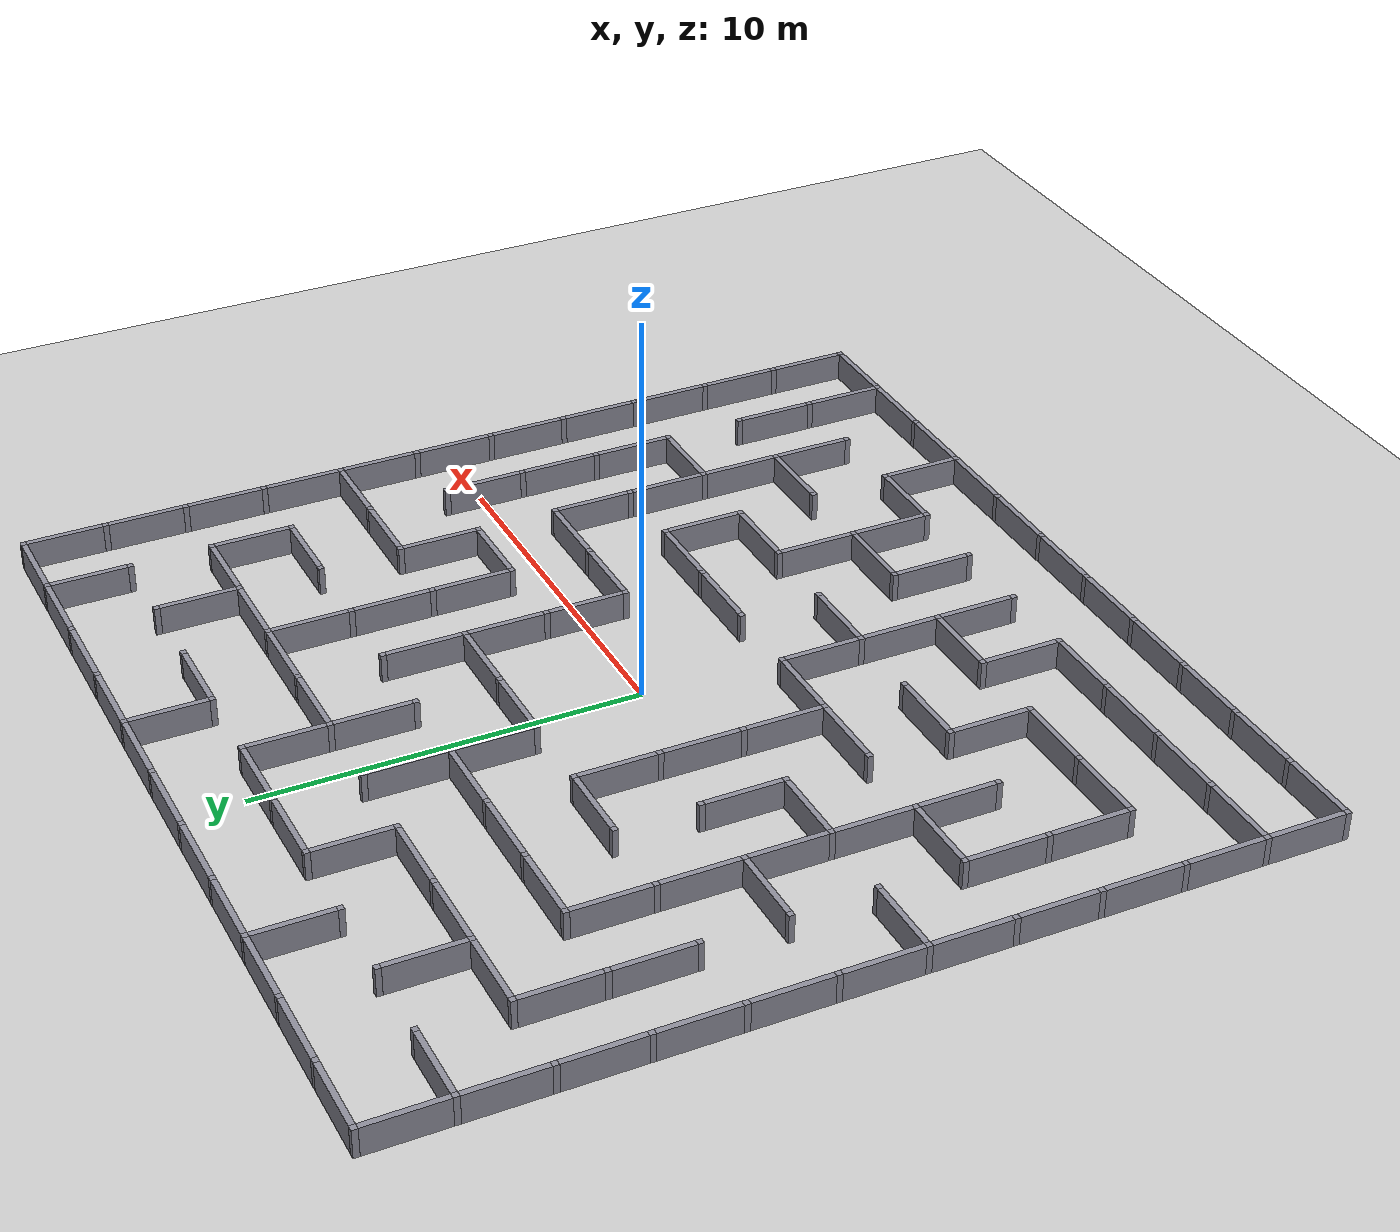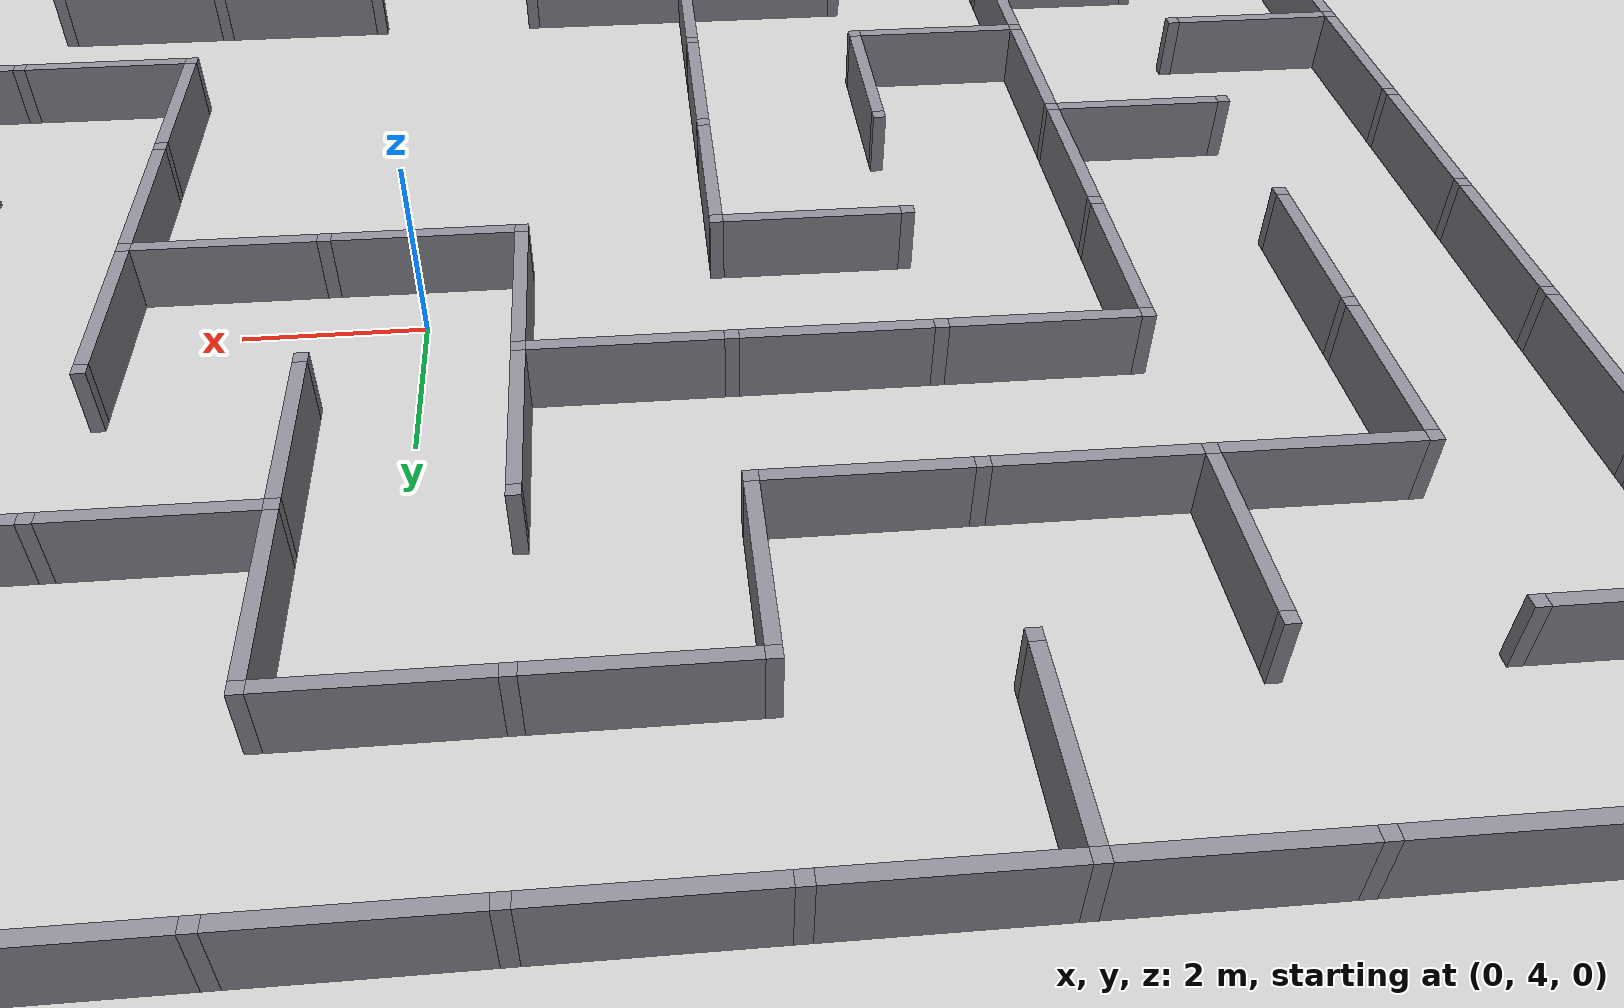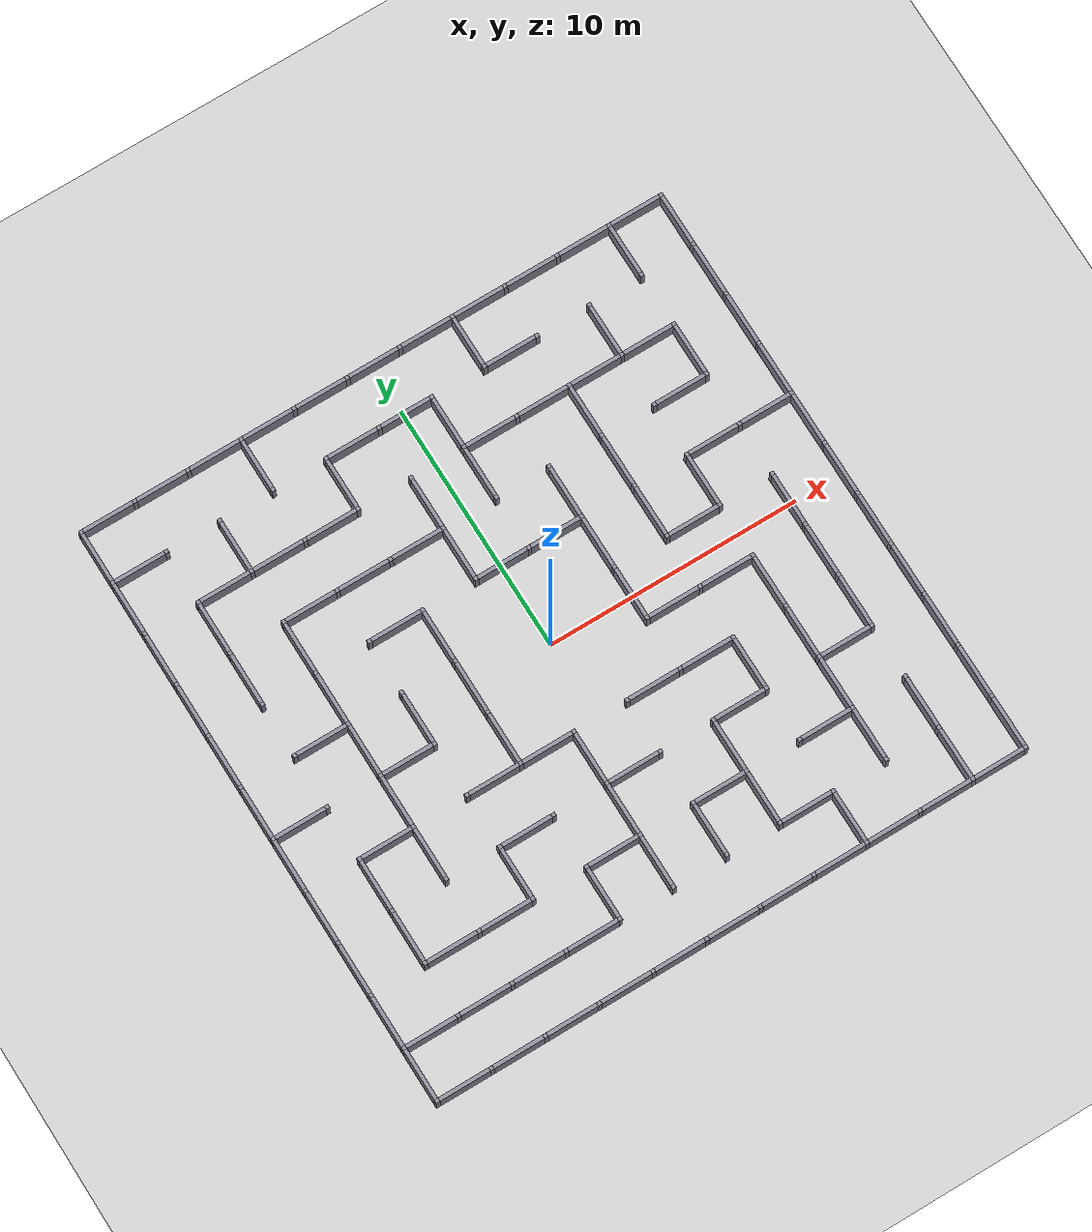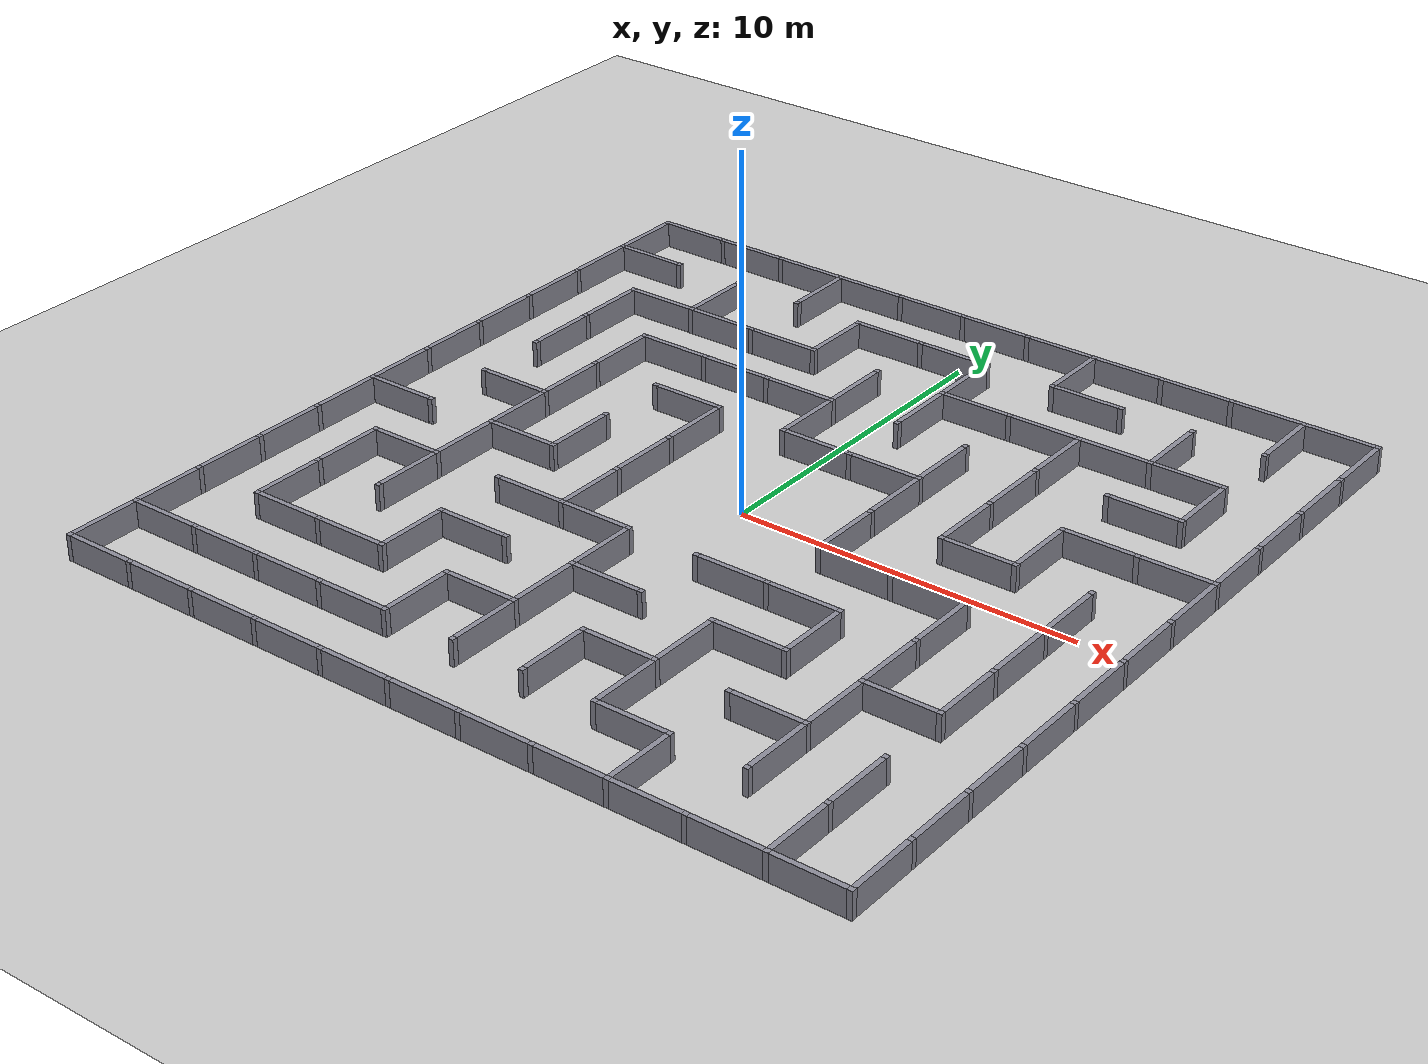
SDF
<?xml version="1.0" ?>
<sdf version="1.9">
  <world name="default">

    <plugin filename="gz-sim-physics-system" name="gz::sim::systems::Physics">
    </plugin>
    <plugin filename="gz-sim-user-commands-system" name="gz::sim::systems::UserCommands">
    </plugin>
    <plugin filename="gz-sim-scene-broadcaster-system" name="gz::sim::systems::SceneBroadcaster">
    </plugin>
    <plugin filename="gz-sim-sensors-system" name="gz::sim::systems::Sensors">
      <render_engine>ogre2</render_engine>
    </plugin>
    <plugin filename="gz-sim-imu-system" name="gz::sim::systems::Imu">
    </plugin>

    <light type="directional" name="sun">
      <cast_shadows>true</cast_shadows>
      <pose>0 0 10 0 0 0</pose>
      <diffuse>0.8 0.8 0.8 1</diffuse>
      <specular>0.2 0.2 0.2 1</specular>
      <attenuation>
        <range>1000</range>
        <constant>0.9</constant>
        <linear>0.01</linear>
        <quadratic>0.001</quadratic>
      </attenuation>
      <direction>-0.5 0.1 -0.9</direction>
    </light>

    <model name="ground_plane">
      <static>true</static>
      <link name="link">
        <collision name="collision">
          <geometry>
            <plane>
              <normal>0 0 1</normal>
            </plane>
          </geometry>
        </collision>
        <visual name="visual">
          <geometry>
            <plane>
              <normal>0 0 1</normal>
              <size>25.80 25.80</size>
            </plane>
          </geometry>
          <material>
            <ambient>0.8 0.8 0.8 1</ambient>
            <diffuse>0.8 0.8 0.8 1</diffuse>
            <specular>0.8 0.8 0.8 1</specular>
          </material>
        </visual>
      </link>
    </model>

    <!-- Maze walls - closed 11x11 grid, generated with a randomized   -->
    <!-- recursive-backtracker (a "perfect" maze: every cell reachable, -->
    <!-- no loops), plus a 3x3 open room at the exact center for the   -->
    <!-- robot to spawn in. Path width 2.0m, wall thickness 0.15m, wall  -->
    <!-- height 0.75m. Footprint is 23.80 x 23.80m (11 cells x 2.15m -->
    <!-- pitch is the closest fit to the requested 25 x 25m with an    -->
    <!-- odd cell count, so there's a true center cell). The whole     -->
    <!-- maze - and the spawn room - is centered on the world origin,  -->
    <!-- matching ros_gz_sim's default spawn pose. All geometry is     -->
    <!-- static (single link, 374 box segments): regenerate with        -->
    <!-- gen_world.py (seed=7) if the layout ever needs to change.     -->
    <model name="maze">
      <static>true</static>
      <link name="walls">
        <collision name="wall_0_collision">
          <pose>-11.8250 -11.8250 0.3750 0 0 0</pose>
          <geometry>
            <box>
              <size>0.1500 0.1500 0.75</size>
            </box>
          </geometry>
        </collision>
        <collision name="wall_1_collision">
          <pose>-9.6750 -11.8250 0.3750 0 0 0</pose>
          <geometry>
            <box>
              <size>0.1500 0.1500 0.75</size>
            </box>
          </geometry>
        </collision>
        <collision name="wall_2_collision">
          <pose>-7.5250 -11.8250 0.3750 0 0 0</pose>
          <geometry>
            <box>
              <size>0.1500 0.1500 0.75</size>
            </box>
          </geometry>
        </collision>
        <collision name="wall_3_collision">
          <pose>-5.3750 -11.8250 0.3750 0 0 0</pose>
          <geometry>
            <box>
              <size>0.1500 0.1500 0.75</size>
            </box>
          </geometry>
        </collision>
        <collision name="wall_4_collision">
          <pose>-3.2250 -11.8250 0.3750 0 0 0</pose>
          <geometry>
            <box>
              <size>0.1500 0.1500 0.75</size>
            </box>
          </geometry>
        </collision>
        <collision name="wall_5_collision">
          <pose>-1.0750 -11.8250 0.3750 0 0 0</pose>
          <geometry>
            <box>
              <size>0.1500 0.1500 0.75</size>
            </box>
          </geometry>
        </collision>
        <collision name="wall_6_collision">
          <pose>1.0750 -11.8250 0.3750 0 0 0</pose>
          <geometry>
            <box>
              <size>0.1500 0.1500 0.75</size>
            </box>
          </geometry>
        </collision>
        <collision name="wall_7_collision">
          <pose>3.2250 -11.8250 0.3750 0 0 0</pose>
          <geometry>
            <box>
              <size>0.1500 0.1500 0.75</size>
            </box>
          </geometry>
        </collision>
        <collision name="wall_8_collision">
          <pose>5.3750 -11.8250 0.3750 0 0 0</pose>
          <geometry>
            <box>
              <size>0.1500 0.1500 0.75</size>
            </box>
          </geometry>
        </collision>
        <collision name="wall_9_collision">
          <pose>7.5250 -11.8250 0.3750 0 0 0</pose>
          <geometry>
            <box>
              <size>0.1500 0.1500 0.75</size>
            </box>
          </geometry>
        </collision>
        <collision name="wall_10_collision">
          <pose>9.6750 -11.8250 0.3750 0 0 0</pose>
          <geometry>
            <box>
              <size>0.1500 0.1500 0.75</size>
            </box>
          </geometry>
        </collision>
        <collision name="wall_11_collision">
          <pose>11.8250 -11.8250 0.3750 0 0 0</pose>
          <geometry>
            <box>
              <size>0.1500 0.1500 0.75</size>
            </box>
          </geometry>
        </collision>
        <collision name="wall_12_collision">
          <pose>-11.8250 -9.6750 0.3750 0 0 0</pose>
          <geometry>
            <box>
              <size>0.1500 0.1500 0.75</size>
            </box>
          </geometry>
        </collision>
        <collision name="wall_13_collision">
          <pose>-9.6750 -9.6750 0.3750 0 0 0</pose>
          <geometry>
            <box>
              <size>0.1500 0.1500 0.75</size>
            </box>
          </geometry>
        </collision>
        <collision name="wall_14_collision">
          <pose>-7.5250 -9.6750 0.3750 0 0 0</pose>
          <geometry>
            <box>
              <size>0.1500 0.1500 0.75</size>
            </box>
          </geometry>
        </collision>
        <collision name="wall_15_collision">
          <pose>-5.3750 -9.6750 0.3750 0 0 0</pose>
          <geometry>
            <box>
              <size>0.1500 0.1500 0.75</size>
            </box>
          </geometry>
        </collision>
        <collision name="wall_16_collision">
          <pose>-3.2250 -9.6750 0.3750 0 0 0</pose>
          <geometry>
            <box>
              <size>0.1500 0.1500 0.75</size>
            </box>
          </geometry>
        </collision>
        <collision name="wall_17_collision">
          <pose>-1.0750 -9.6750 0.3750 0 0 0</pose>
          <geometry>
            <box>
              <size>0.1500 0.1500 0.75</size>
            </box>
          </geometry>
        </collision>
        <collision name="wall_18_collision">
          <pose>1.0750 -9.6750 0.3750 0 0 0</pose>
          <geometry>
            <box>
              <size>0.1500 0.1500 0.75</size>
            </box>
          </geometry>
        </collision>
        <collision name="wall_19_collision">
          <pose>3.2250 -9.6750 0.3750 0 0 0</pose>
          <geometry>
            <box>
              <size>0.1500 0.1500 0.75</size>
            </box>
          </geometry>
        </collision>
        <collision name="wall_20_collision">
          <pose>5.3750 -9.6750 0.3750 0 0 0</pose>
          <geometry>
            <box>
              <size>0.1500 0.1500 0.75</size>
            </box>
          </geometry>
        </collision>
        <collision name="wall_21_collision">
          <pose>7.5250 -9.6750 0.3750 0 0 0</pose>
          <geometry>
            <box>
              <size>0.1500 0.1500 0.75</size>
            </box>
          </geometry>
        </collision>
        <collision name="wall_22_collision">
          <pose>9.6750 -9.6750 0.3750 0 0 0</pose>
          <geometry>
            <box>
              <size>0.1500 0.1500 0.75</size>
            </box>
          </geometry>
        </collision>
        <collision name="wall_23_collision">
          <pose>11.8250 -9.6750 0.3750 0 0 0</pose>
          <geometry>
            <box>
              <size>0.1500 0.1500 0.75</size>
            </box>
          </geometry>
        </collision>
        <collision name="wall_24_collision">
          <pose>-11.8250 -7.5250 0.3750 0 0 0</pose>
          <geometry>
            <box>
              <size>0.1500 0.1500 0.75</size>
            </box>
          </geometry>
        </collision>
        <collision name="wall_25_collision">
          <pose>-9.6750 -7.5250 0.3750 0 0 0</pose>
          <geometry>
            <box>
              <size>0.1500 0.1500 0.75</size>
            </box>
          </geometry>
        </collision>
        <collision name="wall_26_collision">
          <pose>-7.5250 -7.5250 0.3750 0 0 0</pose>
          <geometry>
            <box>
              <size>0.1500 0.1500 0.75</size>
            </box>
          </geometry>
        </collision>
        <collision name="wall_27_collision">
          <pose>-5.3750 -7.5250 0.3750 0 0 0</pose>
          <geometry>
            <box>
              <size>0.1500 0.1500 0.75</size>
            </box>
          </geometry>
        </collision>
        <collision name="wall_28_collision">
          <pose>-3.2250 -7.5250 0.3750 0 0 0</pose>
          <geometry>
            <box>
              <size>0.1500 0.1500 0.75</size>
            </box>
          </geometry>
        </collision>
        <collision name="wall_29_collision">
          <pose>-1.0750 -7.5250 0.3750 0 0 0</pose>
          <geometry>
            <box>
              <size>0.1500 0.1500 0.75</size>
            </box>
          </geometry>
        </collision>
        <collision name="wall_30_collision">
          <pose>1.0750 -7.5250 0.3750 0 0 0</pose>
          <geometry>
            <box>
              <size>0.1500 0.1500 0.75</size>
            </box>
          </geometry>
        </collision>
        <collision name="wall_31_collision">
          <pose>3.2250 -7.5250 0.3750 0 0 0</pose>
          <geometry>
            <box>
              <size>0.1500 0.1500 0.75</size>
            </box>
          </geometry>
        </collision>
        <collision name="wall_32_collision">
          <pose>5.3750 -7.5250 0.3750 0 0 0</pose>
          <geometry>
            <box>
              <size>0.1500 0.1500 0.75</size>
            </box>
          </geometry>
        </collision>
        <collision name="wall_33_collision">
          <pose>7.5250 -7.5250 0.3750 0 0 0</pose>
          <geometry>
            <box>
              <size>0.1500 0.1500 0.75</size>
            </box>
          </geometry>
        </collision>
        <collision name="wall_34_collision">
          <pose>9.6750 -7.5250 0.3750 0 0 0</pose>
          <geometry>
            <box>
              <size>0.1500 0.1500 0.75</size>
            </box>
          </geometry>
        </collision>
        <collision name="wall_35_collision">
          <pose>11.8250 -7.5250 0.3750 0 0 0</pose>
          <geometry>
            <box>
              <size>0.1500 0.1500 0.75</size>
            </box>
          </geometry>
        </collision>
        <collision name="wall_36_collision">
          <pose>-11.8250 -5.3750 0.3750 0 0 0</pose>
          <geometry>
            <box>
              <size>0.1500 0.1500 0.75</size>
            </box>
          </geometry>
        </collision>
        <collision name="wall_37_collision">
          <pose>-9.6750 -5.3750 0.3750 0 0 0</pose>
          <geometry>
            <box>
              <size>0.1500 0.1500 0.75</size>
            </box>
          </geometry>
        </collision>
        <collision name="wall_38_collision">
          <pose>-7.5250 -5.3750 0.3750 0 0 0</pose>
          <geometry>
            <box>
              <size>0.1500 0.1500 0.75</size>
            </box>
          </geometry>
        </collision>
        <collision name="wall_39_collision">
          <pose>-5.3750 -5.3750 0.3750 0 0 0</pose>
          <geometry>
            <box>
              <size>0.1500 0.1500 0.75</size>
            </box>
          </geometry>
        </collision>
        <collision name="wall_40_collision">
          <pose>-3.2250 -5.3750 0.3750 0 0 0</pose>
          <geometry>
            <box>
              <size>0.1500 0.1500 0.75</size>
            </box>
          </geometry>
        </collision>
        <collision name="wall_41_collision">
          <pose>-1.0750 -5.3750 0.3750 0 0 0</pose>
          <geometry>
            <box>
              <size>0.1500 0.1500 0.75</size>
            </box>
          </geometry>
        </collision>
        <collision name="wall_42_collision">
          <pose>1.0750 -5.3750 0.3750 0 0 0</pose>
          <geometry>
            <box>
              <size>0.1500 0.1500 0.75</size>
            </box>
          </geometry>
        </collision>
        <collision name="wall_43_collision">
          <pose>3.2250 -5.3750 0.3750 0 0 0</pose>
          <geometry>
            <box>
              <size>0.1500 0.1500 0.75</size>
            </box>
          </geometry>
        </collision>
        <collision name="wall_44_collision">
          <pose>5.3750 -5.3750 0.3750 0 0 0</pose>
          <geometry>
            <box>
              <size>0.1500 0.1500 0.75</size>
            </box>
          </geometry>
        </collision>
        <collision name="wall_45_collision">
          <pose>7.5250 -5.3750 0.3750 0 0 0</pose>
          <geometry>
            <box>
              <size>0.1500 0.1500 0.75</size>
            </box>
          </geometry>
        </collision>
        <collision name="wall_46_collision">
          <pose>9.6750 -5.3750 0.3750 0 0 0</pose>
          <geometry>
            <box>
              <size>0.1500 0.1500 0.75</size>
            </box>
          </geometry>
        </collision>
        <collision name="wall_47_collision">
          <pose>11.8250 -5.3750 0.3750 0 0 0</pose>
          <geometry>
            <box>
              <size>0.1500 0.1500 0.75</size>
            </box>
          </geometry>
        </collision>
        <collision name="wall_48_collision">
          <pose>-11.8250 -3.2250 0.3750 0 0 0</pose>
          <geometry>
            <box>
              <size>0.1500 0.1500 0.75</size>
            </box>
          </geometry>
        </collision>
        <collision name="wall_49_collision">
          <pose>-9.6750 -3.2250 0.3750 0 0 0</pose>
          <geometry>
            <box>
              <size>0.1500 0.1500 0.75</size>
            </box>
          </geometry>
        </collision>
        <collision name="wall_50_collision">
          <pose>-7.5250 -3.2250 0.3750 0 0 0</pose>
          <geometry>
            <box>
              <size>0.1500 0.1500 0.75</size>
            </box>
          </geometry>
        </collision>
        <collision name="wall_51_collision">
          <pose>-5.3750 -3.2250 0.3750 0 0 0</pose>
          <geometry>
            <box>
              <size>0.1500 0.1500 0.75</size>
            </box>
          </geometry>
        </collision>
        <collision name="wall_52_collision">
          <pose>-3.2250 -3.2250 0.3750 0 0 0</pose>
          <geometry>
            <box>
              <size>0.1500 0.1500 0.75</size>
            </box>
          </geometry>
        </collision>
        <collision name="wall_53_collision">
          <pose>-1.0750 -3.2250 0.3750 0 0 0</pose>
          <geometry>
            <box>
              <size>0.1500 0.1500 0.75</size>
            </box>
          </geometry>
        </collision>
        <collision name="wall_54_collision">
          <pose>1.0750 -3.2250 0.3750 0 0 0</pose>
          <geometry>
            <box>
              <size>0.1500 0.1500 0.75</size>
            </box>
          </geometry>
        </collision>
        <collision name="wall_55_collision">
          <pose>3.2250 -3.2250 0.3750 0 0 0</pose>
          <geometry>
            <box>
              <size>0.1500 0.1500 0.75</size>
            </box>
          </geometry>
        </collision>
        <collision name="wall_56_collision">
          <pose>5.3750 -3.2250 0.3750 0 0 0</pose>
          <geometry>
            <box>
              <size>0.1500 0.1500 0.75</size>
            </box>
          </geometry>
        </collision>
        <collision name="wall_57_collision">
          <pose>7.5250 -3.2250 0.3750 0 0 0</pose>
          <geometry>
            <box>
              <size>0.1500 0.1500 0.75</size>
            </box>
          </geometry>
        </collision>
        <collision name="wall_58_collision">
          <pose>9.6750 -3.2250 0.3750 0 0 0</pose>
          <geometry>
            <box>
              <size>0.1500 0.1500 0.75</size>
            </box>
          </geometry>
        </collision>
        <collision name="wall_59_collision">
          <pose>11.8250 -3.2250 0.3750 0 0 0</pose>
          <geometry>
            <box>
              <size>0.1500 0.1500 0.75</size>
            </box>
          </geometry>
        </collision>
        <collision name="wall_60_collision">
          <pose>-11.8250 -1.0750 0.3750 0 0 0</pose>
          <geometry>
            <box>
              <size>0.1500 0.1500 0.75</size>
            </box>
          </geometry>
        </collision>
        <collision name="wall_61_collision">
          <pose>-9.6750 -1.0750 0.3750 0 0 0</pose>
          <geometry>
            <box>
              <size>0.1500 0.1500 0.75</size>
            </box>
          </geometry>
        </collision>
        <collision name="wall_62_collision">
          <pose>-7.5250 -1.0750 0.3750 0 0 0</pose>
          <geometry>
            <box>
              <size>0.1500 0.1500 0.75</size>
            </box>
          </geometry>
        </collision>
        <collision name="wall_63_collision">
          <pose>-5.3750 -1.0750 0.3750 0 0 0</pose>
          <geometry>
            <box>
              <size>0.1500 0.1500 0.75</size>
            </box>
          </geometry>
        </collision>
        <collision name="wall_64_collision">
          <pose>-3.2250 -1.0750 0.3750 0 0 0</pose>
          <geometry>
            <box>
              <size>0.1500 0.1500 0.75</size>
            </box>
          </geometry>
        </collision>
        <collision name="wall_65_collision">
          <pose>3.2250 -1.0750 0.3750 0 0 0</pose>
          <geometry>
            <box>
              <size>0.1500 0.1500 0.75</size>
            </box>
          </geometry>
        </collision>
        <collision name="wall_66_collision">
          <pose>5.3750 -1.0750 0.3750 0 0 0</pose>
          <geometry>
            <box>
              <size>0.1500 0.1500 0.75</size>
            </box>
          </geometry>
        </collision>
        <collision name="wall_67_collision">
          <pose>7.5250 -1.0750 0.3750 0 0 0</pose>
          <geometry>
            <box>
              <size>0.1500 0.1500 0.75</size>
            </box>
          </geometry>
        </collision>
        <collision name="wall_68_collision">
          <pose>9.6750 -1.0750 0.3750 0 0 0</pose>
          <geometry>
            <box>
              <size>0.1500 0.1500 0.75</size>
            </box>
          </geometry>
        </collision>
        <collision name="wall_69_collision">
          <pose>11.8250 -1.0750 0.3750 0 0 0</pose>
          <geometry>
            <box>
              <size>0.1500 0.1500 0.75</size>
            </box>
          </geometry>
        </collision>
        <collision name="wall_70_collision">
          <pose>-11.8250 1.0750 0.3750 0 0 0</pose>
          <geometry>
            <box>
              <size>0.1500 0.1500 0.75</size>
            </box>
          </geometry>
        </collision>
        <collision name="wall_71_collision">
          <pose>-9.6750 1.0750 0.3750 0 0 0</pose>
          <geometry>
            <box>
              <size>0.1500 0.1500 0.75</size>
            </box>
          </geometry>
        </collision>
        <collision name="wall_72_collision">
          <pose>-7.5250 1.0750 0.3750 0 0 0</pose>
          <geometry>
            <box>
              <size>0.1500 0.1500 0.75</size>
            </box>
          </geometry>
        </collision>
        <collision name="wall_73_collision">
          <pose>-5.3750 1.0750 0.3750 0 0 0</pose>
          <geometry>
            <box>
              <size>0.1500 0.1500 0.75</size>
            </box>
          </geometry>
        </collision>
        <collision name="wall_74_collision">
          <pose>-3.2250 1.0750 0.3750 0 0 0</pose>
          <geometry>
            <box>
              <size>0.1500 0.1500 0.75</size>
            </box>
          </geometry>
        </collision>
        <collision name="wall_75_collision">
          <pose>3.2250 1.0750 0.3750 0 0 0</pose>
          <geometry>
            <box>
              <size>0.1500 0.1500 0.75</size>
            </box>
          </geometry>
        </collision>
        <collision name="wall_76_collision">
          <pose>5.3750 1.0750 0.3750 0 0 0</pose>
          <geometry>
            <box>
              <size>0.1500 0.1500 0.75</size>
            </box>
          </geometry>
        </collision>
        <collision name="wall_77_collision">
          <pose>7.5250 1.0750 0.3750 0 0 0</pose>
          <geometry>
            <box>
              <size>0.1500 0.1500 0.75</size>
            </box>
          </geometry>
        </collision>
        <collision name="wall_78_collision">
          <pose>9.6750 1.0750 0.3750 0 0 0</pose>
          <geometry>
            <box>
              <size>0.1500 0.1500 0.75</size>
            </box>
          </geometry>
        </collision>
        <collision name="wall_79_collision">
          <pose>11.8250 1.0750 0.3750 0 0 0</pose>
          <geometry>
            <box>
              <size>0.1500 0.1500 0.75</size>
            </box>
          </geometry>
        </collision>
        <collision name="wall_80_collision">
          <pose>-11.8250 3.2250 0.3750 0 0 0</pose>
          <geometry>
            <box>
              <size>0.1500 0.1500 0.75</size>
            </box>
          </geometry>
        </collision>
        <collision name="wall_81_collision">
          <pose>-9.6750 3.2250 0.3750 0 0 0</pose>
          <geometry>
            <box>
              <size>0.1500 0.1500 0.75</size>
            </box>
          </geometry>
        </collision>
        <collision name="wall_82_collision">
          <pose>-7.5250 3.2250 0.3750 0 0 0</pose>
          <geometry>
            <box>
              <size>0.1500 0.1500 0.75</size>
            </box>
          </geometry>
        </collision>
        <collision name="wall_83_collision">
          <pose>-5.3750 3.2250 0.3750 0 0 0</pose>
          <geometry>
            <box>
              <size>0.1500 0.1500 0.75</size>
            </box>
          </geometry>
        </collision>
        <collision name="wall_84_collision">
          <pose>-3.2250 3.2250 0.3750 0 0 0</pose>
          <geometry>
            <box>
              <size>0.1500 0.1500 0.75</size>
            </box>
          </geometry>
        </collision>
        <collision name="wall_85_collision">
          <pose>-1.0750 3.2250 0.3750 0 0 0</pose>
          <geometry>
            <box>
              <size>0.1500 0.1500 0.75</size>
            </box>
          </geometry>
        </collision>
        <collision name="wall_86_collision">
          <pose>1.0750 3.2250 0.3750 0 0 0</pose>
          <geometry>
            <box>
              <size>0.1500 0.1500 0.75</size>
            </box>
          </geometry>
        </collision>
        <collision name="wall_87_collision">
          <pose>3.2250 3.2250 0.3750 0 0 0</pose>
          <geometry>
            <box>
              <size>0.1500 0.1500 0.75</size>
            </box>
          </geometry>
        </collision>
        <collision name="wall_88_collision">
          <pose>5.3750 3.2250 0.3750 0 0 0</pose>
          <geometry>
            <box>
              <size>0.1500 0.1500 0.75</size>
            </box>
          </geometry>
        </collision>
        <collision name="wall_89_collision">
          <pose>7.5250 3.2250 0.3750 0 0 0</pose>
          <geometry>
            <box>
              <size>0.1500 0.1500 0.75</size>
            </box>
          </geometry>
        </collision>
        <collision name="wall_90_collision">
          <pose>9.6750 3.2250 0.3750 0 0 0</pose>
          <geometry>
            <box>
              <size>0.1500 0.1500 0.75</size>
            </box>
          </geometry>
        </collision>
        <collision name="wall_91_collision">
          <pose>11.8250 3.2250 0.3750 0 0 0</pose>
          <geometry>
            <box>
              <size>0.1500 0.1500 0.75</size>
            </box>
          </geometry>
        </collision>
        <collision name="wall_92_collision">
          <pose>-11.8250 5.3750 0.3750 0 0 0</pose>
          <geometry>
            <box>
              <size>0.1500 0.1500 0.75</size>
            </box>
          </geometry>
        </collision>
        <collision name="wall_93_collision">
          <pose>-9.6750 5.3750 0.3750 0 0 0</pose>
          <geometry>
            <box>
              <size>0.1500 0.1500 0.75</size>
            </box>
          </geometry>
        </collision>
        <collision name="wall_94_collision">
          <pose>-7.5250 5.3750 0.3750 0 0 0</pose>
          <geometry>
            <box>
              <size>0.1500 0.1500 0.75</size>
            </box>
          </geometry>
        </collision>
        <collision name="wall_95_collision">
          <pose>-5.3750 5.3750 0.3750 0 0 0</pose>
          <geometry>
            <box>
              <size>0.1500 0.1500 0.75</size>
            </box>
          </geometry>
        </collision>
        <collision name="wall_96_collision">
          <pose>-3.2250 5.3750 0.3750 0 0 0</pose>
          <geometry>
            <box>
              <size>0.1500 0.1500 0.75</size>
            </box>
          </geometry>
        </collision>
        <collision name="wall_97_collision">
          <pose>-1.0750 5.3750 0.3750 0 0 0</pose>
          <geometry>
            <box>
              <size>0.1500 0.1500 0.75</size>
            </box>
          </geometry>
        </collision>
        <collision name="wall_98_collision">
          <pose>1.0750 5.3750 0.3750 0 0 0</pose>
          <geometry>
            <box>
              <size>0.1500 0.1500 0.75</size>
            </box>
          </geometry>
        </collision>
        <collision name="wall_99_collision">
          <pose>3.2250 5.3750 0.3750 0 0 0</pose>
          <geometry>
            <box>
              <size>0.1500 0.1500 0.75</size>
            </box>
          </geometry>
        </collision>
        <collision name="wall_100_collision">
          <pose>5.3750 5.3750 0.3750 0 0 0</pose>
          <geometry>
            <box>
              <size>0.1500 0.1500 0.75</size>
            </box>
          </geometry>
        </collision>
        <collision name="wall_101_collision">
          <pose>7.5250 5.3750 0.3750 0 0 0</pose>
          <geometry>
            <box>
              <size>0.1500 0.1500 0.75</size>
            </box>
          </geometry>
        </collision>
        <collision name="wall_102_collision">
          <pose>9.6750 5.3750 0.3750 0 0 0</pose>
          <geometry>
            <box>
              <size>0.1500 0.1500 0.75</size>
            </box>
          </geometry>
        </collision>
        <collision name="wall_103_collision">
          <pose>11.8250 5.3750 0.3750 0 0 0</pose>
          <geometry>
            <box>
              <size>0.1500 0.1500 0.75</size>
            </box>
          </geometry>
        </collision>
        <collision name="wall_104_collision">
          <pose>-11.8250 7.5250 0.3750 0 0 0</pose>
          <geometry>
            <box>
              <size>0.1500 0.1500 0.75</size>
            </box>
          </geometry>
        </collision>
        <collision name="wall_105_collision">
          <pose>-9.6750 7.5250 0.3750 0 0 0</pose>
          <geometry>
            <box>
              <size>0.1500 0.1500 0.75</size>
            </box>
          </geometry>
        </collision>
        <collision name="wall_106_collision">
          <pose>-7.5250 7.5250 0.3750 0 0 0</pose>
          <geometry>
            <box>
              <size>0.1500 0.1500 0.75</size>
            </box>
          </geometry>
        </collision>
        <collision name="wall_107_collision">
          <pose>-5.3750 7.5250 0.3750 0 0 0</pose>
          <geometry>
            <box>
              <size>0.1500 0.1500 0.75</size>
            </box>
          </geometry>
        </collision>
        <collision name="wall_108_collision">
          <pose>-3.2250 7.5250 0.3750 0 0 0</pose>
          <geometry>
            <box>
              <size>0.1500 0.1500 0.75</size>
            </box>
          </geometry>
        </collision>
        <collision name="wall_109_collision">
          <pose>-1.0750 7.5250 0.3750 0 0 0</pose>
          <geometry>
            <box>
              <size>0.1500 0.1500 0.75</size>
            </box>
          </geometry>
        </collision>
        <collision name="wall_110_collision">
          <pose>1.0750 7.5250 0.3750 0 0 0</pose>
          <geometry>
            <box>
              <size>0.1500 0.1500 0.75</size>
            </box>
          </geometry>
        </collision>
        <collision name="wall_111_collision">
          <pose>3.2250 7.5250 0.3750 0 0 0</pose>
          <geometry>
            <box>
              <size>0.1500 0.1500 0.75</size>
            </box>
          </geometry>
        </collision>
        <collision name="wall_112_collision">
          <pose>5.3750 7.5250 0.3750 0 0 0</pose>
          <geometry>
            <box>
              <size>0.1500 0.1500 0.75</size>
            </box>
          </geometry>
        </collision>
        <collision name="wall_113_collision">
          <pose>7.5250 7.5250 0.3750 0 0 0</pose>
          <geometry>
            <box>
              <size>0.1500 0.1500 0.75</size>
            </box>
          </geometry>
        </collision>
        <collision name="wall_114_collision">
          <pose>9.6750 7.5250 0.3750 0 0 0</pose>
          <geometry>
            <box>
              <size>0.1500 0.1500 0.75</size>
            </box>
          </geometry>
        </collision>
        <collision name="wall_115_collision">
          <pose>11.8250 7.5250 0.3750 0 0 0</pose>
          <geometry>
            <box>
              <size>0.1500 0.1500 0.75</size>
            </box>
          </geometry>
        </collision>
        <collision name="wall_116_collision">
          <pose>-11.8250 9.6750 0.3750 0 0 0</pose>
          <geometry>
            <box>
              <size>0.1500 0.1500 0.75</size>
            </box>
          </geometry>
        </collision>
        <collision name="wall_117_collision">
          <pose>-9.6750 9.6750 0.3750 0 0 0</pose>
          <geometry>
            <box>
              <size>0.1500 0.1500 0.75</size>
            </box>
          </geometry>
        </collision>
        <collision name="wall_118_collision">
          <pose>-7.5250 9.6750 0.3750 0 0 0</pose>
          <geometry>
            <box>
              <size>0.1500 0.1500 0.75</size>
            </box>
          </geometry>
        </collision>
        <collision name="wall_119_collision">
          <pose>-5.3750 9.6750 0.3750 0 0 0</pose>
          <geometry>
            <box>
              <size>0.1500 0.1500 0.75</size>
            </box>
          </geometry>
        </collision>
        <collision name="wall_120_collision">
          <pose>-3.2250 9.6750 0.3750 0 0 0</pose>
          <geometry>
            <box>
              <size>0.1500 0.1500 0.75</size>
            </box>
          </geometry>
        </collision>
        <collision name="wall_121_collision">
          <pose>-1.0750 9.6750 0.3750 0 0 0</pose>
          <geometry>
            <box>
              <size>0.1500 0.1500 0.75</size>
            </box>
          </geometry>
        </collision>
        <collision name="wall_122_collision">
          <pose>1.0750 9.6750 0.3750 0 0 0</pose>
          <geometry>
            <box>
              <size>0.1500 0.1500 0.75</size>
            </box>
          </geometry>
        </collision>
        <collision name="wall_123_collision">
          <pose>3.2250 9.6750 0.3750 0 0 0</pose>
          <geometry>
            <box>
              <size>0.1500 0.1500 0.75</size>
            </box>
          </geometry>
        </collision>
        <collision name="wall_124_collision">
          <pose>5.3750 9.6750 0.3750 0 0 0</pose>
          <geometry>
            <box>
              <size>0.1500 0.1500 0.75</size>
            </box>
          </geometry>
        </collision>
        <collision name="wall_125_collision">
          <pose>7.5250 9.6750 0.3750 0 0 0</pose>
          <geometry>
            <box>
              <size>0.1500 0.1500 0.75</size>
            </box>
          </geometry>
        </collision>
        <collision name="wall_126_collision">
          <pose>9.6750 9.6750 0.3750 0 0 0</pose>
          <geometry>
            <box>
              <size>0.1500 0.1500 0.75</size>
            </box>
          </geometry>
        </collision>
        <collision name="wall_127_collision">
          <pose>11.8250 9.6750 0.3750 0 0 0</pose>
          <geometry>
            <box>
              <size>0.1500 0.1500 0.75</size>
            </box>
          </geometry>
        </collision>
        <collision name="wall_128_collision">
          <pose>-11.8250 11.8250 0.3750 0 0 0</pose>
          <geometry>
            <box>
              <size>0.1500 0.1500 0.75</size>
            </box>
          </geometry>
        </collision>
        <collision name="wall_129_collision">
          <pose>-9.6750 11.8250 0.3750 0 0 0</pose>
          <geometry>
            <box>
              <size>0.1500 0.1500 0.75</size>
            </box>
          </geometry>
        </collision>
        <collision name="wall_130_collision">
          <pose>-7.5250 11.8250 0.3750 0 0 0</pose>
          <geometry>
            <box>
              <size>0.1500 0.1500 0.75</size>
            </box>
          </geometry>
        </collision>
        <collision name="wall_131_collision">
          <pose>-5.3750 11.8250 0.3750 0 0 0</pose>
          <geometry>
            <box>
              <size>0.1500 0.1500 0.75</size>
            </box>
          </geometry>
        </collision>
        <collision name="wall_132_collision">
          <pose>-3.2250 11.8250 0.3750 0 0 0</pose>
          <geometry>
            <box>
              <size>0.1500 0.1500 0.75</size>
            </box>
          </geometry>
        </collision>
        <collision name="wall_133_collision">
          <pose>-1.0750 11.8250 0.3750 0 0 0</pose>
          <geometry>
            <box>
              <size>0.1500 0.1500 0.75</size>
            </box>
          </geometry>
        </collision>
        <collision name="wall_134_collision">
          <pose>1.0750 11.8250 0.3750 0 0 0</pose>
          <geometry>
            <box>
              <size>0.1500 0.1500 0.75</size>
            </box>
          </geometry>
        </collision>
        <collision name="wall_135_collision">
          <pose>3.2250 11.8250 0.3750 0 0 0</pose>
          <geometry>
            <box>
              <size>0.1500 0.1500 0.75</size>
            </box>
          </geometry>
        </collision>
        <collision name="wall_136_collision">
          <pose>5.3750 11.8250 0.3750 0 0 0</pose>
          <geometry>
            <box>
              <size>0.1500 0.1500 0.75</size>
            </box>
          </geometry>
        </collision>
        <collision name="wall_137_collision">
          <pose>7.5250 11.8250 0.3750 0 0 0</pose>
          <geometry>
            <box>
              <size>0.1500 0.1500 0.75</size>
            </box>
          </geometry>
        </collision>
        <collision name="wall_138_collision">
          <pose>9.6750 11.8250 0.3750 0 0 0</pose>
          <geometry>
            <box>
              <size>0.1500 0.1500 0.75</size>
            </box>
          </geometry>
        </collision>
        <collision name="wall_139_collision">
          <pose>11.8250 11.8250 0.3750 0 0 0</pose>
          <geometry>
            <box>
              <size>0.1500 0.1500 0.75</size>
            </box>
          </geometry>
        </collision>
        <collision name="wall_140_collision">
          <pose>-10.7500 -11.8250 0.3750 0 0 0</pose>
          <geometry>
            <box>
              <size>2.0000 0.1500 0.75</size>
            </box>
          </geometry>
        </collision>
        <collision name="wall_141_collision">
          <pose>-10.7500 -9.6750 0.3750 0 0 0</pose>
          <geometry>
            <box>
              <size>2.0000 0.1500 0.75</size>
            </box>
          </geometry>
        </collision>
        <collision name="wall_142_collision">
          <pose>-11.8250 -10.7500 0.3750 0 0 0</pose>
          <geometry>
            <box>
              <size>0.1500 2.0000 0.75</size>
            </box>
          </geometry>
        </collision>
        <collision name="wall_143_collision">
          <pose>-8.6000 -11.8250 0.3750 0 0 0</pose>
          <geometry>
            <box>
              <size>2.0000 0.1500 0.75</size>
            </box>
          </geometry>
        </collision>
        <collision name="wall_144_collision">
          <pose>-8.6000 -9.6750 0.3750 0 0 0</pose>
          <geometry>
            <box>
              <size>2.0000 0.1500 0.75</size>
            </box>
          </geometry>
        </collision>
        <collision name="wall_145_collision">
          <pose>-6.4500 -11.8250 0.3750 0 0 0</pose>
          <geometry>
            <box>
              <size>2.0000 0.1500 0.75</size>
            </box>
          </geometry>
        </collision>
        <collision name="wall_146_collision">
          <pose>-6.4500 -9.6750 0.3750 0 0 0</pose>
          <geometry>
            <box>
              <size>2.0000 0.1500 0.75</size>
            </box>
          </geometry>
        </collision>
        <collision name="wall_147_collision">
          <pose>-4.3000 -11.8250 0.3750 0 0 0</pose>
          <geometry>
            <box>
              <size>2.0000 0.1500 0.75</size>
            </box>
          </geometry>
        </collision>
        <collision name="wall_148_collision">
          <pose>-4.3000 -9.6750 0.3750 0 0 0</pose>
          <geometry>
            <box>
              <size>2.0000 0.1500 0.75</size>
            </box>
          </geometry>
        </collision>
        <collision name="wall_149_collision">
          <pose>-2.1500 -11.8250 0.3750 0 0 0</pose>
          <geometry>
            <box>
              <size>2.0000 0.1500 0.75</size>
            </box>
          </geometry>
        </collision>
        <collision name="wall_150_collision">
          <pose>0.0000 -11.8250 0.3750 0 0 0</pose>
          <geometry>
            <box>
              <size>2.0000 0.1500 0.75</size>
            </box>
          </geometry>
        </collision>
        <collision name="wall_151_collision">
          <pose>2.1500 -11.8250 0.3750 0 0 0</pose>
          <geometry>
            <box>
              <size>2.0000 0.1500 0.75</size>
            </box>
          </geometry>
        </collision>
        <collision name="wall_152_collision">
          <pose>4.3000 -11.8250 0.3750 0 0 0</pose>
          <geometry>
            <box>
              <size>2.0000 0.1500 0.75</size>
            </box>
          </geometry>
        </collision>
        <collision name="wall_153_collision">
          <pose>4.3000 -9.6750 0.3750 0 0 0</pose>
          <geometry>
            <box>
              <size>2.0000 0.1500 0.75</size>
            </box>
          </geometry>
        </collision>
        <collision name="wall_154_collision">
          <pose>5.3750 -10.7500 0.3750 0 0 0</pose>
          <geometry>
            <box>
              <size>0.1500 2.0000 0.75</size>
            </box>
          </geometry>
        </collision>
        <collision name="wall_155_collision">
          <pose>6.4500 -11.8250 0.3750 0 0 0</pose>
          <geometry>
            <box>
              <size>2.0000 0.1500 0.75</size>
            </box>
          </geometry>
        </collision>
        <collision name="wall_156_collision">
          <pose>5.3750 -10.7500 0.3750 0 0 0</pose>
          <geometry>
            <box>
              <size>0.1500 2.0000 0.75</size>
            </box>
          </geometry>
        </collision>
        <collision name="wall_157_collision">
          <pose>8.6000 -11.8250 0.3750 0 0 0</pose>
          <geometry>
            <box>
              <size>2.0000 0.1500 0.75</size>
            </box>
          </geometry>
        </collision>
        <collision name="wall_158_collision">
          <pose>9.6750 -10.7500 0.3750 0 0 0</pose>
          <geometry>
            <box>
              <size>0.1500 2.0000 0.75</size>
            </box>
          </geometry>
        </collision>
        <collision name="wall_159_collision">
          <pose>10.7500 -11.8250 0.3750 0 0 0</pose>
          <geometry>
            <box>
              <size>2.0000 0.1500 0.75</size>
            </box>
          </geometry>
        </collision>
        <collision name="wall_160_collision">
          <pose>9.6750 -10.7500 0.3750 0 0 0</pose>
          <geometry>
            <box>
              <size>0.1500 2.0000 0.75</size>
            </box>
          </geometry>
        </collision>
        <collision name="wall_161_collision">
          <pose>11.8250 -10.7500 0.3750 0 0 0</pose>
          <geometry>
            <box>
              <size>0.1500 2.0000 0.75</size>
            </box>
          </geometry>
        </collision>
        <collision name="wall_162_collision">
          <pose>-10.7500 -9.6750 0.3750 0 0 0</pose>
          <geometry>
            <box>
              <size>2.0000 0.1500 0.75</size>
            </box>
          </geometry>
        </collision>
        <collision name="wall_163_collision">
          <pose>-11.8250 -8.6000 0.3750 0 0 0</pose>
          <geometry>
            <box>
              <size>0.1500 2.0000 0.75</size>
            </box>
          </geometry>
        </collision>
        <collision name="wall_164_collision">
          <pose>-8.6000 -9.6750 0.3750 0 0 0</pose>
          <geometry>
            <box>
              <size>2.0000 0.1500 0.75</size>
            </box>
          </geometry>
        </collision>
        <collision name="wall_165_collision">
          <pose>-8.6000 -7.5250 0.3750 0 0 0</pose>
          <geometry>
            <box>
              <size>2.0000 0.1500 0.75</size>
            </box>
          </geometry>
        </collision>
        <collision name="wall_166_collision">
          <pose>-6.4500 -9.6750 0.3750 0 0 0</pose>
          <geometry>
            <box>
              <size>2.0000 0.1500 0.75</size>
            </box>
          </geometry>
        </collision>
        <collision name="wall_167_collision">
          <pose>-6.4500 -7.5250 0.3750 0 0 0</pose>
          <geometry>
            <box>
              <size>2.0000 0.1500 0.75</size>
            </box>
          </geometry>
        </collision>
        <collision name="wall_168_collision">
          <pose>-4.3000 -9.6750 0.3750 0 0 0</pose>
          <geometry>
            <box>
              <size>2.0000 0.1500 0.75</size>
            </box>
          </geometry>
        </collision>
        <collision name="wall_169_collision">
          <pose>-3.2250 -8.6000 0.3750 0 0 0</pose>
          <geometry>
            <box>
              <size>0.1500 2.0000 0.75</size>
            </box>
          </geometry>
        </collision>
        <collision name="wall_170_collision">
          <pose>-2.1500 -7.5250 0.3750 0 0 0</pose>
          <geometry>
            <box>
              <size>2.0000 0.1500 0.75</size>
            </box>
          </geometry>
        </collision>
        <collision name="wall_171_collision">
          <pose>-3.2250 -8.6000 0.3750 0 0 0</pose>
          <geometry>
            <box>
              <size>0.1500 2.0000 0.75</size>
            </box>
          </geometry>
        </collision>
        <collision name="wall_172_collision">
          <pose>-1.0750 -8.6000 0.3750 0 0 0</pose>
          <geometry>
            <box>
              <size>0.1500 2.0000 0.75</size>
            </box>
          </geometry>
        </collision>
        <collision name="wall_173_collision">
          <pose>-1.0750 -8.6000 0.3750 0 0 0</pose>
          <geometry>
            <box>
              <size>0.1500 2.0000 0.75</size>
            </box>
          </geometry>
        </collision>
        <collision name="wall_174_collision">
          <pose>1.0750 -8.6000 0.3750 0 0 0</pose>
          <geometry>
            <box>
              <size>0.1500 2.0000 0.75</size>
            </box>
          </geometry>
        </collision>
        <collision name="wall_175_collision">
          <pose>2.1500 -7.5250 0.3750 0 0 0</pose>
          <geometry>
            <box>
              <size>2.0000 0.1500 0.75</size>
            </box>
          </geometry>
        </collision>
        <collision name="wall_176_collision">
          <pose>1.0750 -8.6000 0.3750 0 0 0</pose>
          <geometry>
            <box>
              <size>0.1500 2.0000 0.75</size>
            </box>
          </geometry>
        </collision>
        <collision name="wall_177_collision">
          <pose>3.2250 -8.6000 0.3750 0 0 0</pose>
          <geometry>
            <box>
              <size>0.1500 2.0000 0.75</size>
            </box>
          </geometry>
        </collision>
        <collision name="wall_178_collision">
          <pose>4.3000 -9.6750 0.3750 0 0 0</pose>
          <geometry>
            <box>
              <size>2.0000 0.1500 0.75</size>
            </box>
          </geometry>
        </collision>
        <collision name="wall_179_collision">
          <pose>3.2250 -8.6000 0.3750 0 0 0</pose>
          <geometry>
            <box>
              <size>0.1500 2.0000 0.75</size>
            </box>
          </geometry>
        </collision>
        <collision name="wall_180_collision">
          <pose>6.4500 -7.5250 0.3750 0 0 0</pose>
          <geometry>
            <box>
              <size>2.0000 0.1500 0.75</size>
            </box>
          </geometry>
        </collision>
        <collision name="wall_181_collision">
          <pose>7.5250 -8.6000 0.3750 0 0 0</pose>
          <geometry>
            <box>
              <size>0.1500 2.0000 0.75</size>
            </box>
          </geometry>
        </collision>
        <collision name="wall_182_collision">
          <pose>7.5250 -8.6000 0.3750 0 0 0</pose>
          <geometry>
            <box>
              <size>0.1500 2.0000 0.75</size>
            </box>
          </geometry>
        </collision>
        <collision name="wall_183_collision">
          <pose>9.6750 -8.6000 0.3750 0 0 0</pose>
          <geometry>
            <box>
              <size>0.1500 2.0000 0.75</size>
            </box>
          </geometry>
        </collision>
        <collision name="wall_184_collision">
          <pose>9.6750 -8.6000 0.3750 0 0 0</pose>
          <geometry>
            <box>
              <size>0.1500 2.0000 0.75</size>
            </box>
          </geometry>
        </collision>
        <collision name="wall_185_collision">
          <pose>11.8250 -8.6000 0.3750 0 0 0</pose>
          <geometry>
            <box>
              <size>0.1500 2.0000 0.75</size>
            </box>
          </geometry>
        </collision>
        <collision name="wall_186_collision">
          <pose>-11.8250 -6.4500 0.3750 0 0 0</pose>
          <geometry>
            <box>
              <size>0.1500 2.0000 0.75</size>
            </box>
          </geometry>
        </collision>
        <collision name="wall_187_collision">
          <pose>-9.6750 -6.4500 0.3750 0 0 0</pose>
          <geometry>
            <box>
              <size>0.1500 2.0000 0.75</size>
            </box>
          </geometry>
        </collision>
        <collision name="wall_188_collision">
          <pose>-8.6000 -7.5250 0.3750 0 0 0</pose>
          <geometry>
            <box>
              <size>2.0000 0.1500 0.75</size>
            </box>
          </geometry>
        </collision>
        <collision name="wall_189_collision">
          <pose>-9.6750 -6.4500 0.3750 0 0 0</pose>
          <geometry>
            <box>
              <size>0.1500 2.0000 0.75</size>
            </box>
          </geometry>
        </collision>
        <collision name="wall_190_collision">
          <pose>-6.4500 -7.5250 0.3750 0 0 0</pose>
          <geometry>
            <box>
              <size>2.0000 0.1500 0.75</size>
            </box>
          </geometry>
        </collision>
        <collision name="wall_191_collision">
          <pose>-5.3750 -6.4500 0.3750 0 0 0</pose>
          <geometry>
            <box>
              <size>0.1500 2.0000 0.75</size>
            </box>
          </geometry>
        </collision>
        <collision name="wall_192_collision">
          <pose>-4.3000 -5.3750 0.3750 0 0 0</pose>
          <geometry>
            <box>
              <size>2.0000 0.1500 0.75</size>
            </box>
          </geometry>
        </collision>
        <collision name="wall_193_collision">
          <pose>-5.3750 -6.4500 0.3750 0 0 0</pose>
          <geometry>
            <box>
              <size>0.1500 2.0000 0.75</size>
            </box>
          </geometry>
        </collision>
        <collision name="wall_194_collision">
          <pose>-2.1500 -7.5250 0.3750 0 0 0</pose>
          <geometry>
            <box>
              <size>2.0000 0.1500 0.75</size>
            </box>
          </geometry>
        </collision>
        <collision name="wall_195_collision">
          <pose>-1.0750 -6.4500 0.3750 0 0 0</pose>
          <geometry>
            <box>
              <size>0.1500 2.0000 0.75</size>
            </box>
          </geometry>
        </collision>
        <collision name="wall_196_collision">
          <pose>0.0000 -5.3750 0.3750 0 0 0</pose>
          <geometry>
            <box>
              <size>2.0000 0.1500 0.75</size>
            </box>
          </geometry>
        </collision>
        <collision name="wall_197_collision">
          <pose>-1.0750 -6.4500 0.3750 0 0 0</pose>
          <geometry>
            <box>
              <size>0.1500 2.0000 0.75</size>
            </box>
          </geometry>
        </collision>
        <collision name="wall_198_collision">
          <pose>2.1500 -7.5250 0.3750 0 0 0</pose>
          <geometry>
            <box>
              <size>2.0000 0.1500 0.75</size>
            </box>
          </geometry>
        </collision>
        <collision name="wall_199_collision">
          <pose>3.2250 -6.4500 0.3750 0 0 0</pose>
          <geometry>
            <box>
              <size>0.1500 2.0000 0.75</size>
            </box>
          </geometry>
        </collision>
        <collision name="wall_200_collision">
          <pose>4.3000 -5.3750 0.3750 0 0 0</pose>
          <geometry>
            <box>
              <size>2.0000 0.1500 0.75</size>
            </box>
          </geometry>
        </collision>
        <collision name="wall_201_collision">
          <pose>3.2250 -6.4500 0.3750 0 0 0</pose>
          <geometry>
            <box>
              <size>0.1500 2.0000 0.75</size>
            </box>
          </geometry>
        </collision>
        <collision name="wall_202_collision">
          <pose>6.4500 -7.5250 0.3750 0 0 0</pose>
          <geometry>
            <box>
              <size>2.0000 0.1500 0.75</size>
            </box>
          </geometry>
        </collision>
        <collision name="wall_203_collision">
          <pose>7.5250 -6.4500 0.3750 0 0 0</pose>
          <geometry>
            <box>
              <size>0.1500 2.0000 0.75</size>
            </box>
          </geometry>
        </collision>
        <collision name="wall_204_collision">
          <pose>8.6000 -5.3750 0.3750 0 0 0</pose>
          <geometry>
            <box>
              <size>2.0000 0.1500 0.75</size>
            </box>
          </geometry>
        </collision>
        <collision name="wall_205_collision">
          <pose>7.5250 -6.4500 0.3750 0 0 0</pose>
          <geometry>
            <box>
              <size>0.1500 2.0000 0.75</size>
            </box>
          </geometry>
        </collision>
        <collision name="wall_206_collision">
          <pose>11.8250 -6.4500 0.3750 0 0 0</pose>
          <geometry>
            <box>
              <size>0.1500 2.0000 0.75</size>
            </box>
          </geometry>
        </collision>
        <collision name="wall_207_collision">
          <pose>-11.8250 -4.3000 0.3750 0 0 0</pose>
          <geometry>
            <box>
              <size>0.1500 2.0000 0.75</size>
            </box>
          </geometry>
        </collision>
        <collision name="wall_208_collision">
          <pose>-9.6750 -4.3000 0.3750 0 0 0</pose>
          <geometry>
            <box>
              <size>0.1500 2.0000 0.75</size>
            </box>
          </geometry>
        </collision>
        <collision name="wall_209_collision">
          <pose>-8.6000 -3.2250 0.3750 0 0 0</pose>
          <geometry>
            <box>
              <size>2.0000 0.1500 0.75</size>
            </box>
          </geometry>
        </collision>
        <collision name="wall_210_collision">
          <pose>-9.6750 -4.3000 0.3750 0 0 0</pose>
          <geometry>
            <box>
              <size>0.1500 2.0000 0.75</size>
            </box>
          </geometry>
        </collision>
        <collision name="wall_211_collision">
          <pose>-7.5250 -4.3000 0.3750 0 0 0</pose>
          <geometry>
            <box>
              <size>0.1500 2.0000 0.75</size>
            </box>
          </geometry>
        </collision>
        <collision name="wall_212_collision">
          <pose>-7.5250 -4.3000 0.3750 0 0 0</pose>
          <geometry>
            <box>
              <size>0.1500 2.0000 0.75</size>
            </box>
          </geometry>
        </collision>
        <collision name="wall_213_collision">
          <pose>-4.3000 -5.3750 0.3750 0 0 0</pose>
          <geometry>
            <box>
              <size>2.0000 0.1500 0.75</size>
            </box>
          </geometry>
        </collision>
        <collision name="wall_214_collision">
          <pose>-4.3000 -3.2250 0.3750 0 0 0</pose>
          <geometry>
            <box>
              <size>2.0000 0.1500 0.75</size>
            </box>
          </geometry>
        </collision>
        <collision name="wall_215_collision">
          <pose>-2.1500 -3.2250 0.3750 0 0 0</pose>
          <geometry>
            <box>
              <size>2.0000 0.1500 0.75</size>
            </box>
          </geometry>
        </collision>
        <collision name="wall_216_collision">
          <pose>-1.0750 -4.3000 0.3750 0 0 0</pose>
          <geometry>
            <box>
              <size>0.1500 2.0000 0.75</size>
            </box>
          </geometry>
        </collision>
        <collision name="wall_217_collision">
          <pose>0.0000 -5.3750 0.3750 0 0 0</pose>
          <geometry>
            <box>
              <size>2.0000 0.1500 0.75</size>
            </box>
          </geometry>
        </collision>
        <collision name="wall_218_collision">
          <pose>-1.0750 -4.3000 0.3750 0 0 0</pose>
          <geometry>
            <box>
              <size>0.1500 2.0000 0.75</size>
            </box>
          </geometry>
        </collision>
        <collision name="wall_219_collision">
          <pose>2.1500 -3.2250 0.3750 0 0 0</pose>
          <geometry>
            <box>
              <size>2.0000 0.1500 0.75</size>
            </box>
          </geometry>
        </collision>
        <collision name="wall_220_collision">
          <pose>4.3000 -5.3750 0.3750 0 0 0</pose>
          <geometry>
            <box>
              <size>2.0000 0.1500 0.75</size>
            </box>
          </geometry>
        </collision>
        <collision name="wall_221_collision">
          <pose>4.3000 -3.2250 0.3750 0 0 0</pose>
          <geometry>
            <box>
              <size>2.0000 0.1500 0.75</size>
            </box>
          </geometry>
        </collision>
        <collision name="wall_222_collision">
          <pose>5.3750 -4.3000 0.3750 0 0 0</pose>
          <geometry>
            <box>
              <size>0.1500 2.0000 0.75</size>
            </box>
          </geometry>
        </collision>
        <collision name="wall_223_collision">
          <pose>5.3750 -4.3000 0.3750 0 0 0</pose>
          <geometry>
            <box>
              <size>0.1500 2.0000 0.75</size>
            </box>
          </geometry>
        </collision>
        <collision name="wall_224_collision">
          <pose>7.5250 -4.3000 0.3750 0 0 0</pose>
          <geometry>
            <box>
              <size>0.1500 2.0000 0.75</size>
            </box>
          </geometry>
        </collision>
        <collision name="wall_225_collision">
          <pose>8.6000 -5.3750 0.3750 0 0 0</pose>
          <geometry>
            <box>
              <size>2.0000 0.1500 0.75</size>
            </box>
          </geometry>
        </collision>
        <collision name="wall_226_collision">
          <pose>7.5250 -4.3000 0.3750 0 0 0</pose>
          <geometry>
            <box>
              <size>0.1500 2.0000 0.75</size>
            </box>
          </geometry>
        </collision>
        <collision name="wall_227_collision">
          <pose>9.6750 -4.3000 0.3750 0 0 0</pose>
          <geometry>
            <box>
              <size>0.1500 2.0000 0.75</size>
            </box>
          </geometry>
        </collision>
        <collision name="wall_228_collision">
          <pose>9.6750 -4.3000 0.3750 0 0 0</pose>
          <geometry>
            <box>
              <size>0.1500 2.0000 0.75</size>
            </box>
          </geometry>
        </collision>
        <collision name="wall_229_collision">
          <pose>11.8250 -4.3000 0.3750 0 0 0</pose>
          <geometry>
            <box>
              <size>0.1500 2.0000 0.75</size>
            </box>
          </geometry>
        </collision>
        <collision name="wall_230_collision">
          <pose>-10.7500 -1.0750 0.3750 0 0 0</pose>
          <geometry>
            <box>
              <size>2.0000 0.1500 0.75</size>
            </box>
          </geometry>
        </collision>
        <collision name="wall_231_collision">
          <pose>-11.8250 -2.1500 0.3750 0 0 0</pose>
          <geometry>
            <box>
              <size>0.1500 2.0000 0.75</size>
            </box>
          </geometry>
        </collision>
        <collision name="wall_232_collision">
          <pose>-8.6000 -3.2250 0.3750 0 0 0</pose>
          <geometry>
            <box>
              <size>2.0000 0.1500 0.75</size>
            </box>
          </geometry>
        </collision>
        <collision name="wall_233_collision">
          <pose>-7.5250 -2.1500 0.3750 0 0 0</pose>
          <geometry>
            <box>
              <size>0.1500 2.0000 0.75</size>
            </box>
          </geometry>
        </collision>
        <collision name="wall_234_collision">
          <pose>-6.4500 -1.0750 0.3750 0 0 0</pose>
          <geometry>
            <box>
              <size>2.0000 0.1500 0.75</size>
            </box>
          </geometry>
        </collision>
        <collision name="wall_235_collision">
          <pose>-7.5250 -2.1500 0.3750 0 0 0</pose>
          <geometry>
            <box>
              <size>0.1500 2.0000 0.75</size>
            </box>
          </geometry>
        </collision>
        <collision name="wall_236_collision">
          <pose>-4.3000 -3.2250 0.3750 0 0 0</pose>
          <geometry>
            <box>
              <size>2.0000 0.1500 0.75</size>
            </box>
          </geometry>
        </collision>
        <collision name="wall_237_collision">
          <pose>-3.2250 -2.1500 0.3750 0 0 0</pose>
          <geometry>
            <box>
              <size>0.1500 2.0000 0.75</size>
            </box>
          </geometry>
        </collision>
        <collision name="wall_238_collision">
          <pose>-2.1500 -3.2250 0.3750 0 0 0</pose>
          <geometry>
            <box>
              <size>2.0000 0.1500 0.75</size>
            </box>
          </geometry>
        </collision>
        <collision name="wall_239_collision">
          <pose>-3.2250 -2.1500 0.3750 0 0 0</pose>
          <geometry>
            <box>
              <size>0.1500 2.0000 0.75</size>
            </box>
          </geometry>
        </collision>
        <collision name="wall_240_collision">
          <pose>2.1500 -3.2250 0.3750 0 0 0</pose>
          <geometry>
            <box>
              <size>2.0000 0.1500 0.75</size>
            </box>
          </geometry>
        </collision>
        <collision name="wall_241_collision">
          <pose>4.3000 -3.2250 0.3750 0 0 0</pose>
          <geometry>
            <box>
              <size>2.0000 0.1500 0.75</size>
            </box>
          </geometry>
        </collision>
        <collision name="wall_242_collision">
          <pose>4.3000 -1.0750 0.3750 0 0 0</pose>
          <geometry>
            <box>
              <size>2.0000 0.1500 0.75</size>
            </box>
          </geometry>
        </collision>
        <collision name="wall_243_collision">
          <pose>6.4500 -1.0750 0.3750 0 0 0</pose>
          <geometry>
            <box>
              <size>2.0000 0.1500 0.75</size>
            </box>
          </geometry>
        </collision>
        <collision name="wall_244_collision">
          <pose>7.5250 -2.1500 0.3750 0 0 0</pose>
          <geometry>
            <box>
              <size>0.1500 2.0000 0.75</size>
            </box>
          </geometry>
        </collision>
        <collision name="wall_245_collision">
          <pose>7.5250 -2.1500 0.3750 0 0 0</pose>
          <geometry>
            <box>
              <size>0.1500 2.0000 0.75</size>
            </box>
          </geometry>
        </collision>
        <collision name="wall_246_collision">
          <pose>9.6750 -2.1500 0.3750 0 0 0</pose>
          <geometry>
            <box>
              <size>0.1500 2.0000 0.75</size>
            </box>
          </geometry>
        </collision>
        <collision name="wall_247_collision">
          <pose>9.6750 -2.1500 0.3750 0 0 0</pose>
          <geometry>
            <box>
              <size>0.1500 2.0000 0.75</size>
            </box>
          </geometry>
        </collision>
        <collision name="wall_248_collision">
          <pose>11.8250 -2.1500 0.3750 0 0 0</pose>
          <geometry>
            <box>
              <size>0.1500 2.0000 0.75</size>
            </box>
          </geometry>
        </collision>
        <collision name="wall_249_collision">
          <pose>-10.7500 -1.0750 0.3750 0 0 0</pose>
          <geometry>
            <box>
              <size>2.0000 0.1500 0.75</size>
            </box>
          </geometry>
        </collision>
        <collision name="wall_250_collision">
          <pose>-11.8250 0.0000 0.3750 0 0 0</pose>
          <geometry>
            <box>
              <size>0.1500 2.0000 0.75</size>
            </box>
          </geometry>
        </collision>
        <collision name="wall_251_collision">
          <pose>-8.6000 1.0750 0.3750 0 0 0</pose>
          <geometry>
            <box>
              <size>2.0000 0.1500 0.75</size>
            </box>
          </geometry>
        </collision>
        <collision name="wall_252_collision">
          <pose>-7.5250 0.0000 0.3750 0 0 0</pose>
          <geometry>
            <box>
              <size>0.1500 2.0000 0.75</size>
            </box>
          </geometry>
        </collision>
        <collision name="wall_253_collision">
          <pose>-6.4500 -1.0750 0.3750 0 0 0</pose>
          <geometry>
            <box>
              <size>2.0000 0.1500 0.75</size>
            </box>
          </geometry>
        </collision>
        <collision name="wall_254_collision">
          <pose>-7.5250 0.0000 0.3750 0 0 0</pose>
          <geometry>
            <box>
              <size>0.1500 2.0000 0.75</size>
            </box>
          </geometry>
        </collision>
        <collision name="wall_255_collision">
          <pose>-5.3750 0.0000 0.3750 0 0 0</pose>
          <geometry>
            <box>
              <size>0.1500 2.0000 0.75</size>
            </box>
          </geometry>
        </collision>
        <collision name="wall_256_collision">
          <pose>-5.3750 0.0000 0.3750 0 0 0</pose>
          <geometry>
            <box>
              <size>0.1500 2.0000 0.75</size>
            </box>
          </geometry>
        </collision>
        <collision name="wall_257_collision">
          <pose>-3.2250 0.0000 0.3750 0 0 0</pose>
          <geometry>
            <box>
              <size>0.1500 2.0000 0.75</size>
            </box>
          </geometry>
        </collision>
        <collision name="wall_258_collision">
          <pose>-3.2250 0.0000 0.3750 0 0 0</pose>
          <geometry>
            <box>
              <size>0.1500 2.0000 0.75</size>
            </box>
          </geometry>
        </collision>
        <collision name="wall_259_collision">
          <pose>3.2250 0.0000 0.3750 0 0 0</pose>
          <geometry>
            <box>
              <size>0.1500 2.0000 0.75</size>
            </box>
          </geometry>
        </collision>
        <collision name="wall_260_collision">
          <pose>4.3000 -1.0750 0.3750 0 0 0</pose>
          <geometry>
            <box>
              <size>2.0000 0.1500 0.75</size>
            </box>
          </geometry>
        </collision>
        <collision name="wall_261_collision">
          <pose>3.2250 0.0000 0.3750 0 0 0</pose>
          <geometry>
            <box>
              <size>0.1500 2.0000 0.75</size>
            </box>
          </geometry>
        </collision>
        <collision name="wall_262_collision">
          <pose>6.4500 -1.0750 0.3750 0 0 0</pose>
          <geometry>
            <box>
              <size>2.0000 0.1500 0.75</size>
            </box>
          </geometry>
        </collision>
        <collision name="wall_263_collision">
          <pose>6.4500 1.0750 0.3750 0 0 0</pose>
          <geometry>
            <box>
              <size>2.0000 0.1500 0.75</size>
            </box>
          </geometry>
        </collision>
        <collision name="wall_264_collision">
          <pose>9.6750 0.0000 0.3750 0 0 0</pose>
          <geometry>
            <box>
              <size>0.1500 2.0000 0.75</size>
            </box>
          </geometry>
        </collision>
        <collision name="wall_265_collision">
          <pose>9.6750 0.0000 0.3750 0 0 0</pose>
          <geometry>
            <box>
              <size>0.1500 2.0000 0.75</size>
            </box>
          </geometry>
        </collision>
        <collision name="wall_266_collision">
          <pose>11.8250 0.0000 0.3750 0 0 0</pose>
          <geometry>
            <box>
              <size>0.1500 2.0000 0.75</size>
            </box>
          </geometry>
        </collision>
        <collision name="wall_267_collision">
          <pose>-11.8250 2.1500 0.3750 0 0 0</pose>
          <geometry>
            <box>
              <size>0.1500 2.0000 0.75</size>
            </box>
          </geometry>
        </collision>
        <collision name="wall_268_collision">
          <pose>-8.6000 1.0750 0.3750 0 0 0</pose>
          <geometry>
            <box>
              <size>2.0000 0.1500 0.75</size>
            </box>
          </geometry>
        </collision>
        <collision name="wall_269_collision">
          <pose>-7.5250 2.1500 0.3750 0 0 0</pose>
          <geometry>
            <box>
              <size>0.1500 2.0000 0.75</size>
            </box>
          </geometry>
        </collision>
        <collision name="wall_270_collision">
          <pose>-7.5250 2.1500 0.3750 0 0 0</pose>
          <geometry>
            <box>
              <size>0.1500 2.0000 0.75</size>
            </box>
          </geometry>
        </collision>
        <collision name="wall_271_collision">
          <pose>-4.3000 3.2250 0.3750 0 0 0</pose>
          <geometry>
            <box>
              <size>2.0000 0.1500 0.75</size>
            </box>
          </geometry>
        </collision>
        <collision name="wall_272_collision">
          <pose>-3.2250 2.1500 0.3750 0 0 0</pose>
          <geometry>
            <box>
              <size>0.1500 2.0000 0.75</size>
            </box>
          </geometry>
        </collision>
        <collision name="wall_273_collision">
          <pose>-3.2250 2.1500 0.3750 0 0 0</pose>
          <geometry>
            <box>
              <size>0.1500 2.0000 0.75</size>
            </box>
          </geometry>
        </collision>
        <collision name="wall_274_collision">
          <pose>0.0000 3.2250 0.3750 0 0 0</pose>
          <geometry>
            <box>
              <size>2.0000 0.1500 0.75</size>
            </box>
          </geometry>
        </collision>
        <collision name="wall_275_collision">
          <pose>2.1500 3.2250 0.3750 0 0 0</pose>
          <geometry>
            <box>
              <size>2.0000 0.1500 0.75</size>
            </box>
          </geometry>
        </collision>
        <collision name="wall_276_collision">
          <pose>3.2250 2.1500 0.3750 0 0 0</pose>
          <geometry>
            <box>
              <size>0.1500 2.0000 0.75</size>
            </box>
          </geometry>
        </collision>
        <collision name="wall_277_collision">
          <pose>3.2250 2.1500 0.3750 0 0 0</pose>
          <geometry>
            <box>
              <size>0.1500 2.0000 0.75</size>
            </box>
          </geometry>
        </collision>
        <collision name="wall_278_collision">
          <pose>5.3750 2.1500 0.3750 0 0 0</pose>
          <geometry>
            <box>
              <size>0.1500 2.0000 0.75</size>
            </box>
          </geometry>
        </collision>
        <collision name="wall_279_collision">
          <pose>6.4500 1.0750 0.3750 0 0 0</pose>
          <geometry>
            <box>
              <size>2.0000 0.1500 0.75</size>
            </box>
          </geometry>
        </collision>
        <collision name="wall_280_collision">
          <pose>5.3750 2.1500 0.3750 0 0 0</pose>
          <geometry>
            <box>
              <size>0.1500 2.0000 0.75</size>
            </box>
          </geometry>
        </collision>
        <collision name="wall_281_collision">
          <pose>7.5250 2.1500 0.3750 0 0 0</pose>
          <geometry>
            <box>
              <size>0.1500 2.0000 0.75</size>
            </box>
          </geometry>
        </collision>
        <collision name="wall_282_collision">
          <pose>8.6000 3.2250 0.3750 0 0 0</pose>
          <geometry>
            <box>
              <size>2.0000 0.1500 0.75</size>
            </box>
          </geometry>
        </collision>
        <collision name="wall_283_collision">
          <pose>7.5250 2.1500 0.3750 0 0 0</pose>
          <geometry>
            <box>
              <size>0.1500 2.0000 0.75</size>
            </box>
          </geometry>
        </collision>
        <collision name="wall_284_collision">
          <pose>10.7500 3.2250 0.3750 0 0 0</pose>
          <geometry>
            <box>
              <size>2.0000 0.1500 0.75</size>
            </box>
          </geometry>
        </collision>
        <collision name="wall_285_collision">
          <pose>11.8250 2.1500 0.3750 0 0 0</pose>
          <geometry>
            <box>
              <size>0.1500 2.0000 0.75</size>
            </box>
          </geometry>
        </collision>
        <collision name="wall_286_collision">
          <pose>-11.8250 4.3000 0.3750 0 0 0</pose>
          <geometry>
            <box>
              <size>0.1500 2.0000 0.75</size>
            </box>
          </geometry>
        </collision>
        <collision name="wall_287_collision">
          <pose>-9.6750 4.3000 0.3750 0 0 0</pose>
          <geometry>
            <box>
              <size>0.1500 2.0000 0.75</size>
            </box>
          </geometry>
        </collision>
        <collision name="wall_288_collision">
          <pose>-9.6750 4.3000 0.3750 0 0 0</pose>
          <geometry>
            <box>
              <size>0.1500 2.0000 0.75</size>
            </box>
          </geometry>
        </collision>
        <collision name="wall_289_collision">
          <pose>-7.5250 4.3000 0.3750 0 0 0</pose>
          <geometry>
            <box>
              <size>0.1500 2.0000 0.75</size>
            </box>
          </geometry>
        </collision>
        <collision name="wall_290_collision">
          <pose>-6.4500 5.3750 0.3750 0 0 0</pose>
          <geometry>
            <box>
              <size>2.0000 0.1500 0.75</size>
            </box>
          </geometry>
        </collision>
        <collision name="wall_291_collision">
          <pose>-7.5250 4.3000 0.3750 0 0 0</pose>
          <geometry>
            <box>
              <size>0.1500 2.0000 0.75</size>
            </box>
          </geometry>
        </collision>
        <collision name="wall_292_collision">
          <pose>-4.3000 3.2250 0.3750 0 0 0</pose>
          <geometry>
            <box>
              <size>2.0000 0.1500 0.75</size>
            </box>
          </geometry>
        </collision>
        <collision name="wall_293_collision">
          <pose>-4.3000 5.3750 0.3750 0 0 0</pose>
          <geometry>
            <box>
              <size>2.0000 0.1500 0.75</size>
            </box>
          </geometry>
        </collision>
        <collision name="wall_294_collision">
          <pose>-2.1500 5.3750 0.3750 0 0 0</pose>
          <geometry>
            <box>
              <size>2.0000 0.1500 0.75</size>
            </box>
          </geometry>
        </collision>
        <collision name="wall_295_collision">
          <pose>-1.0750 4.3000 0.3750 0 0 0</pose>
          <geometry>
            <box>
              <size>0.1500 2.0000 0.75</size>
            </box>
          </geometry>
        </collision>
        <collision name="wall_296_collision">
          <pose>0.0000 3.2250 0.3750 0 0 0</pose>
          <geometry>
            <box>
              <size>2.0000 0.1500 0.75</size>
            </box>
          </geometry>
        </collision>
        <collision name="wall_297_collision">
          <pose>-1.0750 4.3000 0.3750 0 0 0</pose>
          <geometry>
            <box>
              <size>0.1500 2.0000 0.75</size>
            </box>
          </geometry>
        </collision>
        <collision name="wall_298_collision">
          <pose>2.1500 3.2250 0.3750 0 0 0</pose>
          <geometry>
            <box>
              <size>2.0000 0.1500 0.75</size>
            </box>
          </geometry>
        </collision>
        <collision name="wall_299_collision">
          <pose>3.2250 4.3000 0.3750 0 0 0</pose>
          <geometry>
            <box>
              <size>0.1500 2.0000 0.75</size>
            </box>
          </geometry>
        </collision>
        <collision name="wall_300_collision">
          <pose>3.2250 4.3000 0.3750 0 0 0</pose>
          <geometry>
            <box>
              <size>0.1500 2.0000 0.75</size>
            </box>
          </geometry>
        </collision>
        <collision name="wall_301_collision">
          <pose>5.3750 4.3000 0.3750 0 0 0</pose>
          <geometry>
            <box>
              <size>0.1500 2.0000 0.75</size>
            </box>
          </geometry>
        </collision>
        <collision name="wall_302_collision">
          <pose>5.3750 4.3000 0.3750 0 0 0</pose>
          <geometry>
            <box>
              <size>0.1500 2.0000 0.75</size>
            </box>
          </geometry>
        </collision>
        <collision name="wall_303_collision">
          <pose>8.6000 3.2250 0.3750 0 0 0</pose>
          <geometry>
            <box>
              <size>2.0000 0.1500 0.75</size>
            </box>
          </geometry>
        </collision>
        <collision name="wall_304_collision">
          <pose>8.6000 5.3750 0.3750 0 0 0</pose>
          <geometry>
            <box>
              <size>2.0000 0.1500 0.75</size>
            </box>
          </geometry>
        </collision>
        <collision name="wall_305_collision">
          <pose>10.7500 3.2250 0.3750 0 0 0</pose>
          <geometry>
            <box>
              <size>2.0000 0.1500 0.75</size>
            </box>
          </geometry>
        </collision>
        <collision name="wall_306_collision">
          <pose>11.8250 4.3000 0.3750 0 0 0</pose>
          <geometry>
            <box>
              <size>0.1500 2.0000 0.75</size>
            </box>
          </geometry>
        </collision>
        <collision name="wall_307_collision">
          <pose>-11.8250 6.4500 0.3750 0 0 0</pose>
          <geometry>
            <box>
              <size>0.1500 2.0000 0.75</size>
            </box>
          </geometry>
        </collision>
        <collision name="wall_308_collision">
          <pose>-9.6750 6.4500 0.3750 0 0 0</pose>
          <geometry>
            <box>
              <size>0.1500 2.0000 0.75</size>
            </box>
          </geometry>
        </collision>
        <collision name="wall_309_collision">
          <pose>-8.6000 7.5250 0.3750 0 0 0</pose>
          <geometry>
            <box>
              <size>2.0000 0.1500 0.75</size>
            </box>
          </geometry>
        </collision>
        <collision name="wall_310_collision">
          <pose>-9.6750 6.4500 0.3750 0 0 0</pose>
          <geometry>
            <box>
              <size>0.1500 2.0000 0.75</size>
            </box>
          </geometry>
        </collision>
        <collision name="wall_311_collision">
          <pose>-6.4500 5.3750 0.3750 0 0 0</pose>
          <geometry>
            <box>
              <size>2.0000 0.1500 0.75</size>
            </box>
          </geometry>
        </collision>
        <collision name="wall_312_collision">
          <pose>-6.4500 7.5250 0.3750 0 0 0</pose>
          <geometry>
            <box>
              <size>2.0000 0.1500 0.75</size>
            </box>
          </geometry>
        </collision>
        <collision name="wall_313_collision">
          <pose>-4.3000 5.3750 0.3750 0 0 0</pose>
          <geometry>
            <box>
              <size>2.0000 0.1500 0.75</size>
            </box>
          </geometry>
        </collision>
        <collision name="wall_314_collision">
          <pose>-4.3000 7.5250 0.3750 0 0 0</pose>
          <geometry>
            <box>
              <size>2.0000 0.1500 0.75</size>
            </box>
          </geometry>
        </collision>
        <collision name="wall_315_collision">
          <pose>-2.1500 5.3750 0.3750 0 0 0</pose>
          <geometry>
            <box>
              <size>2.0000 0.1500 0.75</size>
            </box>
          </geometry>
        </collision>
        <collision name="wall_316_collision">
          <pose>-1.0750 6.4500 0.3750 0 0 0</pose>
          <geometry>
            <box>
              <size>0.1500 2.0000 0.75</size>
            </box>
          </geometry>
        </collision>
        <collision name="wall_317_collision">
          <pose>-1.0750 6.4500 0.3750 0 0 0</pose>
          <geometry>
            <box>
              <size>0.1500 2.0000 0.75</size>
            </box>
          </geometry>
        </collision>
        <collision name="wall_318_collision">
          <pose>1.0750 6.4500 0.3750 0 0 0</pose>
          <geometry>
            <box>
              <size>0.1500 2.0000 0.75</size>
            </box>
          </geometry>
        </collision>
        <collision name="wall_319_collision">
          <pose>2.1500 7.5250 0.3750 0 0 0</pose>
          <geometry>
            <box>
              <size>2.0000 0.1500 0.75</size>
            </box>
          </geometry>
        </collision>
        <collision name="wall_320_collision">
          <pose>1.0750 6.4500 0.3750 0 0 0</pose>
          <geometry>
            <box>
              <size>0.1500 2.0000 0.75</size>
            </box>
          </geometry>
        </collision>
        <collision name="wall_321_collision">
          <pose>4.3000 7.5250 0.3750 0 0 0</pose>
          <geometry>
            <box>
              <size>2.0000 0.1500 0.75</size>
            </box>
          </geometry>
        </collision>
        <collision name="wall_322_collision">
          <pose>5.3750 6.4500 0.3750 0 0 0</pose>
          <geometry>
            <box>
              <size>0.1500 2.0000 0.75</size>
            </box>
          </geometry>
        </collision>
        <collision name="wall_323_collision">
          <pose>6.4500 7.5250 0.3750 0 0 0</pose>
          <geometry>
            <box>
              <size>2.0000 0.1500 0.75</size>
            </box>
          </geometry>
        </collision>
        <collision name="wall_324_collision">
          <pose>5.3750 6.4500 0.3750 0 0 0</pose>
          <geometry>
            <box>
              <size>0.1500 2.0000 0.75</size>
            </box>
          </geometry>
        </collision>
        <collision name="wall_325_collision">
          <pose>8.6000 5.3750 0.3750 0 0 0</pose>
          <geometry>
            <box>
              <size>2.0000 0.1500 0.75</size>
            </box>
          </geometry>
        </collision>
        <collision name="wall_326_collision">
          <pose>8.6000 7.5250 0.3750 0 0 0</pose>
          <geometry>
            <box>
              <size>2.0000 0.1500 0.75</size>
            </box>
          </geometry>
        </collision>
        <collision name="wall_327_collision">
          <pose>9.6750 6.4500 0.3750 0 0 0</pose>
          <geometry>
            <box>
              <size>0.1500 2.0000 0.75</size>
            </box>
          </geometry>
        </collision>
        <collision name="wall_328_collision">
          <pose>9.6750 6.4500 0.3750 0 0 0</pose>
          <geometry>
            <box>
              <size>0.1500 2.0000 0.75</size>
            </box>
          </geometry>
        </collision>
        <collision name="wall_329_collision">
          <pose>11.8250 6.4500 0.3750 0 0 0</pose>
          <geometry>
            <box>
              <size>0.1500 2.0000 0.75</size>
            </box>
          </geometry>
        </collision>
        <collision name="wall_330_collision">
          <pose>-10.7500 9.6750 0.3750 0 0 0</pose>
          <geometry>
            <box>
              <size>2.0000 0.1500 0.75</size>
            </box>
          </geometry>
        </collision>
        <collision name="wall_331_collision">
          <pose>-11.8250 8.6000 0.3750 0 0 0</pose>
          <geometry>
            <box>
              <size>0.1500 2.0000 0.75</size>
            </box>
          </geometry>
        </collision>
        <collision name="wall_332_collision">
          <pose>-8.6000 7.5250 0.3750 0 0 0</pose>
          <geometry>
            <box>
              <size>2.0000 0.1500 0.75</size>
            </box>
          </geometry>
        </collision>
        <collision name="wall_333_collision">
          <pose>-7.5250 8.6000 0.3750 0 0 0</pose>
          <geometry>
            <box>
              <size>0.1500 2.0000 0.75</size>
            </box>
          </geometry>
        </collision>
        <collision name="wall_334_collision">
          <pose>-6.4500 7.5250 0.3750 0 0 0</pose>
          <geometry>
            <box>
              <size>2.0000 0.1500 0.75</size>
            </box>
          </geometry>
        </collision>
        <collision name="wall_335_collision">
          <pose>-7.5250 8.6000 0.3750 0 0 0</pose>
          <geometry>
            <box>
              <size>0.1500 2.0000 0.75</size>
            </box>
          </geometry>
        </collision>
        <collision name="wall_336_collision">
          <pose>-4.3000 7.5250 0.3750 0 0 0</pose>
          <geometry>
            <box>
              <size>2.0000 0.1500 0.75</size>
            </box>
          </geometry>
        </collision>
        <collision name="wall_337_collision">
          <pose>-3.2250 8.6000 0.3750 0 0 0</pose>
          <geometry>
            <box>
              <size>0.1500 2.0000 0.75</size>
            </box>
          </geometry>
        </collision>
        <collision name="wall_338_collision">
          <pose>-2.1500 9.6750 0.3750 0 0 0</pose>
          <geometry>
            <box>
              <size>2.0000 0.1500 0.75</size>
            </box>
          </geometry>
        </collision>
        <collision name="wall_339_collision">
          <pose>-3.2250 8.6000 0.3750 0 0 0</pose>
          <geometry>
            <box>
              <size>0.1500 2.0000 0.75</size>
            </box>
          </geometry>
        </collision>
        <collision name="wall_340_collision">
          <pose>0.0000 9.6750 0.3750 0 0 0</pose>
          <geometry>
            <box>
              <size>2.0000 0.1500 0.75</size>
            </box>
          </geometry>
        </collision>
        <collision name="wall_341_collision">
          <pose>1.0750 8.6000 0.3750 0 0 0</pose>
          <geometry>
            <box>
              <size>0.1500 2.0000 0.75</size>
            </box>
          </geometry>
        </collision>
        <collision name="wall_342_collision">
          <pose>2.1500 7.5250 0.3750 0 0 0</pose>
          <geometry>
            <box>
              <size>2.0000 0.1500 0.75</size>
            </box>
          </geometry>
        </collision>
        <collision name="wall_343_collision">
          <pose>1.0750 8.6000 0.3750 0 0 0</pose>
          <geometry>
            <box>
              <size>0.1500 2.0000 0.75</size>
            </box>
          </geometry>
        </collision>
        <collision name="wall_344_collision">
          <pose>4.3000 7.5250 0.3750 0 0 0</pose>
          <geometry>
            <box>
              <size>2.0000 0.1500 0.75</size>
            </box>
          </geometry>
        </collision>
        <collision name="wall_345_collision">
          <pose>4.3000 9.6750 0.3750 0 0 0</pose>
          <geometry>
            <box>
              <size>2.0000 0.1500 0.75</size>
            </box>
          </geometry>
        </collision>
        <collision name="wall_346_collision">
          <pose>6.4500 7.5250 0.3750 0 0 0</pose>
          <geometry>
            <box>
              <size>2.0000 0.1500 0.75</size>
            </box>
          </geometry>
        </collision>
        <collision name="wall_347_collision">
          <pose>7.5250 8.6000 0.3750 0 0 0</pose>
          <geometry>
            <box>
              <size>0.1500 2.0000 0.75</size>
            </box>
          </geometry>
        </collision>
        <collision name="wall_348_collision">
          <pose>8.6000 7.5250 0.3750 0 0 0</pose>
          <geometry>
            <box>
              <size>2.0000 0.1500 0.75</size>
            </box>
          </geometry>
        </collision>
        <collision name="wall_349_collision">
          <pose>7.5250 8.6000 0.3750 0 0 0</pose>
          <geometry>
            <box>
              <size>0.1500 2.0000 0.75</size>
            </box>
          </geometry>
        </collision>
        <collision name="wall_350_collision">
          <pose>11.8250 8.6000 0.3750 0 0 0</pose>
          <geometry>
            <box>
              <size>0.1500 2.0000 0.75</size>
            </box>
          </geometry>
        </collision>
        <collision name="wall_351_collision">
          <pose>-10.7500 9.6750 0.3750 0 0 0</pose>
          <geometry>
            <box>
              <size>2.0000 0.1500 0.75</size>
            </box>
          </geometry>
        </collision>
        <collision name="wall_352_collision">
          <pose>-10.7500 11.8250 0.3750 0 0 0</pose>
          <geometry>
            <box>
              <size>2.0000 0.1500 0.75</size>
            </box>
          </geometry>
        </collision>
        <collision name="wall_353_collision">
          <pose>-11.8250 10.7500 0.3750 0 0 0</pose>
          <geometry>
            <box>
              <size>0.1500 2.0000 0.75</size>
            </box>
          </geometry>
        </collision>
        <collision name="wall_354_collision">
          <pose>-8.6000 11.8250 0.3750 0 0 0</pose>
          <geometry>
            <box>
              <size>2.0000 0.1500 0.75</size>
            </box>
          </geometry>
        </collision>
        <collision name="wall_355_collision">
          <pose>-6.4500 11.8250 0.3750 0 0 0</pose>
          <geometry>
            <box>
              <size>2.0000 0.1500 0.75</size>
            </box>
          </geometry>
        </collision>
        <collision name="wall_356_collision">
          <pose>-5.3750 10.7500 0.3750 0 0 0</pose>
          <geometry>
            <box>
              <size>0.1500 2.0000 0.75</size>
            </box>
          </geometry>
        </collision>
        <collision name="wall_357_collision">
          <pose>-4.3000 11.8250 0.3750 0 0 0</pose>
          <geometry>
            <box>
              <size>2.0000 0.1500 0.75</size>
            </box>
          </geometry>
        </collision>
        <collision name="wall_358_collision">
          <pose>-5.3750 10.7500 0.3750 0 0 0</pose>
          <geometry>
            <box>
              <size>0.1500 2.0000 0.75</size>
            </box>
          </geometry>
        </collision>
        <collision name="wall_359_collision">
          <pose>-2.1500 9.6750 0.3750 0 0 0</pose>
          <geometry>
            <box>
              <size>2.0000 0.1500 0.75</size>
            </box>
          </geometry>
        </collision>
        <collision name="wall_360_collision">
          <pose>-2.1500 11.8250 0.3750 0 0 0</pose>
          <geometry>
            <box>
              <size>2.0000 0.1500 0.75</size>
            </box>
          </geometry>
        </collision>
        <collision name="wall_361_collision">
          <pose>0.0000 9.6750 0.3750 0 0 0</pose>
          <geometry>
            <box>
              <size>2.0000 0.1500 0.75</size>
            </box>
          </geometry>
        </collision>
        <collision name="wall_362_collision">
          <pose>0.0000 11.8250 0.3750 0 0 0</pose>
          <geometry>
            <box>
              <size>2.0000 0.1500 0.75</size>
            </box>
          </geometry>
        </collision>
        <collision name="wall_363_collision">
          <pose>2.1500 11.8250 0.3750 0 0 0</pose>
          <geometry>
            <box>
              <size>2.0000 0.1500 0.75</size>
            </box>
          </geometry>
        </collision>
        <collision name="wall_364_collision">
          <pose>3.2250 10.7500 0.3750 0 0 0</pose>
          <geometry>
            <box>
              <size>0.1500 2.0000 0.75</size>
            </box>
          </geometry>
        </collision>
        <collision name="wall_365_collision">
          <pose>4.3000 9.6750 0.3750 0 0 0</pose>
          <geometry>
            <box>
              <size>2.0000 0.1500 0.75</size>
            </box>
          </geometry>
        </collision>
        <collision name="wall_366_collision">
          <pose>4.3000 11.8250 0.3750 0 0 0</pose>
          <geometry>
            <box>
              <size>2.0000 0.1500 0.75</size>
            </box>
          </geometry>
        </collision>
        <collision name="wall_367_collision">
          <pose>3.2250 10.7500 0.3750 0 0 0</pose>
          <geometry>
            <box>
              <size>0.1500 2.0000 0.75</size>
            </box>
          </geometry>
        </collision>
        <collision name="wall_368_collision">
          <pose>6.4500 11.8250 0.3750 0 0 0</pose>
          <geometry>
            <box>
              <size>2.0000 0.1500 0.75</size>
            </box>
          </geometry>
        </collision>
        <collision name="wall_369_collision">
          <pose>8.6000 11.8250 0.3750 0 0 0</pose>
          <geometry>
            <box>
              <size>2.0000 0.1500 0.75</size>
            </box>
          </geometry>
        </collision>
        <collision name="wall_370_collision">
          <pose>9.6750 10.7500 0.3750 0 0 0</pose>
          <geometry>
            <box>
              <size>0.1500 2.0000 0.75</size>
            </box>
          </geometry>
        </collision>
        <collision name="wall_371_collision">
          <pose>10.7500 11.8250 0.3750 0 0 0</pose>
          <geometry>
            <box>
              <size>2.0000 0.1500 0.75</size>
            </box>
          </geometry>
        </collision>
        <collision name="wall_372_collision">
          <pose>9.6750 10.7500 0.3750 0 0 0</pose>
          <geometry>
            <box>
              <size>0.1500 2.0000 0.75</size>
            </box>
          </geometry>
        </collision>
        <collision name="wall_373_collision">
          <pose>11.8250 10.7500 0.3750 0 0 0</pose>
          <geometry>
            <box>
              <size>0.1500 2.0000 0.75</size>
            </box>
          </geometry>
        </collision>
        <visual name="wall_0_visual">
          <pose>-11.8250 -11.8250 0.3750 0 0 0</pose>
          <geometry>
            <box>
              <size>0.1500 0.1500 0.75</size>
            </box>
          </geometry>
          <material>
            <ambient>0.55 0.55 0.6 1</ambient>
            <diffuse>0.55 0.55 0.6 1</diffuse>
            <specular>0.3 0.3 0.3 1</specular>
          </material>
        </visual>
        <visual name="wall_1_visual">
          <pose>-9.6750 -11.8250 0.3750 0 0 0</pose>
          <geometry>
            <box>
              <size>0.1500 0.1500 0.75</size>
            </box>
          </geometry>
          <material>
            <ambient>0.55 0.55 0.6 1</ambient>
            <diffuse>0.55 0.55 0.6 1</diffuse>
            <specular>0.3 0.3 0.3 1</specular>
          </material>
        </visual>
        <visual name="wall_2_visual">
          <pose>-7.5250 -11.8250 0.3750 0 0 0</pose>
          <geometry>
            <box>
              <size>0.1500 0.1500 0.75</size>
            </box>
          </geometry>
          <material>
            <ambient>0.55 0.55 0.6 1</ambient>
            <diffuse>0.55 0.55 0.6 1</diffuse>
            <specular>0.3 0.3 0.3 1</specular>
          </material>
        </visual>
        <visual name="wall_3_visual">
          <pose>-5.3750 -11.8250 0.3750 0 0 0</pose>
          <geometry>
            <box>
              <size>0.1500 0.1500 0.75</size>
            </box>
          </geometry>
          <material>
            <ambient>0.55 0.55 0.6 1</ambient>
            <diffuse>0.55 0.55 0.6 1</diffuse>
            <specular>0.3 0.3 0.3 1</specular>
          </material>
        </visual>
        <visual name="wall_4_visual">
          <pose>-3.2250 -11.8250 0.3750 0 0 0</pose>
          <geometry>
            <box>
              <size>0.1500 0.1500 0.75</size>
            </box>
          </geometry>
          <material>
            <ambient>0.55 0.55 0.6 1</ambient>
            <diffuse>0.55 0.55 0.6 1</diffuse>
            <specular>0.3 0.3 0.3 1</specular>
          </material>
        </visual>
        <visual name="wall_5_visual">
          <pose>-1.0750 -11.8250 0.3750 0 0 0</pose>
          <geometry>
            <box>
              <size>0.1500 0.1500 0.75</size>
            </box>
          </geometry>
          <material>
            <ambient>0.55 0.55 0.6 1</ambient>
            <diffuse>0.55 0.55 0.6 1</diffuse>
            <specular>0.3 0.3 0.3 1</specular>
          </material>
        </visual>
        <visual name="wall_6_visual">
          <pose>1.0750 -11.8250 0.3750 0 0 0</pose>
          <geometry>
            <box>
              <size>0.1500 0.1500 0.75</size>
            </box>
          </geometry>
          <material>
            <ambient>0.55 0.55 0.6 1</ambient>
            <diffuse>0.55 0.55 0.6 1</diffuse>
            <specular>0.3 0.3 0.3 1</specular>
          </material>
        </visual>
        <visual name="wall_7_visual">
          <pose>3.2250 -11.8250 0.3750 0 0 0</pose>
          <geometry>
            <box>
              <size>0.1500 0.1500 0.75</size>
            </box>
          </geometry>
          <material>
            <ambient>0.55 0.55 0.6 1</ambient>
            <diffuse>0.55 0.55 0.6 1</diffuse>
            <specular>0.3 0.3 0.3 1</specular>
          </material>
        </visual>
        <visual name="wall_8_visual">
          <pose>5.3750 -11.8250 0.3750 0 0 0</pose>
          <geometry>
            <box>
              <size>0.1500 0.1500 0.75</size>
            </box>
          </geometry>
          <material>
            <ambient>0.55 0.55 0.6 1</ambient>
            <diffuse>0.55 0.55 0.6 1</diffuse>
            <specular>0.3 0.3 0.3 1</specular>
          </material>
        </visual>
        <visual name="wall_9_visual">
          <pose>7.5250 -11.8250 0.3750 0 0 0</pose>
          <geometry>
            <box>
              <size>0.1500 0.1500 0.75</size>
            </box>
          </geometry>
          <material>
            <ambient>0.55 0.55 0.6 1</ambient>
            <diffuse>0.55 0.55 0.6 1</diffuse>
            <specular>0.3 0.3 0.3 1</specular>
          </material>
        </visual>
        <visual name="wall_10_visual">
          <pose>9.6750 -11.8250 0.3750 0 0 0</pose>
          <geometry>
            <box>
              <size>0.1500 0.1500 0.75</size>
            </box>
          </geometry>
          <material>
            <ambient>0.55 0.55 0.6 1</ambient>
            <diffuse>0.55 0.55 0.6 1</diffuse>
            <specular>0.3 0.3 0.3 1</specular>
          </material>
        </visual>
        <visual name="wall_11_visual">
          <pose>11.8250 -11.8250 0.3750 0 0 0</pose>
          <geometry>
            <box>
              <size>0.1500 0.1500 0.75</size>
            </box>
          </geometry>
          <material>
            <ambient>0.55 0.55 0.6 1</ambient>
            <diffuse>0.55 0.55 0.6 1</diffuse>
            <specular>0.3 0.3 0.3 1</specular>
          </material>
        </visual>
        <visual name="wall_12_visual">
          <pose>-11.8250 -9.6750 0.3750 0 0 0</pose>
          <geometry>
            <box>
              <size>0.1500 0.1500 0.75</size>
            </box>
          </geometry>
          <material>
            <ambient>0.55 0.55 0.6 1</ambient>
            <diffuse>0.55 0.55 0.6 1</diffuse>
            <specular>0.3 0.3 0.3 1</specular>
          </material>
        </visual>
        <visual name="wall_13_visual">
          <pose>-9.6750 -9.6750 0.3750 0 0 0</pose>
          <geometry>
            <box>
              <size>0.1500 0.1500 0.75</size>
            </box>
          </geometry>
          <material>
            <ambient>0.55 0.55 0.6 1</ambient>
            <diffuse>0.55 0.55 0.6 1</diffuse>
            <specular>0.3 0.3 0.3 1</specular>
          </material>
        </visual>
        <visual name="wall_14_visual">
          <pose>-7.5250 -9.6750 0.3750 0 0 0</pose>
          <geometry>
            <box>
              <size>0.1500 0.1500 0.75</size>
            </box>
          </geometry>
          <material>
            <ambient>0.55 0.55 0.6 1</ambient>
            <diffuse>0.55 0.55 0.6 1</diffuse>
            <specular>0.3 0.3 0.3 1</specular>
          </material>
        </visual>
        <visual name="wall_15_visual">
          <pose>-5.3750 -9.6750 0.3750 0 0 0</pose>
          <geometry>
            <box>
              <size>0.1500 0.1500 0.75</size>
            </box>
          </geometry>
          <material>
            <ambient>0.55 0.55 0.6 1</ambient>
            <diffuse>0.55 0.55 0.6 1</diffuse>
            <specular>0.3 0.3 0.3 1</specular>
          </material>
        </visual>
        <visual name="wall_16_visual">
          <pose>-3.2250 -9.6750 0.3750 0 0 0</pose>
          <geometry>
            <box>
              <size>0.1500 0.1500 0.75</size>
            </box>
          </geometry>
          <material>
            <ambient>0.55 0.55 0.6 1</ambient>
            <diffuse>0.55 0.55 0.6 1</diffuse>
            <specular>0.3 0.3 0.3 1</specular>
          </material>
        </visual>
        <visual name="wall_17_visual">
          <pose>-1.0750 -9.6750 0.3750 0 0 0</pose>
          <geometry>
            <box>
              <size>0.1500 0.1500 0.75</size>
            </box>
          </geometry>
          <material>
            <ambient>0.55 0.55 0.6 1</ambient>
            <diffuse>0.55 0.55 0.6 1</diffuse>
            <specular>0.3 0.3 0.3 1</specular>
          </material>
        </visual>
        <visual name="wall_18_visual">
          <pose>1.0750 -9.6750 0.3750 0 0 0</pose>
          <geometry>
            <box>
              <size>0.1500 0.1500 0.75</size>
            </box>
          </geometry>
          <material>
            <ambient>0.55 0.55 0.6 1</ambient>
            <diffuse>0.55 0.55 0.6 1</diffuse>
            <specular>0.3 0.3 0.3 1</specular>
          </material>
        </visual>
        <visual name="wall_19_visual">
          <pose>3.2250 -9.6750 0.3750 0 0 0</pose>
          <geometry>
            <box>
              <size>0.1500 0.1500 0.75</size>
            </box>
          </geometry>
          <material>
            <ambient>0.55 0.55 0.6 1</ambient>
            <diffuse>0.55 0.55 0.6 1</diffuse>
            <specular>0.3 0.3 0.3 1</specular>
          </material>
        </visual>
        <visual name="wall_20_visual">
          <pose>5.3750 -9.6750 0.3750 0 0 0</pose>
          <geometry>
            <box>
              <size>0.1500 0.1500 0.75</size>
            </box>
          </geometry>
          <material>
            <ambient>0.55 0.55 0.6 1</ambient>
            <diffuse>0.55 0.55 0.6 1</diffuse>
            <specular>0.3 0.3 0.3 1</specular>
          </material>
        </visual>
        <visual name="wall_21_visual">
          <pose>7.5250 -9.6750 0.3750 0 0 0</pose>
          <geometry>
            <box>
              <size>0.1500 0.1500 0.75</size>
            </box>
          </geometry>
          <material>
            <ambient>0.55 0.55 0.6 1</ambient>
            <diffuse>0.55 0.55 0.6 1</diffuse>
            <specular>0.3 0.3 0.3 1</specular>
          </material>
        </visual>
        <visual name="wall_22_visual">
          <pose>9.6750 -9.6750 0.3750 0 0 0</pose>
          <geometry>
            <box>
              <size>0.1500 0.1500 0.75</size>
            </box>
          </geometry>
          <material>
            <ambient>0.55 0.55 0.6 1</ambient>
            <diffuse>0.55 0.55 0.6 1</diffuse>
            <specular>0.3 0.3 0.3 1</specular>
          </material>
        </visual>
        <visual name="wall_23_visual">
          <pose>11.8250 -9.6750 0.3750 0 0 0</pose>
          <geometry>
            <box>
              <size>0.1500 0.1500 0.75</size>
            </box>
          </geometry>
          <material>
            <ambient>0.55 0.55 0.6 1</ambient>
            <diffuse>0.55 0.55 0.6 1</diffuse>
            <specular>0.3 0.3 0.3 1</specular>
          </material>
        </visual>
        <visual name="wall_24_visual">
          <pose>-11.8250 -7.5250 0.3750 0 0 0</pose>
          <geometry>
            <box>
              <size>0.1500 0.1500 0.75</size>
            </box>
          </geometry>
          <material>
            <ambient>0.55 0.55 0.6 1</ambient>
            <diffuse>0.55 0.55 0.6 1</diffuse>
            <specular>0.3 0.3 0.3 1</specular>
          </material>
        </visual>
        <visual name="wall_25_visual">
          <pose>-9.6750 -7.5250 0.3750 0 0 0</pose>
          <geometry>
            <box>
              <size>0.1500 0.1500 0.75</size>
            </box>
          </geometry>
          <material>
            <ambient>0.55 0.55 0.6 1</ambient>
            <diffuse>0.55 0.55 0.6 1</diffuse>
            <specular>0.3 0.3 0.3 1</specular>
          </material>
        </visual>
        <visual name="wall_26_visual">
          <pose>-7.5250 -7.5250 0.3750 0 0 0</pose>
          <geometry>
            <box>
              <size>0.1500 0.1500 0.75</size>
            </box>
          </geometry>
          <material>
            <ambient>0.55 0.55 0.6 1</ambient>
            <diffuse>0.55 0.55 0.6 1</diffuse>
            <specular>0.3 0.3 0.3 1</specular>
          </material>
        </visual>
        <visual name="wall_27_visual">
          <pose>-5.3750 -7.5250 0.3750 0 0 0</pose>
          <geometry>
            <box>
              <size>0.1500 0.1500 0.75</size>
            </box>
          </geometry>
          <material>
            <ambient>0.55 0.55 0.6 1</ambient>
            <diffuse>0.55 0.55 0.6 1</diffuse>
            <specular>0.3 0.3 0.3 1</specular>
          </material>
        </visual>
        <visual name="wall_28_visual">
          <pose>-3.2250 -7.5250 0.3750 0 0 0</pose>
          <geometry>
            <box>
              <size>0.1500 0.1500 0.75</size>
            </box>
          </geometry>
          <material>
            <ambient>0.55 0.55 0.6 1</ambient>
            <diffuse>0.55 0.55 0.6 1</diffuse>
            <specular>0.3 0.3 0.3 1</specular>
          </material>
        </visual>
        <visual name="wall_29_visual">
          <pose>-1.0750 -7.5250 0.3750 0 0 0</pose>
          <geometry>
            <box>
              <size>0.1500 0.1500 0.75</size>
            </box>
          </geometry>
          <material>
            <ambient>0.55 0.55 0.6 1</ambient>
            <diffuse>0.55 0.55 0.6 1</diffuse>
            <specular>0.3 0.3 0.3 1</specular>
          </material>
        </visual>
        <visual name="wall_30_visual">
          <pose>1.0750 -7.5250 0.3750 0 0 0</pose>
          <geometry>
            <box>
              <size>0.1500 0.1500 0.75</size>
            </box>
          </geometry>
          <material>
            <ambient>0.55 0.55 0.6 1</ambient>
            <diffuse>0.55 0.55 0.6 1</diffuse>
            <specular>0.3 0.3 0.3 1</specular>
          </material>
        </visual>
        <visual name="wall_31_visual">
          <pose>3.2250 -7.5250 0.3750 0 0 0</pose>
          <geometry>
            <box>
              <size>0.1500 0.1500 0.75</size>
            </box>
          </geometry>
          <material>
            <ambient>0.55 0.55 0.6 1</ambient>
            <diffuse>0.55 0.55 0.6 1</diffuse>
            <specular>0.3 0.3 0.3 1</specular>
          </material>
        </visual>
        <visual name="wall_32_visual">
          <pose>5.3750 -7.5250 0.3750 0 0 0</pose>
          <geometry>
            <box>
              <size>0.1500 0.1500 0.75</size>
            </box>
          </geometry>
          <material>
            <ambient>0.55 0.55 0.6 1</ambient>
            <diffuse>0.55 0.55 0.6 1</diffuse>
            <specular>0.3 0.3 0.3 1</specular>
          </material>
        </visual>
        <visual name="wall_33_visual">
          <pose>7.5250 -7.5250 0.3750 0 0 0</pose>
          <geometry>
            <box>
              <size>0.1500 0.1500 0.75</size>
            </box>
          </geometry>
          <material>
            <ambient>0.55 0.55 0.6 1</ambient>
            <diffuse>0.55 0.55 0.6 1</diffuse>
            <specular>0.3 0.3 0.3 1</specular>
          </material>
        </visual>
        <visual name="wall_34_visual">
          <pose>9.6750 -7.5250 0.3750 0 0 0</pose>
          <geometry>
            <box>
              <size>0.1500 0.1500 0.75</size>
            </box>
          </geometry>
          <material>
            <ambient>0.55 0.55 0.6 1</ambient>
            <diffuse>0.55 0.55 0.6 1</diffuse>
            <specular>0.3 0.3 0.3 1</specular>
          </material>
        </visual>
        <visual name="wall_35_visual">
          <pose>11.8250 -7.5250 0.3750 0 0 0</pose>
          <geometry>
            <box>
              <size>0.1500 0.1500 0.75</size>
            </box>
          </geometry>
          <material>
            <ambient>0.55 0.55 0.6 1</ambient>
            <diffuse>0.55 0.55 0.6 1</diffuse>
            <specular>0.3 0.3 0.3 1</specular>
          </material>
        </visual>
        <visual name="wall_36_visual">
          <pose>-11.8250 -5.3750 0.3750 0 0 0</pose>
          <geometry>
            <box>
              <size>0.1500 0.1500 0.75</size>
            </box>
          </geometry>
          <material>
            <ambient>0.55 0.55 0.6 1</ambient>
            <diffuse>0.55 0.55 0.6 1</diffuse>
            <specular>0.3 0.3 0.3 1</specular>
          </material>
        </visual>
        <visual name="wall_37_visual">
          <pose>-9.6750 -5.3750 0.3750 0 0 0</pose>
          <geometry>
            <box>
              <size>0.1500 0.1500 0.75</size>
            </box>
          </geometry>
          <material>
            <ambient>0.55 0.55 0.6 1</ambient>
            <diffuse>0.55 0.55 0.6 1</diffuse>
            <specular>0.3 0.3 0.3 1</specular>
          </material>
        </visual>
        <visual name="wall_38_visual">
          <pose>-7.5250 -5.3750 0.3750 0 0 0</pose>
          <geometry>
            <box>
              <size>0.1500 0.1500 0.75</size>
            </box>
          </geometry>
          <material>
            <ambient>0.55 0.55 0.6 1</ambient>
            <diffuse>0.55 0.55 0.6 1</diffuse>
            <specular>0.3 0.3 0.3 1</specular>
          </material>
        </visual>
        <visual name="wall_39_visual">
          <pose>-5.3750 -5.3750 0.3750 0 0 0</pose>
          <geometry>
            <box>
              <size>0.1500 0.1500 0.75</size>
            </box>
          </geometry>
          <material>
            <ambient>0.55 0.55 0.6 1</ambient>
            <diffuse>0.55 0.55 0.6 1</diffuse>
            <specular>0.3 0.3 0.3 1</specular>
          </material>
        </visual>
        <visual name="wall_40_visual">
          <pose>-3.2250 -5.3750 0.3750 0 0 0</pose>
          <geometry>
            <box>
              <size>0.1500 0.1500 0.75</size>
            </box>
          </geometry>
          <material>
            <ambient>0.55 0.55 0.6 1</ambient>
            <diffuse>0.55 0.55 0.6 1</diffuse>
            <specular>0.3 0.3 0.3 1</specular>
          </material>
        </visual>
        <visual name="wall_41_visual">
          <pose>-1.0750 -5.3750 0.3750 0 0 0</pose>
          <geometry>
            <box>
              <size>0.1500 0.1500 0.75</size>
            </box>
          </geometry>
          <material>
            <ambient>0.55 0.55 0.6 1</ambient>
            <diffuse>0.55 0.55 0.6 1</diffuse>
            <specular>0.3 0.3 0.3 1</specular>
          </material>
        </visual>
        <visual name="wall_42_visual">
          <pose>1.0750 -5.3750 0.3750 0 0 0</pose>
          <geometry>
            <box>
              <size>0.1500 0.1500 0.75</size>
            </box>
          </geometry>
          <material>
            <ambient>0.55 0.55 0.6 1</ambient>
            <diffuse>0.55 0.55 0.6 1</diffuse>
            <specular>0.3 0.3 0.3 1</specular>
          </material>
        </visual>
        <visual name="wall_43_visual">
          <pose>3.2250 -5.3750 0.3750 0 0 0</pose>
          <geometry>
            <box>
              <size>0.1500 0.1500 0.75</size>
            </box>
          </geometry>
          <material>
            <ambient>0.55 0.55 0.6 1</ambient>
            <diffuse>0.55 0.55 0.6 1</diffuse>
            <specular>0.3 0.3 0.3 1</specular>
          </material>
        </visual>
        <visual name="wall_44_visual">
          <pose>5.3750 -5.3750 0.3750 0 0 0</pose>
          <geometry>
            <box>
              <size>0.1500 0.1500 0.75</size>
            </box>
          </geometry>
          <material>
            <ambient>0.55 0.55 0.6 1</ambient>
            <diffuse>0.55 0.55 0.6 1</diffuse>
            <specular>0.3 0.3 0.3 1</specular>
          </material>
        </visual>
        <visual name="wall_45_visual">
          <pose>7.5250 -5.3750 0.3750 0 0 0</pose>
          <geometry>
            <box>
              <size>0.1500 0.1500 0.75</size>
            </box>
          </geometry>
          <material>
            <ambient>0.55 0.55 0.6 1</ambient>
            <diffuse>0.55 0.55 0.6 1</diffuse>
            <specular>0.3 0.3 0.3 1</specular>
          </material>
        </visual>
        <visual name="wall_46_visual">
          <pose>9.6750 -5.3750 0.3750 0 0 0</pose>
          <geometry>
            <box>
              <size>0.1500 0.1500 0.75</size>
            </box>
          </geometry>
          <material>
            <ambient>0.55 0.55 0.6 1</ambient>
            <diffuse>0.55 0.55 0.6 1</diffuse>
            <specular>0.3 0.3 0.3 1</specular>
          </material>
        </visual>
        <visual name="wall_47_visual">
          <pose>11.8250 -5.3750 0.3750 0 0 0</pose>
          <geometry>
            <box>
              <size>0.1500 0.1500 0.75</size>
            </box>
          </geometry>
          <material>
            <ambient>0.55 0.55 0.6 1</ambient>
            <diffuse>0.55 0.55 0.6 1</diffuse>
            <specular>0.3 0.3 0.3 1</specular>
          </material>
        </visual>
        <visual name="wall_48_visual">
          <pose>-11.8250 -3.2250 0.3750 0 0 0</pose>
          <geometry>
            <box>
              <size>0.1500 0.1500 0.75</size>
            </box>
          </geometry>
          <material>
            <ambient>0.55 0.55 0.6 1</ambient>
            <diffuse>0.55 0.55 0.6 1</diffuse>
            <specular>0.3 0.3 0.3 1</specular>
          </material>
        </visual>
        <visual name="wall_49_visual">
          <pose>-9.6750 -3.2250 0.3750 0 0 0</pose>
          <geometry>
            <box>
              <size>0.1500 0.1500 0.75</size>
            </box>
          </geometry>
          <material>
            <ambient>0.55 0.55 0.6 1</ambient>
            <diffuse>0.55 0.55 0.6 1</diffuse>
            <specular>0.3 0.3 0.3 1</specular>
          </material>
        </visual>
        <visual name="wall_50_visual">
          <pose>-7.5250 -3.2250 0.3750 0 0 0</pose>
          <geometry>
            <box>
              <size>0.1500 0.1500 0.75</size>
            </box>
          </geometry>
          <material>
            <ambient>0.55 0.55 0.6 1</ambient>
            <diffuse>0.55 0.55 0.6 1</diffuse>
            <specular>0.3 0.3 0.3 1</specular>
          </material>
        </visual>
        <visual name="wall_51_visual">
          <pose>-5.3750 -3.2250 0.3750 0 0 0</pose>
          <geometry>
            <box>
              <size>0.1500 0.1500 0.75</size>
            </box>
          </geometry>
          <material>
            <ambient>0.55 0.55 0.6 1</ambient>
            <diffuse>0.55 0.55 0.6 1</diffuse>
            <specular>0.3 0.3 0.3 1</specular>
          </material>
        </visual>
        <visual name="wall_52_visual">
          <pose>-3.2250 -3.2250 0.3750 0 0 0</pose>
          <geometry>
            <box>
              <size>0.1500 0.1500 0.75</size>
            </box>
          </geometry>
          <material>
            <ambient>0.55 0.55 0.6 1</ambient>
            <diffuse>0.55 0.55 0.6 1</diffuse>
            <specular>0.3 0.3 0.3 1</specular>
          </material>
        </visual>
        <visual name="wall_53_visual">
          <pose>-1.0750 -3.2250 0.3750 0 0 0</pose>
          <geometry>
            <box>
              <size>0.1500 0.1500 0.75</size>
            </box>
          </geometry>
          <material>
            <ambient>0.55 0.55 0.6 1</ambient>
            <diffuse>0.55 0.55 0.6 1</diffuse>
            <specular>0.3 0.3 0.3 1</specular>
          </material>
        </visual>
        <visual name="wall_54_visual">
          <pose>1.0750 -3.2250 0.3750 0 0 0</pose>
          <geometry>
            <box>
              <size>0.1500 0.1500 0.75</size>
            </box>
          </geometry>
          <material>
            <ambient>0.55 0.55 0.6 1</ambient>
            <diffuse>0.55 0.55 0.6 1</diffuse>
            <specular>0.3 0.3 0.3 1</specular>
          </material>
        </visual>
        <visual name="wall_55_visual">
          <pose>3.2250 -3.2250 0.3750 0 0 0</pose>
          <geometry>
            <box>
              <size>0.1500 0.1500 0.75</size>
            </box>
          </geometry>
          <material>
            <ambient>0.55 0.55 0.6 1</ambient>
            <diffuse>0.55 0.55 0.6 1</diffuse>
            <specular>0.3 0.3 0.3 1</specular>
          </material>
        </visual>
        <visual name="wall_56_visual">
          <pose>5.3750 -3.2250 0.3750 0 0 0</pose>
          <geometry>
            <box>
              <size>0.1500 0.1500 0.75</size>
            </box>
          </geometry>
          <material>
            <ambient>0.55 0.55 0.6 1</ambient>
            <diffuse>0.55 0.55 0.6 1</diffuse>
            <specular>0.3 0.3 0.3 1</specular>
          </material>
        </visual>
        <visual name="wall_57_visual">
          <pose>7.5250 -3.2250 0.3750 0 0 0</pose>
          <geometry>
            <box>
              <size>0.1500 0.1500 0.75</size>
            </box>
          </geometry>
          <material>
            <ambient>0.55 0.55 0.6 1</ambient>
            <diffuse>0.55 0.55 0.6 1</diffuse>
            <specular>0.3 0.3 0.3 1</specular>
          </material>
        </visual>
        <visual name="wall_58_visual">
          <pose>9.6750 -3.2250 0.3750 0 0 0</pose>
          <geometry>
            <box>
              <size>0.1500 0.1500 0.75</size>
            </box>
          </geometry>
          <material>
            <ambient>0.55 0.55 0.6 1</ambient>
            <diffuse>0.55 0.55 0.6 1</diffuse>
            <specular>0.3 0.3 0.3 1</specular>
          </material>
        </visual>
        <visual name="wall_59_visual">
          <pose>11.8250 -3.2250 0.3750 0 0 0</pose>
          <geometry>
            <box>
              <size>0.1500 0.1500 0.75</size>
            </box>
          </geometry>
          <material>
            <ambient>0.55 0.55 0.6 1</ambient>
            <diffuse>0.55 0.55 0.6 1</diffuse>
            <specular>0.3 0.3 0.3 1</specular>
          </material>
        </visual>
        <visual name="wall_60_visual">
          <pose>-11.8250 -1.0750 0.3750 0 0 0</pose>
          <geometry>
            <box>
              <size>0.1500 0.1500 0.75</size>
            </box>
          </geometry>
          <material>
            <ambient>0.55 0.55 0.6 1</ambient>
            <diffuse>0.55 0.55 0.6 1</diffuse>
            <specular>0.3 0.3 0.3 1</specular>
          </material>
        </visual>
        <visual name="wall_61_visual">
          <pose>-9.6750 -1.0750 0.3750 0 0 0</pose>
          <geometry>
            <box>
              <size>0.1500 0.1500 0.75</size>
            </box>
          </geometry>
          <material>
            <ambient>0.55 0.55 0.6 1</ambient>
            <diffuse>0.55 0.55 0.6 1</diffuse>
            <specular>0.3 0.3 0.3 1</specular>
          </material>
        </visual>
        <visual name="wall_62_visual">
          <pose>-7.5250 -1.0750 0.3750 0 0 0</pose>
          <geometry>
            <box>
              <size>0.1500 0.1500 0.75</size>
            </box>
          </geometry>
          <material>
            <ambient>0.55 0.55 0.6 1</ambient>
            <diffuse>0.55 0.55 0.6 1</diffuse>
            <specular>0.3 0.3 0.3 1</specular>
          </material>
        </visual>
        <visual name="wall_63_visual">
          <pose>-5.3750 -1.0750 0.3750 0 0 0</pose>
          <geometry>
            <box>
              <size>0.1500 0.1500 0.75</size>
            </box>
          </geometry>
          <material>
            <ambient>0.55 0.55 0.6 1</ambient>
            <diffuse>0.55 0.55 0.6 1</diffuse>
            <specular>0.3 0.3 0.3 1</specular>
          </material>
        </visual>
        <visual name="wall_64_visual">
          <pose>-3.2250 -1.0750 0.3750 0 0 0</pose>
          <geometry>
            <box>
              <size>0.1500 0.1500 0.75</size>
            </box>
          </geometry>
          <material>
            <ambient>0.55 0.55 0.6 1</ambient>
            <diffuse>0.55 0.55 0.6 1</diffuse>
            <specular>0.3 0.3 0.3 1</specular>
          </material>
        </visual>
        <visual name="wall_65_visual">
          <pose>3.2250 -1.0750 0.3750 0 0 0</pose>
          <geometry>
            <box>
              <size>0.1500 0.1500 0.75</size>
            </box>
          </geometry>
          <material>
            <ambient>0.55 0.55 0.6 1</ambient>
            <diffuse>0.55 0.55 0.6 1</diffuse>
            <specular>0.3 0.3 0.3 1</specular>
          </material>
        </visual>
        <visual name="wall_66_visual">
          <pose>5.3750 -1.0750 0.3750 0 0 0</pose>
          <geometry>
            <box>
              <size>0.1500 0.1500 0.75</size>
            </box>
          </geometry>
          <material>
            <ambient>0.55 0.55 0.6 1</ambient>
            <diffuse>0.55 0.55 0.6 1</diffuse>
            <specular>0.3 0.3 0.3 1</specular>
          </material>
        </visual>
        <visual name="wall_67_visual">
          <pose>7.5250 -1.0750 0.3750 0 0 0</pose>
          <geometry>
            <box>
              <size>0.1500 0.1500 0.75</size>
            </box>
          </geometry>
          <material>
            <ambient>0.55 0.55 0.6 1</ambient>
            <diffuse>0.55 0.55 0.6 1</diffuse>
            <specular>0.3 0.3 0.3 1</specular>
          </material>
        </visual>
        <visual name="wall_68_visual">
          <pose>9.6750 -1.0750 0.3750 0 0 0</pose>
          <geometry>
            <box>
              <size>0.1500 0.1500 0.75</size>
            </box>
          </geometry>
          <material>
            <ambient>0.55 0.55 0.6 1</ambient>
            <diffuse>0.55 0.55 0.6 1</diffuse>
            <specular>0.3 0.3 0.3 1</specular>
          </material>
        </visual>
        <visual name="wall_69_visual">
          <pose>11.8250 -1.0750 0.3750 0 0 0</pose>
          <geometry>
            <box>
              <size>0.1500 0.1500 0.75</size>
            </box>
          </geometry>
          <material>
            <ambient>0.55 0.55 0.6 1</ambient>
            <diffuse>0.55 0.55 0.6 1</diffuse>
            <specular>0.3 0.3 0.3 1</specular>
          </material>
        </visual>
        <visual name="wall_70_visual">
          <pose>-11.8250 1.0750 0.3750 0 0 0</pose>
          <geometry>
            <box>
              <size>0.1500 0.1500 0.75</size>
            </box>
          </geometry>
          <material>
            <ambient>0.55 0.55 0.6 1</ambient>
            <diffuse>0.55 0.55 0.6 1</diffuse>
            <specular>0.3 0.3 0.3 1</specular>
          </material>
        </visual>
        <visual name="wall_71_visual">
          <pose>-9.6750 1.0750 0.3750 0 0 0</pose>
          <geometry>
            <box>
              <size>0.1500 0.1500 0.75</size>
            </box>
          </geometry>
          <material>
            <ambient>0.55 0.55 0.6 1</ambient>
            <diffuse>0.55 0.55 0.6 1</diffuse>
            <specular>0.3 0.3 0.3 1</specular>
          </material>
        </visual>
        <visual name="wall_72_visual">
          <pose>-7.5250 1.0750 0.3750 0 0 0</pose>
          <geometry>
            <box>
              <size>0.1500 0.1500 0.75</size>
            </box>
          </geometry>
          <material>
            <ambient>0.55 0.55 0.6 1</ambient>
            <diffuse>0.55 0.55 0.6 1</diffuse>
            <specular>0.3 0.3 0.3 1</specular>
          </material>
        </visual>
        <visual name="wall_73_visual">
          <pose>-5.3750 1.0750 0.3750 0 0 0</pose>
          <geometry>
            <box>
              <size>0.1500 0.1500 0.75</size>
            </box>
          </geometry>
          <material>
            <ambient>0.55 0.55 0.6 1</ambient>
            <diffuse>0.55 0.55 0.6 1</diffuse>
            <specular>0.3 0.3 0.3 1</specular>
          </material>
        </visual>
        <visual name="wall_74_visual">
          <pose>-3.2250 1.0750 0.3750 0 0 0</pose>
          <geometry>
            <box>
              <size>0.1500 0.1500 0.75</size>
            </box>
          </geometry>
          <material>
            <ambient>0.55 0.55 0.6 1</ambient>
            <diffuse>0.55 0.55 0.6 1</diffuse>
            <specular>0.3 0.3 0.3 1</specular>
          </material>
        </visual>
        <visual name="wall_75_visual">
          <pose>3.2250 1.0750 0.3750 0 0 0</pose>
          <geometry>
            <box>
              <size>0.1500 0.1500 0.75</size>
            </box>
          </geometry>
          <material>
            <ambient>0.55 0.55 0.6 1</ambient>
            <diffuse>0.55 0.55 0.6 1</diffuse>
            <specular>0.3 0.3 0.3 1</specular>
          </material>
        </visual>
        <visual name="wall_76_visual">
          <pose>5.3750 1.0750 0.3750 0 0 0</pose>
          <geometry>
            <box>
              <size>0.1500 0.1500 0.75</size>
            </box>
          </geometry>
          <material>
            <ambient>0.55 0.55 0.6 1</ambient>
            <diffuse>0.55 0.55 0.6 1</diffuse>
            <specular>0.3 0.3 0.3 1</specular>
          </material>
        </visual>
        <visual name="wall_77_visual">
          <pose>7.5250 1.0750 0.3750 0 0 0</pose>
          <geometry>
            <box>
              <size>0.1500 0.1500 0.75</size>
            </box>
          </geometry>
          <material>
            <ambient>0.55 0.55 0.6 1</ambient>
            <diffuse>0.55 0.55 0.6 1</diffuse>
            <specular>0.3 0.3 0.3 1</specular>
          </material>
        </visual>
        <visual name="wall_78_visual">
          <pose>9.6750 1.0750 0.3750 0 0 0</pose>
          <geometry>
            <box>
              <size>0.1500 0.1500 0.75</size>
            </box>
          </geometry>
          <material>
            <ambient>0.55 0.55 0.6 1</ambient>
            <diffuse>0.55 0.55 0.6 1</diffuse>
            <specular>0.3 0.3 0.3 1</specular>
          </material>
        </visual>
        <visual name="wall_79_visual">
          <pose>11.8250 1.0750 0.3750 0 0 0</pose>
          <geometry>
            <box>
              <size>0.1500 0.1500 0.75</size>
            </box>
          </geometry>
          <material>
            <ambient>0.55 0.55 0.6 1</ambient>
            <diffuse>0.55 0.55 0.6 1</diffuse>
            <specular>0.3 0.3 0.3 1</specular>
          </material>
        </visual>
        <visual name="wall_80_visual">
          <pose>-11.8250 3.2250 0.3750 0 0 0</pose>
          <geometry>
            <box>
              <size>0.1500 0.1500 0.75</size>
            </box>
          </geometry>
          <material>
            <ambient>0.55 0.55 0.6 1</ambient>
            <diffuse>0.55 0.55 0.6 1</diffuse>
            <specular>0.3 0.3 0.3 1</specular>
          </material>
        </visual>
        <visual name="wall_81_visual">
          <pose>-9.6750 3.2250 0.3750 0 0 0</pose>
          <geometry>
            <box>
              <size>0.1500 0.1500 0.75</size>
            </box>
          </geometry>
          <material>
            <ambient>0.55 0.55 0.6 1</ambient>
            <diffuse>0.55 0.55 0.6 1</diffuse>
            <specular>0.3 0.3 0.3 1</specular>
          </material>
        </visual>
        <visual name="wall_82_visual">
          <pose>-7.5250 3.2250 0.3750 0 0 0</pose>
          <geometry>
            <box>
              <size>0.1500 0.1500 0.75</size>
            </box>
          </geometry>
          <material>
            <ambient>0.55 0.55 0.6 1</ambient>
            <diffuse>0.55 0.55 0.6 1</diffuse>
            <specular>0.3 0.3 0.3 1</specular>
          </material>
        </visual>
        <visual name="wall_83_visual">
          <pose>-5.3750 3.2250 0.3750 0 0 0</pose>
          <geometry>
            <box>
              <size>0.1500 0.1500 0.75</size>
            </box>
          </geometry>
          <material>
            <ambient>0.55 0.55 0.6 1</ambient>
            <diffuse>0.55 0.55 0.6 1</diffuse>
            <specular>0.3 0.3 0.3 1</specular>
          </material>
        </visual>
        <visual name="wall_84_visual">
          <pose>-3.2250 3.2250 0.3750 0 0 0</pose>
          <geometry>
            <box>
              <size>0.1500 0.1500 0.75</size>
            </box>
          </geometry>
          <material>
            <ambient>0.55 0.55 0.6 1</ambient>
            <diffuse>0.55 0.55 0.6 1</diffuse>
            <specular>0.3 0.3 0.3 1</specular>
          </material>
        </visual>
        <visual name="wall_85_visual">
          <pose>-1.0750 3.2250 0.3750 0 0 0</pose>
          <geometry>
            <box>
              <size>0.1500 0.1500 0.75</size>
            </box>
          </geometry>
          <material>
            <ambient>0.55 0.55 0.6 1</ambient>
            <diffuse>0.55 0.55 0.6 1</diffuse>
            <specular>0.3 0.3 0.3 1</specular>
          </material>
        </visual>
        <visual name="wall_86_visual">
          <pose>1.0750 3.2250 0.3750 0 0 0</pose>
          <geometry>
            <box>
              <size>0.1500 0.1500 0.75</size>
            </box>
          </geometry>
          <material>
            <ambient>0.55 0.55 0.6 1</ambient>
            <diffuse>0.55 0.55 0.6 1</diffuse>
            <specular>0.3 0.3 0.3 1</specular>
          </material>
        </visual>
        <visual name="wall_87_visual">
          <pose>3.2250 3.2250 0.3750 0 0 0</pose>
          <geometry>
            <box>
              <size>0.1500 0.1500 0.75</size>
            </box>
          </geometry>
          <material>
            <ambient>0.55 0.55 0.6 1</ambient>
            <diffuse>0.55 0.55 0.6 1</diffuse>
            <specular>0.3 0.3 0.3 1</specular>
          </material>
        </visual>
        <visual name="wall_88_visual">
          <pose>5.3750 3.2250 0.3750 0 0 0</pose>
          <geometry>
            <box>
              <size>0.1500 0.1500 0.75</size>
            </box>
          </geometry>
          <material>
            <ambient>0.55 0.55 0.6 1</ambient>
            <diffuse>0.55 0.55 0.6 1</diffuse>
            <specular>0.3 0.3 0.3 1</specular>
          </material>
        </visual>
        <visual name="wall_89_visual">
          <pose>7.5250 3.2250 0.3750 0 0 0</pose>
          <geometry>
            <box>
              <size>0.1500 0.1500 0.75</size>
            </box>
          </geometry>
          <material>
            <ambient>0.55 0.55 0.6 1</ambient>
            <diffuse>0.55 0.55 0.6 1</diffuse>
            <specular>0.3 0.3 0.3 1</specular>
          </material>
        </visual>
        <visual name="wall_90_visual">
          <pose>9.6750 3.2250 0.3750 0 0 0</pose>
          <geometry>
            <box>
              <size>0.1500 0.1500 0.75</size>
            </box>
          </geometry>
          <material>
            <ambient>0.55 0.55 0.6 1</ambient>
            <diffuse>0.55 0.55 0.6 1</diffuse>
            <specular>0.3 0.3 0.3 1</specular>
          </material>
        </visual>
        <visual name="wall_91_visual">
          <pose>11.8250 3.2250 0.3750 0 0 0</pose>
          <geometry>
            <box>
              <size>0.1500 0.1500 0.75</size>
            </box>
          </geometry>
          <material>
            <ambient>0.55 0.55 0.6 1</ambient>
            <diffuse>0.55 0.55 0.6 1</diffuse>
            <specular>0.3 0.3 0.3 1</specular>
          </material>
        </visual>
        <visual name="wall_92_visual">
          <pose>-11.8250 5.3750 0.3750 0 0 0</pose>
          <geometry>
            <box>
              <size>0.1500 0.1500 0.75</size>
            </box>
          </geometry>
          <material>
            <ambient>0.55 0.55 0.6 1</ambient>
            <diffuse>0.55 0.55 0.6 1</diffuse>
            <specular>0.3 0.3 0.3 1</specular>
          </material>
        </visual>
        <visual name="wall_93_visual">
          <pose>-9.6750 5.3750 0.3750 0 0 0</pose>
          <geometry>
            <box>
              <size>0.1500 0.1500 0.75</size>
            </box>
          </geometry>
          <material>
            <ambient>0.55 0.55 0.6 1</ambient>
            <diffuse>0.55 0.55 0.6 1</diffuse>
            <specular>0.3 0.3 0.3 1</specular>
          </material>
        </visual>
        <visual name="wall_94_visual">
          <pose>-7.5250 5.3750 0.3750 0 0 0</pose>
          <geometry>
            <box>
              <size>0.1500 0.1500 0.75</size>
            </box>
          </geometry>
          <material>
            <ambient>0.55 0.55 0.6 1</ambient>
            <diffuse>0.55 0.55 0.6 1</diffuse>
            <specular>0.3 0.3 0.3 1</specular>
          </material>
        </visual>
        <visual name="wall_95_visual">
          <pose>-5.3750 5.3750 0.3750 0 0 0</pose>
          <geometry>
            <box>
              <size>0.1500 0.1500 0.75</size>
            </box>
          </geometry>
          <material>
            <ambient>0.55 0.55 0.6 1</ambient>
            <diffuse>0.55 0.55 0.6 1</diffuse>
            <specular>0.3 0.3 0.3 1</specular>
          </material>
        </visual>
        <visual name="wall_96_visual">
          <pose>-3.2250 5.3750 0.3750 0 0 0</pose>
          <geometry>
            <box>
              <size>0.1500 0.1500 0.75</size>
            </box>
          </geometry>
          <material>
            <ambient>0.55 0.55 0.6 1</ambient>
            <diffuse>0.55 0.55 0.6 1</diffuse>
            <specular>0.3 0.3 0.3 1</specular>
          </material>
        </visual>
        <visual name="wall_97_visual">
          <pose>-1.0750 5.3750 0.3750 0 0 0</pose>
          <geometry>
            <box>
              <size>0.1500 0.1500 0.75</size>
            </box>
          </geometry>
          <material>
            <ambient>0.55 0.55 0.6 1</ambient>
            <diffuse>0.55 0.55 0.6 1</diffuse>
            <specular>0.3 0.3 0.3 1</specular>
          </material>
        </visual>
        <visual name="wall_98_visual">
          <pose>1.0750 5.3750 0.3750 0 0 0</pose>
          <geometry>
            <box>
              <size>0.1500 0.1500 0.75</size>
            </box>
          </geometry>
          <material>
            <ambient>0.55 0.55 0.6 1</ambient>
            <diffuse>0.55 0.55 0.6 1</diffuse>
            <specular>0.3 0.3 0.3 1</specular>
          </material>
        </visual>
        <visual name="wall_99_visual">
          <pose>3.2250 5.3750 0.3750 0 0 0</pose>
          <geometry>
            <box>
              <size>0.1500 0.1500 0.75</size>
            </box>
          </geometry>
          <material>
            <ambient>0.55 0.55 0.6 1</ambient>
            <diffuse>0.55 0.55 0.6 1</diffuse>
            <specular>0.3 0.3 0.3 1</specular>
          </material>
        </visual>
        <visual name="wall_100_visual">
          <pose>5.3750 5.3750 0.3750 0 0 0</pose>
          <geometry>
            <box>
              <size>0.1500 0.1500 0.75</size>
            </box>
          </geometry>
          <material>
            <ambient>0.55 0.55 0.6 1</ambient>
            <diffuse>0.55 0.55 0.6 1</diffuse>
            <specular>0.3 0.3 0.3 1</specular>
          </material>
        </visual>
        <visual name="wall_101_visual">
          <pose>7.5250 5.3750 0.3750 0 0 0</pose>
          <geometry>
            <box>
              <size>0.1500 0.1500 0.75</size>
            </box>
          </geometry>
          <material>
            <ambient>0.55 0.55 0.6 1</ambient>
            <diffuse>0.55 0.55 0.6 1</diffuse>
            <specular>0.3 0.3 0.3 1</specular>
          </material>
        </visual>
        <visual name="wall_102_visual">
          <pose>9.6750 5.3750 0.3750 0 0 0</pose>
          <geometry>
            <box>
              <size>0.1500 0.1500 0.75</size>
            </box>
          </geometry>
          <material>
            <ambient>0.55 0.55 0.6 1</ambient>
            <diffuse>0.55 0.55 0.6 1</diffuse>
            <specular>0.3 0.3 0.3 1</specular>
          </material>
        </visual>
        <visual name="wall_103_visual">
          <pose>11.8250 5.3750 0.3750 0 0 0</pose>
          <geometry>
            <box>
              <size>0.1500 0.1500 0.75</size>
            </box>
          </geometry>
          <material>
            <ambient>0.55 0.55 0.6 1</ambient>
            <diffuse>0.55 0.55 0.6 1</diffuse>
            <specular>0.3 0.3 0.3 1</specular>
          </material>
        </visual>
        <visual name="wall_104_visual">
          <pose>-11.8250 7.5250 0.3750 0 0 0</pose>
          <geometry>
            <box>
              <size>0.1500 0.1500 0.75</size>
            </box>
          </geometry>
          <material>
            <ambient>0.55 0.55 0.6 1</ambient>
            <diffuse>0.55 0.55 0.6 1</diffuse>
            <specular>0.3 0.3 0.3 1</specular>
          </material>
        </visual>
        <visual name="wall_105_visual">
          <pose>-9.6750 7.5250 0.3750 0 0 0</pose>
          <geometry>
            <box>
              <size>0.1500 0.1500 0.75</size>
            </box>
          </geometry>
          <material>
            <ambient>0.55 0.55 0.6 1</ambient>
            <diffuse>0.55 0.55 0.6 1</diffuse>
            <specular>0.3 0.3 0.3 1</specular>
          </material>
        </visual>
        <visual name="wall_106_visual">
          <pose>-7.5250 7.5250 0.3750 0 0 0</pose>
          <geometry>
            <box>
              <size>0.1500 0.1500 0.75</size>
            </box>
          </geometry>
          <material>
            <ambient>0.55 0.55 0.6 1</ambient>
            <diffuse>0.55 0.55 0.6 1</diffuse>
            <specular>0.3 0.3 0.3 1</specular>
          </material>
        </visual>
        <visual name="wall_107_visual">
          <pose>-5.3750 7.5250 0.3750 0 0 0</pose>
          <geometry>
            <box>
              <size>0.1500 0.1500 0.75</size>
            </box>
          </geometry>
          <material>
            <ambient>0.55 0.55 0.6 1</ambient>
            <diffuse>0.55 0.55 0.6 1</diffuse>
            <specular>0.3 0.3 0.3 1</specular>
          </material>
        </visual>
        <visual name="wall_108_visual">
          <pose>-3.2250 7.5250 0.3750 0 0 0</pose>
          <geometry>
            <box>
              <size>0.1500 0.1500 0.75</size>
            </box>
          </geometry>
          <material>
            <ambient>0.55 0.55 0.6 1</ambient>
            <diffuse>0.55 0.55 0.6 1</diffuse>
            <specular>0.3 0.3 0.3 1</specular>
          </material>
        </visual>
        <visual name="wall_109_visual">
          <pose>-1.0750 7.5250 0.3750 0 0 0</pose>
          <geometry>
            <box>
              <size>0.1500 0.1500 0.75</size>
            </box>
          </geometry>
          <material>
            <ambient>0.55 0.55 0.6 1</ambient>
            <diffuse>0.55 0.55 0.6 1</diffuse>
            <specular>0.3 0.3 0.3 1</specular>
          </material>
        </visual>
        <visual name="wall_110_visual">
          <pose>1.0750 7.5250 0.3750 0 0 0</pose>
          <geometry>
            <box>
              <size>0.1500 0.1500 0.75</size>
            </box>
          </geometry>
          <material>
            <ambient>0.55 0.55 0.6 1</ambient>
            <diffuse>0.55 0.55 0.6 1</diffuse>
            <specular>0.3 0.3 0.3 1</specular>
          </material>
        </visual>
        <visual name="wall_111_visual">
          <pose>3.2250 7.5250 0.3750 0 0 0</pose>
          <geometry>
            <box>
              <size>0.1500 0.1500 0.75</size>
            </box>
          </geometry>
          <material>
            <ambient>0.55 0.55 0.6 1</ambient>
            <diffuse>0.55 0.55 0.6 1</diffuse>
            <specular>0.3 0.3 0.3 1</specular>
          </material>
        </visual>
        <visual name="wall_112_visual">
          <pose>5.3750 7.5250 0.3750 0 0 0</pose>
          <geometry>
            <box>
              <size>0.1500 0.1500 0.75</size>
            </box>
          </geometry>
          <material>
            <ambient>0.55 0.55 0.6 1</ambient>
            <diffuse>0.55 0.55 0.6 1</diffuse>
            <specular>0.3 0.3 0.3 1</specular>
          </material>
        </visual>
        <visual name="wall_113_visual">
          <pose>7.5250 7.5250 0.3750 0 0 0</pose>
          <geometry>
            <box>
              <size>0.1500 0.1500 0.75</size>
            </box>
          </geometry>
          <material>
            <ambient>0.55 0.55 0.6 1</ambient>
            <diffuse>0.55 0.55 0.6 1</diffuse>
            <specular>0.3 0.3 0.3 1</specular>
          </material>
        </visual>
        <visual name="wall_114_visual">
          <pose>9.6750 7.5250 0.3750 0 0 0</pose>
          <geometry>
            <box>
              <size>0.1500 0.1500 0.75</size>
            </box>
          </geometry>
          <material>
            <ambient>0.55 0.55 0.6 1</ambient>
            <diffuse>0.55 0.55 0.6 1</diffuse>
            <specular>0.3 0.3 0.3 1</specular>
          </material>
        </visual>
        <visual name="wall_115_visual">
          <pose>11.8250 7.5250 0.3750 0 0 0</pose>
          <geometry>
            <box>
              <size>0.1500 0.1500 0.75</size>
            </box>
          </geometry>
          <material>
            <ambient>0.55 0.55 0.6 1</ambient>
            <diffuse>0.55 0.55 0.6 1</diffuse>
            <specular>0.3 0.3 0.3 1</specular>
          </material>
        </visual>
        <visual name="wall_116_visual">
          <pose>-11.8250 9.6750 0.3750 0 0 0</pose>
          <geometry>
            <box>
              <size>0.1500 0.1500 0.75</size>
            </box>
          </geometry>
          <material>
            <ambient>0.55 0.55 0.6 1</ambient>
            <diffuse>0.55 0.55 0.6 1</diffuse>
            <specular>0.3 0.3 0.3 1</specular>
          </material>
        </visual>
        <visual name="wall_117_visual">
          <pose>-9.6750 9.6750 0.3750 0 0 0</pose>
          <geometry>
            <box>
              <size>0.1500 0.1500 0.75</size>
            </box>
          </geometry>
          <material>
            <ambient>0.55 0.55 0.6 1</ambient>
            <diffuse>0.55 0.55 0.6 1</diffuse>
            <specular>0.3 0.3 0.3 1</specular>
          </material>
        </visual>
        <visual name="wall_118_visual">
          <pose>-7.5250 9.6750 0.3750 0 0 0</pose>
          <geometry>
            <box>
              <size>0.1500 0.1500 0.75</size>
            </box>
          </geometry>
          <material>
            <ambient>0.55 0.55 0.6 1</ambient>
            <diffuse>0.55 0.55 0.6 1</diffuse>
            <specular>0.3 0.3 0.3 1</specular>
          </material>
        </visual>
        <visual name="wall_119_visual">
          <pose>-5.3750 9.6750 0.3750 0 0 0</pose>
          <geometry>
            <box>
              <size>0.1500 0.1500 0.75</size>
            </box>
          </geometry>
          <material>
            <ambient>0.55 0.55 0.6 1</ambient>
            <diffuse>0.55 0.55 0.6 1</diffuse>
            <specular>0.3 0.3 0.3 1</specular>
          </material>
        </visual>
        <visual name="wall_120_visual">
          <pose>-3.2250 9.6750 0.3750 0 0 0</pose>
          <geometry>
            <box>
              <size>0.1500 0.1500 0.75</size>
            </box>
          </geometry>
          <material>
            <ambient>0.55 0.55 0.6 1</ambient>
            <diffuse>0.55 0.55 0.6 1</diffuse>
            <specular>0.3 0.3 0.3 1</specular>
          </material>
        </visual>
        <visual name="wall_121_visual">
          <pose>-1.0750 9.6750 0.3750 0 0 0</pose>
          <geometry>
            <box>
              <size>0.1500 0.1500 0.75</size>
            </box>
          </geometry>
          <material>
            <ambient>0.55 0.55 0.6 1</ambient>
            <diffuse>0.55 0.55 0.6 1</diffuse>
            <specular>0.3 0.3 0.3 1</specular>
          </material>
        </visual>
        <visual name="wall_122_visual">
          <pose>1.0750 9.6750 0.3750 0 0 0</pose>
          <geometry>
            <box>
              <size>0.1500 0.1500 0.75</size>
            </box>
          </geometry>
          <material>
            <ambient>0.55 0.55 0.6 1</ambient>
            <diffuse>0.55 0.55 0.6 1</diffuse>
            <specular>0.3 0.3 0.3 1</specular>
          </material>
        </visual>
        <visual name="wall_123_visual">
          <pose>3.2250 9.6750 0.3750 0 0 0</pose>
          <geometry>
            <box>
              <size>0.1500 0.1500 0.75</size>
            </box>
          </geometry>
          <material>
            <ambient>0.55 0.55 0.6 1</ambient>
            <diffuse>0.55 0.55 0.6 1</diffuse>
            <specular>0.3 0.3 0.3 1</specular>
          </material>
        </visual>
        <visual name="wall_124_visual">
          <pose>5.3750 9.6750 0.3750 0 0 0</pose>
          <geometry>
            <box>
              <size>0.1500 0.1500 0.75</size>
            </box>
          </geometry>
          <material>
            <ambient>0.55 0.55 0.6 1</ambient>
            <diffuse>0.55 0.55 0.6 1</diffuse>
            <specular>0.3 0.3 0.3 1</specular>
          </material>
        </visual>
        <visual name="wall_125_visual">
          <pose>7.5250 9.6750 0.3750 0 0 0</pose>
          <geometry>
            <box>
              <size>0.1500 0.1500 0.75</size>
            </box>
          </geometry>
          <material>
            <ambient>0.55 0.55 0.6 1</ambient>
            <diffuse>0.55 0.55 0.6 1</diffuse>
            <specular>0.3 0.3 0.3 1</specular>
          </material>
        </visual>
        <visual name="wall_126_visual">
          <pose>9.6750 9.6750 0.3750 0 0 0</pose>
          <geometry>
            <box>
              <size>0.1500 0.1500 0.75</size>
            </box>
          </geometry>
          <material>
            <ambient>0.55 0.55 0.6 1</ambient>
            <diffuse>0.55 0.55 0.6 1</diffuse>
            <specular>0.3 0.3 0.3 1</specular>
          </material>
        </visual>
        <visual name="wall_127_visual">
          <pose>11.8250 9.6750 0.3750 0 0 0</pose>
          <geometry>
            <box>
              <size>0.1500 0.1500 0.75</size>
            </box>
          </geometry>
          <material>
            <ambient>0.55 0.55 0.6 1</ambient>
            <diffuse>0.55 0.55 0.6 1</diffuse>
            <specular>0.3 0.3 0.3 1</specular>
          </material>
        </visual>
        <visual name="wall_128_visual">
          <pose>-11.8250 11.8250 0.3750 0 0 0</pose>
          <geometry>
            <box>
              <size>0.1500 0.1500 0.75</size>
            </box>
          </geometry>
          <material>
            <ambient>0.55 0.55 0.6 1</ambient>
            <diffuse>0.55 0.55 0.6 1</diffuse>
            <specular>0.3 0.3 0.3 1</specular>
          </material>
        </visual>
        <visual name="wall_129_visual">
          <pose>-9.6750 11.8250 0.3750 0 0 0</pose>
          <geometry>
            <box>
              <size>0.1500 0.1500 0.75</size>
            </box>
          </geometry>
          <material>
            <ambient>0.55 0.55 0.6 1</ambient>
            <diffuse>0.55 0.55 0.6 1</diffuse>
            <specular>0.3 0.3 0.3 1</specular>
          </material>
        </visual>
        <visual name="wall_130_visual">
          <pose>-7.5250 11.8250 0.3750 0 0 0</pose>
          <geometry>
            <box>
              <size>0.1500 0.1500 0.75</size>
            </box>
          </geometry>
          <material>
            <ambient>0.55 0.55 0.6 1</ambient>
            <diffuse>0.55 0.55 0.6 1</diffuse>
            <specular>0.3 0.3 0.3 1</specular>
          </material>
        </visual>
        <visual name="wall_131_visual">
          <pose>-5.3750 11.8250 0.3750 0 0 0</pose>
          <geometry>
            <box>
              <size>0.1500 0.1500 0.75</size>
            </box>
          </geometry>
          <material>
            <ambient>0.55 0.55 0.6 1</ambient>
            <diffuse>0.55 0.55 0.6 1</diffuse>
            <specular>0.3 0.3 0.3 1</specular>
          </material>
        </visual>
        <visual name="wall_132_visual">
          <pose>-3.2250 11.8250 0.3750 0 0 0</pose>
          <geometry>
            <box>
              <size>0.1500 0.1500 0.75</size>
            </box>
          </geometry>
          <material>
            <ambient>0.55 0.55 0.6 1</ambient>
            <diffuse>0.55 0.55 0.6 1</diffuse>
            <specular>0.3 0.3 0.3 1</specular>
          </material>
        </visual>
        <visual name="wall_133_visual">
          <pose>-1.0750 11.8250 0.3750 0 0 0</pose>
          <geometry>
            <box>
              <size>0.1500 0.1500 0.75</size>
            </box>
          </geometry>
          <material>
            <ambient>0.55 0.55 0.6 1</ambient>
            <diffuse>0.55 0.55 0.6 1</diffuse>
            <specular>0.3 0.3 0.3 1</specular>
          </material>
        </visual>
        <visual name="wall_134_visual">
          <pose>1.0750 11.8250 0.3750 0 0 0</pose>
          <geometry>
            <box>
              <size>0.1500 0.1500 0.75</size>
            </box>
          </geometry>
          <material>
            <ambient>0.55 0.55 0.6 1</ambient>
            <diffuse>0.55 0.55 0.6 1</diffuse>
            <specular>0.3 0.3 0.3 1</specular>
          </material>
        </visual>
        <visual name="wall_135_visual">
          <pose>3.2250 11.8250 0.3750 0 0 0</pose>
          <geometry>
            <box>
              <size>0.1500 0.1500 0.75</size>
            </box>
          </geometry>
          <material>
            <ambient>0.55 0.55 0.6 1</ambient>
            <diffuse>0.55 0.55 0.6 1</diffuse>
            <specular>0.3 0.3 0.3 1</specular>
          </material>
        </visual>
        <visual name="wall_136_visual">
          <pose>5.3750 11.8250 0.3750 0 0 0</pose>
          <geometry>
            <box>
              <size>0.1500 0.1500 0.75</size>
            </box>
          </geometry>
          <material>
            <ambient>0.55 0.55 0.6 1</ambient>
            <diffuse>0.55 0.55 0.6 1</diffuse>
            <specular>0.3 0.3 0.3 1</specular>
          </material>
        </visual>
        <visual name="wall_137_visual">
          <pose>7.5250 11.8250 0.3750 0 0 0</pose>
          <geometry>
            <box>
              <size>0.1500 0.1500 0.75</size>
            </box>
          </geometry>
          <material>
            <ambient>0.55 0.55 0.6 1</ambient>
            <diffuse>0.55 0.55 0.6 1</diffuse>
            <specular>0.3 0.3 0.3 1</specular>
          </material>
        </visual>
        <visual name="wall_138_visual">
          <pose>9.6750 11.8250 0.3750 0 0 0</pose>
          <geometry>
            <box>
              <size>0.1500 0.1500 0.75</size>
            </box>
          </geometry>
          <material>
            <ambient>0.55 0.55 0.6 1</ambient>
            <diffuse>0.55 0.55 0.6 1</diffuse>
            <specular>0.3 0.3 0.3 1</specular>
          </material>
        </visual>
        <visual name="wall_139_visual">
          <pose>11.8250 11.8250 0.3750 0 0 0</pose>
          <geometry>
            <box>
              <size>0.1500 0.1500 0.75</size>
            </box>
          </geometry>
          <material>
            <ambient>0.55 0.55 0.6 1</ambient>
            <diffuse>0.55 0.55 0.6 1</diffuse>
            <specular>0.3 0.3 0.3 1</specular>
          </material>
        </visual>
        <visual name="wall_140_visual">
          <pose>-10.7500 -11.8250 0.3750 0 0 0</pose>
          <geometry>
            <box>
              <size>2.0000 0.1500 0.75</size>
            </box>
          </geometry>
          <material>
            <ambient>0.55 0.55 0.6 1</ambient>
            <diffuse>0.55 0.55 0.6 1</diffuse>
            <specular>0.3 0.3 0.3 1</specular>
          </material>
        </visual>
        <visual name="wall_141_visual">
          <pose>-10.7500 -9.6750 0.3750 0 0 0</pose>
          <geometry>
            <box>
              <size>2.0000 0.1500 0.75</size>
            </box>
          </geometry>
          <material>
            <ambient>0.55 0.55 0.6 1</ambient>
            <diffuse>0.55 0.55 0.6 1</diffuse>
            <specular>0.3 0.3 0.3 1</specular>
          </material>
        </visual>
        <visual name="wall_142_visual">
          <pose>-11.8250 -10.7500 0.3750 0 0 0</pose>
          <geometry>
            <box>
              <size>0.1500 2.0000 0.75</size>
            </box>
          </geometry>
          <material>
            <ambient>0.55 0.55 0.6 1</ambient>
            <diffuse>0.55 0.55 0.6 1</diffuse>
            <specular>0.3 0.3 0.3 1</specular>
          </material>
        </visual>
        <visual name="wall_143_visual">
          <pose>-8.6000 -11.8250 0.3750 0 0 0</pose>
          <geometry>
            <box>
              <size>2.0000 0.1500 0.75</size>
            </box>
          </geometry>
          <material>
            <ambient>0.55 0.55 0.6 1</ambient>
            <diffuse>0.55 0.55 0.6 1</diffuse>
            <specular>0.3 0.3 0.3 1</specular>
          </material>
        </visual>
        <visual name="wall_144_visual">
          <pose>-8.6000 -9.6750 0.3750 0 0 0</pose>
          <geometry>
            <box>
              <size>2.0000 0.1500 0.75</size>
            </box>
          </geometry>
          <material>
            <ambient>0.55 0.55 0.6 1</ambient>
            <diffuse>0.55 0.55 0.6 1</diffuse>
            <specular>0.3 0.3 0.3 1</specular>
          </material>
        </visual>
        <visual name="wall_145_visual">
          <pose>-6.4500 -11.8250 0.3750 0 0 0</pose>
          <geometry>
            <box>
              <size>2.0000 0.1500 0.75</size>
            </box>
          </geometry>
          <material>
            <ambient>0.55 0.55 0.6 1</ambient>
            <diffuse>0.55 0.55 0.6 1</diffuse>
            <specular>0.3 0.3 0.3 1</specular>
          </material>
        </visual>
        <visual name="wall_146_visual">
          <pose>-6.4500 -9.6750 0.3750 0 0 0</pose>
          <geometry>
            <box>
              <size>2.0000 0.1500 0.75</size>
            </box>
          </geometry>
          <material>
            <ambient>0.55 0.55 0.6 1</ambient>
            <diffuse>0.55 0.55 0.6 1</diffuse>
            <specular>0.3 0.3 0.3 1</specular>
          </material>
        </visual>
        <visual name="wall_147_visual">
          <pose>-4.3000 -11.8250 0.3750 0 0 0</pose>
          <geometry>
            <box>
              <size>2.0000 0.1500 0.75</size>
            </box>
          </geometry>
          <material>
            <ambient>0.55 0.55 0.6 1</ambient>
            <diffuse>0.55 0.55 0.6 1</diffuse>
            <specular>0.3 0.3 0.3 1</specular>
          </material>
        </visual>
        <visual name="wall_148_visual">
          <pose>-4.3000 -9.6750 0.3750 0 0 0</pose>
          <geometry>
            <box>
              <size>2.0000 0.1500 0.75</size>
            </box>
          </geometry>
          <material>
            <ambient>0.55 0.55 0.6 1</ambient>
            <diffuse>0.55 0.55 0.6 1</diffuse>
            <specular>0.3 0.3 0.3 1</specular>
          </material>
        </visual>
        <visual name="wall_149_visual">
          <pose>-2.1500 -11.8250 0.3750 0 0 0</pose>
          <geometry>
            <box>
              <size>2.0000 0.1500 0.75</size>
            </box>
          </geometry>
          <material>
            <ambient>0.55 0.55 0.6 1</ambient>
            <diffuse>0.55 0.55 0.6 1</diffuse>
            <specular>0.3 0.3 0.3 1</specular>
          </material>
        </visual>
        <visual name="wall_150_visual">
          <pose>0.0000 -11.8250 0.3750 0 0 0</pose>
          <geometry>
            <box>
              <size>2.0000 0.1500 0.75</size>
            </box>
          </geometry>
          <material>
            <ambient>0.55 0.55 0.6 1</ambient>
            <diffuse>0.55 0.55 0.6 1</diffuse>
            <specular>0.3 0.3 0.3 1</specular>
          </material>
        </visual>
        <visual name="wall_151_visual">
          <pose>2.1500 -11.8250 0.3750 0 0 0</pose>
          <geometry>
            <box>
              <size>2.0000 0.1500 0.75</size>
            </box>
          </geometry>
          <material>
            <ambient>0.55 0.55 0.6 1</ambient>
            <diffuse>0.55 0.55 0.6 1</diffuse>
            <specular>0.3 0.3 0.3 1</specular>
          </material>
        </visual>
        <visual name="wall_152_visual">
          <pose>4.3000 -11.8250 0.3750 0 0 0</pose>
          <geometry>
            <box>
              <size>2.0000 0.1500 0.75</size>
            </box>
          </geometry>
          <material>
            <ambient>0.55 0.55 0.6 1</ambient>
            <diffuse>0.55 0.55 0.6 1</diffuse>
            <specular>0.3 0.3 0.3 1</specular>
          </material>
        </visual>
        <visual name="wall_153_visual">
          <pose>4.3000 -9.6750 0.3750 0 0 0</pose>
          <geometry>
            <box>
              <size>2.0000 0.1500 0.75</size>
            </box>
          </geometry>
          <material>
            <ambient>0.55 0.55 0.6 1</ambient>
            <diffuse>0.55 0.55 0.6 1</diffuse>
            <specular>0.3 0.3 0.3 1</specular>
          </material>
        </visual>
        <visual name="wall_154_visual">
          <pose>5.3750 -10.7500 0.3750 0 0 0</pose>
          <geometry>
            <box>
              <size>0.1500 2.0000 0.75</size>
            </box>
          </geometry>
          <material>
            <ambient>0.55 0.55 0.6 1</ambient>
            <diffuse>0.55 0.55 0.6 1</diffuse>
            <specular>0.3 0.3 0.3 1</specular>
          </material>
        </visual>
        <visual name="wall_155_visual">
          <pose>6.4500 -11.8250 0.3750 0 0 0</pose>
          <geometry>
            <box>
              <size>2.0000 0.1500 0.75</size>
            </box>
          </geometry>
          <material>
            <ambient>0.55 0.55 0.6 1</ambient>
            <diffuse>0.55 0.55 0.6 1</diffuse>
            <specular>0.3 0.3 0.3 1</specular>
          </material>
        </visual>
        <visual name="wall_156_visual">
          <pose>5.3750 -10.7500 0.3750 0 0 0</pose>
          <geometry>
            <box>
              <size>0.1500 2.0000 0.75</size>
            </box>
          </geometry>
          <material>
            <ambient>0.55 0.55 0.6 1</ambient>
            <diffuse>0.55 0.55 0.6 1</diffuse>
            <specular>0.3 0.3 0.3 1</specular>
          </material>
        </visual>
        <visual name="wall_157_visual">
          <pose>8.6000 -11.8250 0.3750 0 0 0</pose>
          <geometry>
            <box>
              <size>2.0000 0.1500 0.75</size>
            </box>
          </geometry>
          <material>
            <ambient>0.55 0.55 0.6 1</ambient>
            <diffuse>0.55 0.55 0.6 1</diffuse>
            <specular>0.3 0.3 0.3 1</specular>
          </material>
        </visual>
        <visual name="wall_158_visual">
          <pose>9.6750 -10.7500 0.3750 0 0 0</pose>
          <geometry>
            <box>
              <size>0.1500 2.0000 0.75</size>
            </box>
          </geometry>
          <material>
            <ambient>0.55 0.55 0.6 1</ambient>
            <diffuse>0.55 0.55 0.6 1</diffuse>
            <specular>0.3 0.3 0.3 1</specular>
          </material>
        </visual>
        <visual name="wall_159_visual">
          <pose>10.7500 -11.8250 0.3750 0 0 0</pose>
          <geometry>
            <box>
              <size>2.0000 0.1500 0.75</size>
            </box>
          </geometry>
          <material>
            <ambient>0.55 0.55 0.6 1</ambient>
            <diffuse>0.55 0.55 0.6 1</diffuse>
            <specular>0.3 0.3 0.3 1</specular>
          </material>
        </visual>
        <visual name="wall_160_visual">
          <pose>9.6750 -10.7500 0.3750 0 0 0</pose>
          <geometry>
            <box>
              <size>0.1500 2.0000 0.75</size>
            </box>
          </geometry>
          <material>
            <ambient>0.55 0.55 0.6 1</ambient>
            <diffuse>0.55 0.55 0.6 1</diffuse>
            <specular>0.3 0.3 0.3 1</specular>
          </material>
        </visual>
        <visual name="wall_161_visual">
          <pose>11.8250 -10.7500 0.3750 0 0 0</pose>
          <geometry>
            <box>
              <size>0.1500 2.0000 0.75</size>
            </box>
          </geometry>
          <material>
            <ambient>0.55 0.55 0.6 1</ambient>
            <diffuse>0.55 0.55 0.6 1</diffuse>
            <specular>0.3 0.3 0.3 1</specular>
          </material>
        </visual>
        <visual name="wall_162_visual">
          <pose>-10.7500 -9.6750 0.3750 0 0 0</pose>
          <geometry>
            <box>
              <size>2.0000 0.1500 0.75</size>
            </box>
          </geometry>
          <material>
            <ambient>0.55 0.55 0.6 1</ambient>
            <diffuse>0.55 0.55 0.6 1</diffuse>
            <specular>0.3 0.3 0.3 1</specular>
          </material>
        </visual>
        <visual name="wall_163_visual">
          <pose>-11.8250 -8.6000 0.3750 0 0 0</pose>
          <geometry>
            <box>
              <size>0.1500 2.0000 0.75</size>
            </box>
          </geometry>
          <material>
            <ambient>0.55 0.55 0.6 1</ambient>
            <diffuse>0.55 0.55 0.6 1</diffuse>
            <specular>0.3 0.3 0.3 1</specular>
          </material>
        </visual>
        <visual name="wall_164_visual">
          <pose>-8.6000 -9.6750 0.3750 0 0 0</pose>
          <geometry>
            <box>
              <size>2.0000 0.1500 0.75</size>
            </box>
          </geometry>
          <material>
            <ambient>0.55 0.55 0.6 1</ambient>
            <diffuse>0.55 0.55 0.6 1</diffuse>
            <specular>0.3 0.3 0.3 1</specular>
          </material>
        </visual>
        <visual name="wall_165_visual">
          <pose>-8.6000 -7.5250 0.3750 0 0 0</pose>
          <geometry>
            <box>
              <size>2.0000 0.1500 0.75</size>
            </box>
          </geometry>
          <material>
            <ambient>0.55 0.55 0.6 1</ambient>
            <diffuse>0.55 0.55 0.6 1</diffuse>
            <specular>0.3 0.3 0.3 1</specular>
          </material>
        </visual>
        <visual name="wall_166_visual">
          <pose>-6.4500 -9.6750 0.3750 0 0 0</pose>
          <geometry>
            <box>
              <size>2.0000 0.1500 0.75</size>
            </box>
          </geometry>
          <material>
            <ambient>0.55 0.55 0.6 1</ambient>
            <diffuse>0.55 0.55 0.6 1</diffuse>
            <specular>0.3 0.3 0.3 1</specular>
          </material>
        </visual>
        <visual name="wall_167_visual">
          <pose>-6.4500 -7.5250 0.3750 0 0 0</pose>
          <geometry>
            <box>
              <size>2.0000 0.1500 0.75</size>
            </box>
          </geometry>
          <material>
            <ambient>0.55 0.55 0.6 1</ambient>
            <diffuse>0.55 0.55 0.6 1</diffuse>
            <specular>0.3 0.3 0.3 1</specular>
          </material>
        </visual>
        <visual name="wall_168_visual">
          <pose>-4.3000 -9.6750 0.3750 0 0 0</pose>
          <geometry>
            <box>
              <size>2.0000 0.1500 0.75</size>
            </box>
          </geometry>
          <material>
            <ambient>0.55 0.55 0.6 1</ambient>
            <diffuse>0.55 0.55 0.6 1</diffuse>
            <specular>0.3 0.3 0.3 1</specular>
          </material>
        </visual>
        <visual name="wall_169_visual">
          <pose>-3.2250 -8.6000 0.3750 0 0 0</pose>
          <geometry>
            <box>
              <size>0.1500 2.0000 0.75</size>
            </box>
          </geometry>
          <material>
            <ambient>0.55 0.55 0.6 1</ambient>
            <diffuse>0.55 0.55 0.6 1</diffuse>
            <specular>0.3 0.3 0.3 1</specular>
          </material>
        </visual>
        <visual name="wall_170_visual">
          <pose>-2.1500 -7.5250 0.3750 0 0 0</pose>
          <geometry>
            <box>
              <size>2.0000 0.1500 0.75</size>
            </box>
          </geometry>
          <material>
            <ambient>0.55 0.55 0.6 1</ambient>
            <diffuse>0.55 0.55 0.6 1</diffuse>
            <specular>0.3 0.3 0.3 1</specular>
          </material>
        </visual>
        <visual name="wall_171_visual">
          <pose>-3.2250 -8.6000 0.3750 0 0 0</pose>
          <geometry>
            <box>
              <size>0.1500 2.0000 0.75</size>
            </box>
          </geometry>
          <material>
            <ambient>0.55 0.55 0.6 1</ambient>
            <diffuse>0.55 0.55 0.6 1</diffuse>
            <specular>0.3 0.3 0.3 1</specular>
          </material>
        </visual>
        <visual name="wall_172_visual">
          <pose>-1.0750 -8.6000 0.3750 0 0 0</pose>
          <geometry>
            <box>
              <size>0.1500 2.0000 0.75</size>
            </box>
          </geometry>
          <material>
            <ambient>0.55 0.55 0.6 1</ambient>
            <diffuse>0.55 0.55 0.6 1</diffuse>
            <specular>0.3 0.3 0.3 1</specular>
          </material>
        </visual>
        <visual name="wall_173_visual">
          <pose>-1.0750 -8.6000 0.3750 0 0 0</pose>
          <geometry>
            <box>
              <size>0.1500 2.0000 0.75</size>
            </box>
          </geometry>
          <material>
            <ambient>0.55 0.55 0.6 1</ambient>
            <diffuse>0.55 0.55 0.6 1</diffuse>
            <specular>0.3 0.3 0.3 1</specular>
          </material>
        </visual>
        <visual name="wall_174_visual">
          <pose>1.0750 -8.6000 0.3750 0 0 0</pose>
          <geometry>
            <box>
              <size>0.1500 2.0000 0.75</size>
            </box>
          </geometry>
          <material>
            <ambient>0.55 0.55 0.6 1</ambient>
            <diffuse>0.55 0.55 0.6 1</diffuse>
            <specular>0.3 0.3 0.3 1</specular>
          </material>
        </visual>
        <visual name="wall_175_visual">
          <pose>2.1500 -7.5250 0.3750 0 0 0</pose>
          <geometry>
            <box>
              <size>2.0000 0.1500 0.75</size>
            </box>
          </geometry>
          <material>
            <ambient>0.55 0.55 0.6 1</ambient>
            <diffuse>0.55 0.55 0.6 1</diffuse>
            <specular>0.3 0.3 0.3 1</specular>
          </material>
        </visual>
        <visual name="wall_176_visual">
          <pose>1.0750 -8.6000 0.3750 0 0 0</pose>
          <geometry>
            <box>
              <size>0.1500 2.0000 0.75</size>
            </box>
          </geometry>
          <material>
            <ambient>0.55 0.55 0.6 1</ambient>
            <diffuse>0.55 0.55 0.6 1</diffuse>
            <specular>0.3 0.3 0.3 1</specular>
          </material>
        </visual>
        <visual name="wall_177_visual">
          <pose>3.2250 -8.6000 0.3750 0 0 0</pose>
          <geometry>
            <box>
              <size>0.1500 2.0000 0.75</size>
            </box>
          </geometry>
          <material>
            <ambient>0.55 0.55 0.6 1</ambient>
            <diffuse>0.55 0.55 0.6 1</diffuse>
            <specular>0.3 0.3 0.3 1</specular>
          </material>
        </visual>
        <visual name="wall_178_visual">
          <pose>4.3000 -9.6750 0.3750 0 0 0</pose>
          <geometry>
            <box>
              <size>2.0000 0.1500 0.75</size>
            </box>
          </geometry>
          <material>
            <ambient>0.55 0.55 0.6 1</ambient>
            <diffuse>0.55 0.55 0.6 1</diffuse>
            <specular>0.3 0.3 0.3 1</specular>
          </material>
        </visual>
        <visual name="wall_179_visual">
          <pose>3.2250 -8.6000 0.3750 0 0 0</pose>
          <geometry>
            <box>
              <size>0.1500 2.0000 0.75</size>
            </box>
          </geometry>
          <material>
            <ambient>0.55 0.55 0.6 1</ambient>
            <diffuse>0.55 0.55 0.6 1</diffuse>
            <specular>0.3 0.3 0.3 1</specular>
          </material>
        </visual>
        <visual name="wall_180_visual">
          <pose>6.4500 -7.5250 0.3750 0 0 0</pose>
          <geometry>
            <box>
              <size>2.0000 0.1500 0.75</size>
            </box>
          </geometry>
          <material>
            <ambient>0.55 0.55 0.6 1</ambient>
            <diffuse>0.55 0.55 0.6 1</diffuse>
            <specular>0.3 0.3 0.3 1</specular>
          </material>
        </visual>
        <visual name="wall_181_visual">
          <pose>7.5250 -8.6000 0.3750 0 0 0</pose>
          <geometry>
            <box>
              <size>0.1500 2.0000 0.75</size>
            </box>
          </geometry>
          <material>
            <ambient>0.55 0.55 0.6 1</ambient>
            <diffuse>0.55 0.55 0.6 1</diffuse>
            <specular>0.3 0.3 0.3 1</specular>
          </material>
        </visual>
        <visual name="wall_182_visual">
          <pose>7.5250 -8.6000 0.3750 0 0 0</pose>
          <geometry>
            <box>
              <size>0.1500 2.0000 0.75</size>
            </box>
          </geometry>
          <material>
            <ambient>0.55 0.55 0.6 1</ambient>
            <diffuse>0.55 0.55 0.6 1</diffuse>
            <specular>0.3 0.3 0.3 1</specular>
          </material>
        </visual>
        <visual name="wall_183_visual">
          <pose>9.6750 -8.6000 0.3750 0 0 0</pose>
          <geometry>
            <box>
              <size>0.1500 2.0000 0.75</size>
            </box>
          </geometry>
          <material>
            <ambient>0.55 0.55 0.6 1</ambient>
            <diffuse>0.55 0.55 0.6 1</diffuse>
            <specular>0.3 0.3 0.3 1</specular>
          </material>
        </visual>
        <visual name="wall_184_visual">
          <pose>9.6750 -8.6000 0.3750 0 0 0</pose>
          <geometry>
            <box>
              <size>0.1500 2.0000 0.75</size>
            </box>
          </geometry>
          <material>
            <ambient>0.55 0.55 0.6 1</ambient>
            <diffuse>0.55 0.55 0.6 1</diffuse>
            <specular>0.3 0.3 0.3 1</specular>
          </material>
        </visual>
        <visual name="wall_185_visual">
          <pose>11.8250 -8.6000 0.3750 0 0 0</pose>
          <geometry>
            <box>
              <size>0.1500 2.0000 0.75</size>
            </box>
          </geometry>
          <material>
            <ambient>0.55 0.55 0.6 1</ambient>
            <diffuse>0.55 0.55 0.6 1</diffuse>
            <specular>0.3 0.3 0.3 1</specular>
          </material>
        </visual>
        <visual name="wall_186_visual">
          <pose>-11.8250 -6.4500 0.3750 0 0 0</pose>
          <geometry>
            <box>
              <size>0.1500 2.0000 0.75</size>
            </box>
          </geometry>
          <material>
            <ambient>0.55 0.55 0.6 1</ambient>
            <diffuse>0.55 0.55 0.6 1</diffuse>
            <specular>0.3 0.3 0.3 1</specular>
          </material>
        </visual>
        <visual name="wall_187_visual">
          <pose>-9.6750 -6.4500 0.3750 0 0 0</pose>
          <geometry>
            <box>
              <size>0.1500 2.0000 0.75</size>
            </box>
          </geometry>
          <material>
            <ambient>0.55 0.55 0.6 1</ambient>
            <diffuse>0.55 0.55 0.6 1</diffuse>
            <specular>0.3 0.3 0.3 1</specular>
          </material>
        </visual>
        <visual name="wall_188_visual">
          <pose>-8.6000 -7.5250 0.3750 0 0 0</pose>
          <geometry>
            <box>
              <size>2.0000 0.1500 0.75</size>
            </box>
          </geometry>
          <material>
            <ambient>0.55 0.55 0.6 1</ambient>
            <diffuse>0.55 0.55 0.6 1</diffuse>
            <specular>0.3 0.3 0.3 1</specular>
          </material>
        </visual>
        <visual name="wall_189_visual">
          <pose>-9.6750 -6.4500 0.3750 0 0 0</pose>
          <geometry>
            <box>
              <size>0.1500 2.0000 0.75</size>
            </box>
          </geometry>
          <material>
            <ambient>0.55 0.55 0.6 1</ambient>
            <diffuse>0.55 0.55 0.6 1</diffuse>
            <specular>0.3 0.3 0.3 1</specular>
          </material>
        </visual>
        <visual name="wall_190_visual">
          <pose>-6.4500 -7.5250 0.3750 0 0 0</pose>
          <geometry>
            <box>
              <size>2.0000 0.1500 0.75</size>
            </box>
          </geometry>
          <material>
            <ambient>0.55 0.55 0.6 1</ambient>
            <diffuse>0.55 0.55 0.6 1</diffuse>
            <specular>0.3 0.3 0.3 1</specular>
          </material>
        </visual>
        <visual name="wall_191_visual">
          <pose>-5.3750 -6.4500 0.3750 0 0 0</pose>
          <geometry>
            <box>
              <size>0.1500 2.0000 0.75</size>
            </box>
          </geometry>
          <material>
            <ambient>0.55 0.55 0.6 1</ambient>
            <diffuse>0.55 0.55 0.6 1</diffuse>
            <specular>0.3 0.3 0.3 1</specular>
          </material>
        </visual>
        <visual name="wall_192_visual">
          <pose>-4.3000 -5.3750 0.3750 0 0 0</pose>
          <geometry>
            <box>
              <size>2.0000 0.1500 0.75</size>
            </box>
          </geometry>
          <material>
            <ambient>0.55 0.55 0.6 1</ambient>
            <diffuse>0.55 0.55 0.6 1</diffuse>
            <specular>0.3 0.3 0.3 1</specular>
          </material>
        </visual>
        <visual name="wall_193_visual">
          <pose>-5.3750 -6.4500 0.3750 0 0 0</pose>
          <geometry>
            <box>
              <size>0.1500 2.0000 0.75</size>
            </box>
          </geometry>
          <material>
            <ambient>0.55 0.55 0.6 1</ambient>
            <diffuse>0.55 0.55 0.6 1</diffuse>
            <specular>0.3 0.3 0.3 1</specular>
          </material>
        </visual>
        <visual name="wall_194_visual">
          <pose>-2.1500 -7.5250 0.3750 0 0 0</pose>
          <geometry>
            <box>
              <size>2.0000 0.1500 0.75</size>
            </box>
          </geometry>
          <material>
            <ambient>0.55 0.55 0.6 1</ambient>
            <diffuse>0.55 0.55 0.6 1</diffuse>
            <specular>0.3 0.3 0.3 1</specular>
          </material>
        </visual>
        <visual name="wall_195_visual">
          <pose>-1.0750 -6.4500 0.3750 0 0 0</pose>
          <geometry>
            <box>
              <size>0.1500 2.0000 0.75</size>
            </box>
          </geometry>
          <material>
            <ambient>0.55 0.55 0.6 1</ambient>
            <diffuse>0.55 0.55 0.6 1</diffuse>
            <specular>0.3 0.3 0.3 1</specular>
          </material>
        </visual>
        <visual name="wall_196_visual">
          <pose>0.0000 -5.3750 0.3750 0 0 0</pose>
          <geometry>
            <box>
              <size>2.0000 0.1500 0.75</size>
            </box>
          </geometry>
          <material>
            <ambient>0.55 0.55 0.6 1</ambient>
            <diffuse>0.55 0.55 0.6 1</diffuse>
            <specular>0.3 0.3 0.3 1</specular>
          </material>
        </visual>
        <visual name="wall_197_visual">
          <pose>-1.0750 -6.4500 0.3750 0 0 0</pose>
          <geometry>
            <box>
              <size>0.1500 2.0000 0.75</size>
            </box>
          </geometry>
          <material>
            <ambient>0.55 0.55 0.6 1</ambient>
            <diffuse>0.55 0.55 0.6 1</diffuse>
            <specular>0.3 0.3 0.3 1</specular>
          </material>
        </visual>
        <visual name="wall_198_visual">
          <pose>2.1500 -7.5250 0.3750 0 0 0</pose>
          <geometry>
            <box>
              <size>2.0000 0.1500 0.75</size>
            </box>
          </geometry>
          <material>
            <ambient>0.55 0.55 0.6 1</ambient>
            <diffuse>0.55 0.55 0.6 1</diffuse>
            <specular>0.3 0.3 0.3 1</specular>
          </material>
        </visual>
        <visual name="wall_199_visual">
          <pose>3.2250 -6.4500 0.3750 0 0 0</pose>
          <geometry>
            <box>
              <size>0.1500 2.0000 0.75</size>
            </box>
          </geometry>
          <material>
            <ambient>0.55 0.55 0.6 1</ambient>
            <diffuse>0.55 0.55 0.6 1</diffuse>
            <specular>0.3 0.3 0.3 1</specular>
          </material>
        </visual>
        <visual name="wall_200_visual">
          <pose>4.3000 -5.3750 0.3750 0 0 0</pose>
          <geometry>
            <box>
              <size>2.0000 0.1500 0.75</size>
            </box>
          </geometry>
          <material>
            <ambient>0.55 0.55 0.6 1</ambient>
            <diffuse>0.55 0.55 0.6 1</diffuse>
            <specular>0.3 0.3 0.3 1</specular>
          </material>
        </visual>
        <visual name="wall_201_visual">
          <pose>3.2250 -6.4500 0.3750 0 0 0</pose>
          <geometry>
            <box>
              <size>0.1500 2.0000 0.75</size>
            </box>
          </geometry>
          <material>
            <ambient>0.55 0.55 0.6 1</ambient>
            <diffuse>0.55 0.55 0.6 1</diffuse>
            <specular>0.3 0.3 0.3 1</specular>
          </material>
        </visual>
        <visual name="wall_202_visual">
          <pose>6.4500 -7.5250 0.3750 0 0 0</pose>
          <geometry>
            <box>
              <size>2.0000 0.1500 0.75</size>
            </box>
          </geometry>
          <material>
            <ambient>0.55 0.55 0.6 1</ambient>
            <diffuse>0.55 0.55 0.6 1</diffuse>
            <specular>0.3 0.3 0.3 1</specular>
          </material>
        </visual>
        <visual name="wall_203_visual">
          <pose>7.5250 -6.4500 0.3750 0 0 0</pose>
          <geometry>
            <box>
              <size>0.1500 2.0000 0.75</size>
            </box>
          </geometry>
          <material>
            <ambient>0.55 0.55 0.6 1</ambient>
            <diffuse>0.55 0.55 0.6 1</diffuse>
            <specular>0.3 0.3 0.3 1</specular>
          </material>
        </visual>
        <visual name="wall_204_visual">
          <pose>8.6000 -5.3750 0.3750 0 0 0</pose>
          <geometry>
            <box>
              <size>2.0000 0.1500 0.75</size>
            </box>
          </geometry>
          <material>
            <ambient>0.55 0.55 0.6 1</ambient>
            <diffuse>0.55 0.55 0.6 1</diffuse>
            <specular>0.3 0.3 0.3 1</specular>
          </material>
        </visual>
        <visual name="wall_205_visual">
          <pose>7.5250 -6.4500 0.3750 0 0 0</pose>
          <geometry>
            <box>
              <size>0.1500 2.0000 0.75</size>
            </box>
          </geometry>
          <material>
            <ambient>0.55 0.55 0.6 1</ambient>
            <diffuse>0.55 0.55 0.6 1</diffuse>
            <specular>0.3 0.3 0.3 1</specular>
          </material>
        </visual>
        <visual name="wall_206_visual">
          <pose>11.8250 -6.4500 0.3750 0 0 0</pose>
          <geometry>
            <box>
              <size>0.1500 2.0000 0.75</size>
            </box>
          </geometry>
          <material>
            <ambient>0.55 0.55 0.6 1</ambient>
            <diffuse>0.55 0.55 0.6 1</diffuse>
            <specular>0.3 0.3 0.3 1</specular>
          </material>
        </visual>
        <visual name="wall_207_visual">
          <pose>-11.8250 -4.3000 0.3750 0 0 0</pose>
          <geometry>
            <box>
              <size>0.1500 2.0000 0.75</size>
            </box>
          </geometry>
          <material>
            <ambient>0.55 0.55 0.6 1</ambient>
            <diffuse>0.55 0.55 0.6 1</diffuse>
            <specular>0.3 0.3 0.3 1</specular>
          </material>
        </visual>
        <visual name="wall_208_visual">
          <pose>-9.6750 -4.3000 0.3750 0 0 0</pose>
          <geometry>
            <box>
              <size>0.1500 2.0000 0.75</size>
            </box>
          </geometry>
          <material>
            <ambient>0.55 0.55 0.6 1</ambient>
            <diffuse>0.55 0.55 0.6 1</diffuse>
            <specular>0.3 0.3 0.3 1</specular>
          </material>
        </visual>
        <visual name="wall_209_visual">
          <pose>-8.6000 -3.2250 0.3750 0 0 0</pose>
          <geometry>
            <box>
              <size>2.0000 0.1500 0.75</size>
            </box>
          </geometry>
          <material>
            <ambient>0.55 0.55 0.6 1</ambient>
            <diffuse>0.55 0.55 0.6 1</diffuse>
            <specular>0.3 0.3 0.3 1</specular>
          </material>
        </visual>
        <visual name="wall_210_visual">
          <pose>-9.6750 -4.3000 0.3750 0 0 0</pose>
          <geometry>
            <box>
              <size>0.1500 2.0000 0.75</size>
            </box>
          </geometry>
          <material>
            <ambient>0.55 0.55 0.6 1</ambient>
            <diffuse>0.55 0.55 0.6 1</diffuse>
            <specular>0.3 0.3 0.3 1</specular>
          </material>
        </visual>
        <visual name="wall_211_visual">
          <pose>-7.5250 -4.3000 0.3750 0 0 0</pose>
          <geometry>
            <box>
              <size>0.1500 2.0000 0.75</size>
            </box>
          </geometry>
          <material>
            <ambient>0.55 0.55 0.6 1</ambient>
            <diffuse>0.55 0.55 0.6 1</diffuse>
            <specular>0.3 0.3 0.3 1</specular>
          </material>
        </visual>
        <visual name="wall_212_visual">
          <pose>-7.5250 -4.3000 0.3750 0 0 0</pose>
          <geometry>
            <box>
              <size>0.1500 2.0000 0.75</size>
            </box>
          </geometry>
          <material>
            <ambient>0.55 0.55 0.6 1</ambient>
            <diffuse>0.55 0.55 0.6 1</diffuse>
            <specular>0.3 0.3 0.3 1</specular>
          </material>
        </visual>
        <visual name="wall_213_visual">
          <pose>-4.3000 -5.3750 0.3750 0 0 0</pose>
          <geometry>
            <box>
              <size>2.0000 0.1500 0.75</size>
            </box>
          </geometry>
          <material>
            <ambient>0.55 0.55 0.6 1</ambient>
            <diffuse>0.55 0.55 0.6 1</diffuse>
            <specular>0.3 0.3 0.3 1</specular>
          </material>
        </visual>
        <visual name="wall_214_visual">
          <pose>-4.3000 -3.2250 0.3750 0 0 0</pose>
          <geometry>
            <box>
              <size>2.0000 0.1500 0.75</size>
            </box>
          </geometry>
          <material>
            <ambient>0.55 0.55 0.6 1</ambient>
            <diffuse>0.55 0.55 0.6 1</diffuse>
            <specular>0.3 0.3 0.3 1</specular>
          </material>
        </visual>
        <visual name="wall_215_visual">
          <pose>-2.1500 -3.2250 0.3750 0 0 0</pose>
          <geometry>
            <box>
              <size>2.0000 0.1500 0.75</size>
            </box>
          </geometry>
          <material>
            <ambient>0.55 0.55 0.6 1</ambient>
            <diffuse>0.55 0.55 0.6 1</diffuse>
            <specular>0.3 0.3 0.3 1</specular>
          </material>
        </visual>
        <visual name="wall_216_visual">
          <pose>-1.0750 -4.3000 0.3750 0 0 0</pose>
          <geometry>
            <box>
              <size>0.1500 2.0000 0.75</size>
            </box>
          </geometry>
          <material>
            <ambient>0.55 0.55 0.6 1</ambient>
            <diffuse>0.55 0.55 0.6 1</diffuse>
            <specular>0.3 0.3 0.3 1</specular>
          </material>
        </visual>
        <visual name="wall_217_visual">
          <pose>0.0000 -5.3750 0.3750 0 0 0</pose>
          <geometry>
            <box>
              <size>2.0000 0.1500 0.75</size>
            </box>
          </geometry>
          <material>
            <ambient>0.55 0.55 0.6 1</ambient>
            <diffuse>0.55 0.55 0.6 1</diffuse>
            <specular>0.3 0.3 0.3 1</specular>
          </material>
        </visual>
        <visual name="wall_218_visual">
          <pose>-1.0750 -4.3000 0.3750 0 0 0</pose>
          <geometry>
            <box>
              <size>0.1500 2.0000 0.75</size>
            </box>
          </geometry>
          <material>
            <ambient>0.55 0.55 0.6 1</ambient>
            <diffuse>0.55 0.55 0.6 1</diffuse>
            <specular>0.3 0.3 0.3 1</specular>
          </material>
        </visual>
        <visual name="wall_219_visual">
          <pose>2.1500 -3.2250 0.3750 0 0 0</pose>
          <geometry>
            <box>
              <size>2.0000 0.1500 0.75</size>
            </box>
          </geometry>
          <material>
            <ambient>0.55 0.55 0.6 1</ambient>
            <diffuse>0.55 0.55 0.6 1</diffuse>
            <specular>0.3 0.3 0.3 1</specular>
          </material>
        </visual>
        <visual name="wall_220_visual">
          <pose>4.3000 -5.3750 0.3750 0 0 0</pose>
          <geometry>
            <box>
              <size>2.0000 0.1500 0.75</size>
            </box>
          </geometry>
          <material>
            <ambient>0.55 0.55 0.6 1</ambient>
            <diffuse>0.55 0.55 0.6 1</diffuse>
            <specular>0.3 0.3 0.3 1</specular>
          </material>
        </visual>
        <visual name="wall_221_visual">
          <pose>4.3000 -3.2250 0.3750 0 0 0</pose>
          <geometry>
            <box>
              <size>2.0000 0.1500 0.75</size>
            </box>
          </geometry>
          <material>
            <ambient>0.55 0.55 0.6 1</ambient>
            <diffuse>0.55 0.55 0.6 1</diffuse>
            <specular>0.3 0.3 0.3 1</specular>
          </material>
        </visual>
        <visual name="wall_222_visual">
          <pose>5.3750 -4.3000 0.3750 0 0 0</pose>
          <geometry>
            <box>
              <size>0.1500 2.0000 0.75</size>
            </box>
          </geometry>
          <material>
            <ambient>0.55 0.55 0.6 1</ambient>
            <diffuse>0.55 0.55 0.6 1</diffuse>
            <specular>0.3 0.3 0.3 1</specular>
          </material>
        </visual>
        <visual name="wall_223_visual">
          <pose>5.3750 -4.3000 0.3750 0 0 0</pose>
          <geometry>
            <box>
              <size>0.1500 2.0000 0.75</size>
            </box>
          </geometry>
          <material>
            <ambient>0.55 0.55 0.6 1</ambient>
            <diffuse>0.55 0.55 0.6 1</diffuse>
            <specular>0.3 0.3 0.3 1</specular>
          </material>
        </visual>
        <visual name="wall_224_visual">
          <pose>7.5250 -4.3000 0.3750 0 0 0</pose>
          <geometry>
            <box>
              <size>0.1500 2.0000 0.75</size>
            </box>
          </geometry>
          <material>
            <ambient>0.55 0.55 0.6 1</ambient>
            <diffuse>0.55 0.55 0.6 1</diffuse>
            <specular>0.3 0.3 0.3 1</specular>
          </material>
        </visual>
        <visual name="wall_225_visual">
          <pose>8.6000 -5.3750 0.3750 0 0 0</pose>
          <geometry>
            <box>
              <size>2.0000 0.1500 0.75</size>
            </box>
          </geometry>
          <material>
            <ambient>0.55 0.55 0.6 1</ambient>
            <diffuse>0.55 0.55 0.6 1</diffuse>
            <specular>0.3 0.3 0.3 1</specular>
          </material>
        </visual>
        <visual name="wall_226_visual">
          <pose>7.5250 -4.3000 0.3750 0 0 0</pose>
          <geometry>
            <box>
              <size>0.1500 2.0000 0.75</size>
            </box>
          </geometry>
          <material>
            <ambient>0.55 0.55 0.6 1</ambient>
            <diffuse>0.55 0.55 0.6 1</diffuse>
            <specular>0.3 0.3 0.3 1</specular>
          </material>
        </visual>
        <visual name="wall_227_visual">
          <pose>9.6750 -4.3000 0.3750 0 0 0</pose>
          <geometry>
            <box>
              <size>0.1500 2.0000 0.75</size>
            </box>
          </geometry>
          <material>
            <ambient>0.55 0.55 0.6 1</ambient>
            <diffuse>0.55 0.55 0.6 1</diffuse>
            <specular>0.3 0.3 0.3 1</specular>
          </material>
        </visual>
        <visual name="wall_228_visual">
          <pose>9.6750 -4.3000 0.3750 0 0 0</pose>
          <geometry>
            <box>
              <size>0.1500 2.0000 0.75</size>
            </box>
          </geometry>
          <material>
            <ambient>0.55 0.55 0.6 1</ambient>
            <diffuse>0.55 0.55 0.6 1</diffuse>
            <specular>0.3 0.3 0.3 1</specular>
          </material>
        </visual>
        <visual name="wall_229_visual">
          <pose>11.8250 -4.3000 0.3750 0 0 0</pose>
          <geometry>
            <box>
              <size>0.1500 2.0000 0.75</size>
            </box>
          </geometry>
          <material>
            <ambient>0.55 0.55 0.6 1</ambient>
            <diffuse>0.55 0.55 0.6 1</diffuse>
            <specular>0.3 0.3 0.3 1</specular>
          </material>
        </visual>
        <visual name="wall_230_visual">
          <pose>-10.7500 -1.0750 0.3750 0 0 0</pose>
          <geometry>
            <box>
              <size>2.0000 0.1500 0.75</size>
            </box>
          </geometry>
          <material>
            <ambient>0.55 0.55 0.6 1</ambient>
            <diffuse>0.55 0.55 0.6 1</diffuse>
            <specular>0.3 0.3 0.3 1</specular>
          </material>
        </visual>
        <visual name="wall_231_visual">
          <pose>-11.8250 -2.1500 0.3750 0 0 0</pose>
          <geometry>
            <box>
              <size>0.1500 2.0000 0.75</size>
            </box>
          </geometry>
          <material>
            <ambient>0.55 0.55 0.6 1</ambient>
            <diffuse>0.55 0.55 0.6 1</diffuse>
            <specular>0.3 0.3 0.3 1</specular>
          </material>
        </visual>
        <visual name="wall_232_visual">
          <pose>-8.6000 -3.2250 0.3750 0 0 0</pose>
          <geometry>
            <box>
              <size>2.0000 0.1500 0.75</size>
            </box>
          </geometry>
          <material>
            <ambient>0.55 0.55 0.6 1</ambient>
            <diffuse>0.55 0.55 0.6 1</diffuse>
            <specular>0.3 0.3 0.3 1</specular>
          </material>
        </visual>
        <visual name="wall_233_visual">
          <pose>-7.5250 -2.1500 0.3750 0 0 0</pose>
          <geometry>
            <box>
              <size>0.1500 2.0000 0.75</size>
            </box>
          </geometry>
          <material>
            <ambient>0.55 0.55 0.6 1</ambient>
            <diffuse>0.55 0.55 0.6 1</diffuse>
            <specular>0.3 0.3 0.3 1</specular>
          </material>
        </visual>
        <visual name="wall_234_visual">
          <pose>-6.4500 -1.0750 0.3750 0 0 0</pose>
          <geometry>
            <box>
              <size>2.0000 0.1500 0.75</size>
            </box>
          </geometry>
          <material>
            <ambient>0.55 0.55 0.6 1</ambient>
            <diffuse>0.55 0.55 0.6 1</diffuse>
            <specular>0.3 0.3 0.3 1</specular>
          </material>
        </visual>
        <visual name="wall_235_visual">
          <pose>-7.5250 -2.1500 0.3750 0 0 0</pose>
          <geometry>
            <box>
              <size>0.1500 2.0000 0.75</size>
            </box>
          </geometry>
          <material>
            <ambient>0.55 0.55 0.6 1</ambient>
            <diffuse>0.55 0.55 0.6 1</diffuse>
            <specular>0.3 0.3 0.3 1</specular>
          </material>
        </visual>
        <visual name="wall_236_visual">
          <pose>-4.3000 -3.2250 0.3750 0 0 0</pose>
          <geometry>
            <box>
              <size>2.0000 0.1500 0.75</size>
            </box>
          </geometry>
          <material>
            <ambient>0.55 0.55 0.6 1</ambient>
            <diffuse>0.55 0.55 0.6 1</diffuse>
            <specular>0.3 0.3 0.3 1</specular>
          </material>
        </visual>
        <visual name="wall_237_visual">
          <pose>-3.2250 -2.1500 0.3750 0 0 0</pose>
          <geometry>
            <box>
              <size>0.1500 2.0000 0.75</size>
            </box>
          </geometry>
          <material>
            <ambient>0.55 0.55 0.6 1</ambient>
            <diffuse>0.55 0.55 0.6 1</diffuse>
            <specular>0.3 0.3 0.3 1</specular>
          </material>
        </visual>
        <visual name="wall_238_visual">
          <pose>-2.1500 -3.2250 0.3750 0 0 0</pose>
          <geometry>
            <box>
              <size>2.0000 0.1500 0.75</size>
            </box>
          </geometry>
          <material>
            <ambient>0.55 0.55 0.6 1</ambient>
            <diffuse>0.55 0.55 0.6 1</diffuse>
            <specular>0.3 0.3 0.3 1</specular>
          </material>
        </visual>
        <visual name="wall_239_visual">
          <pose>-3.2250 -2.1500 0.3750 0 0 0</pose>
          <geometry>
            <box>
              <size>0.1500 2.0000 0.75</size>
            </box>
          </geometry>
          <material>
            <ambient>0.55 0.55 0.6 1</ambient>
            <diffuse>0.55 0.55 0.6 1</diffuse>
            <specular>0.3 0.3 0.3 1</specular>
          </material>
        </visual>
        <visual name="wall_240_visual">
          <pose>2.1500 -3.2250 0.3750 0 0 0</pose>
          <geometry>
            <box>
              <size>2.0000 0.1500 0.75</size>
            </box>
          </geometry>
          <material>
            <ambient>0.55 0.55 0.6 1</ambient>
            <diffuse>0.55 0.55 0.6 1</diffuse>
            <specular>0.3 0.3 0.3 1</specular>
          </material>
        </visual>
        <visual name="wall_241_visual">
          <pose>4.3000 -3.2250 0.3750 0 0 0</pose>
          <geometry>
            <box>
              <size>2.0000 0.1500 0.75</size>
            </box>
          </geometry>
          <material>
            <ambient>0.55 0.55 0.6 1</ambient>
            <diffuse>0.55 0.55 0.6 1</diffuse>
            <specular>0.3 0.3 0.3 1</specular>
          </material>
        </visual>
        <visual name="wall_242_visual">
          <pose>4.3000 -1.0750 0.3750 0 0 0</pose>
          <geometry>
            <box>
              <size>2.0000 0.1500 0.75</size>
            </box>
          </geometry>
          <material>
            <ambient>0.55 0.55 0.6 1</ambient>
            <diffuse>0.55 0.55 0.6 1</diffuse>
            <specular>0.3 0.3 0.3 1</specular>
          </material>
        </visual>
        <visual name="wall_243_visual">
          <pose>6.4500 -1.0750 0.3750 0 0 0</pose>
          <geometry>
            <box>
              <size>2.0000 0.1500 0.75</size>
            </box>
          </geometry>
          <material>
            <ambient>0.55 0.55 0.6 1</ambient>
            <diffuse>0.55 0.55 0.6 1</diffuse>
            <specular>0.3 0.3 0.3 1</specular>
          </material>
        </visual>
        <visual name="wall_244_visual">
          <pose>7.5250 -2.1500 0.3750 0 0 0</pose>
          <geometry>
            <box>
              <size>0.1500 2.0000 0.75</size>
            </box>
          </geometry>
          <material>
            <ambient>0.55 0.55 0.6 1</ambient>
            <diffuse>0.55 0.55 0.6 1</diffuse>
            <specular>0.3 0.3 0.3 1</specular>
          </material>
        </visual>
        <visual name="wall_245_visual">
          <pose>7.5250 -2.1500 0.3750 0 0 0</pose>
          <geometry>
            <box>
              <size>0.1500 2.0000 0.75</size>
            </box>
          </geometry>
          <material>
            <ambient>0.55 0.55 0.6 1</ambient>
            <diffuse>0.55 0.55 0.6 1</diffuse>
            <specular>0.3 0.3 0.3 1</specular>
          </material>
        </visual>
        <visual name="wall_246_visual">
          <pose>9.6750 -2.1500 0.3750 0 0 0</pose>
          <geometry>
            <box>
              <size>0.1500 2.0000 0.75</size>
            </box>
          </geometry>
          <material>
            <ambient>0.55 0.55 0.6 1</ambient>
            <diffuse>0.55 0.55 0.6 1</diffuse>
            <specular>0.3 0.3 0.3 1</specular>
          </material>
        </visual>
        <visual name="wall_247_visual">
          <pose>9.6750 -2.1500 0.3750 0 0 0</pose>
          <geometry>
            <box>
              <size>0.1500 2.0000 0.75</size>
            </box>
          </geometry>
          <material>
            <ambient>0.55 0.55 0.6 1</ambient>
            <diffuse>0.55 0.55 0.6 1</diffuse>
            <specular>0.3 0.3 0.3 1</specular>
          </material>
        </visual>
        <visual name="wall_248_visual">
          <pose>11.8250 -2.1500 0.3750 0 0 0</pose>
          <geometry>
            <box>
              <size>0.1500 2.0000 0.75</size>
            </box>
          </geometry>
          <material>
            <ambient>0.55 0.55 0.6 1</ambient>
            <diffuse>0.55 0.55 0.6 1</diffuse>
            <specular>0.3 0.3 0.3 1</specular>
          </material>
        </visual>
        <visual name="wall_249_visual">
          <pose>-10.7500 -1.0750 0.3750 0 0 0</pose>
          <geometry>
            <box>
              <size>2.0000 0.1500 0.75</size>
            </box>
          </geometry>
          <material>
            <ambient>0.55 0.55 0.6 1</ambient>
            <diffuse>0.55 0.55 0.6 1</diffuse>
            <specular>0.3 0.3 0.3 1</specular>
          </material>
        </visual>
        <visual name="wall_250_visual">
          <pose>-11.8250 0.0000 0.3750 0 0 0</pose>
          <geometry>
            <box>
              <size>0.1500 2.0000 0.75</size>
            </box>
          </geometry>
          <material>
            <ambient>0.55 0.55 0.6 1</ambient>
            <diffuse>0.55 0.55 0.6 1</diffuse>
            <specular>0.3 0.3 0.3 1</specular>
          </material>
        </visual>
        <visual name="wall_251_visual">
          <pose>-8.6000 1.0750 0.3750 0 0 0</pose>
          <geometry>
            <box>
              <size>2.0000 0.1500 0.75</size>
            </box>
          </geometry>
          <material>
            <ambient>0.55 0.55 0.6 1</ambient>
            <diffuse>0.55 0.55 0.6 1</diffuse>
            <specular>0.3 0.3 0.3 1</specular>
          </material>
        </visual>
        <visual name="wall_252_visual">
          <pose>-7.5250 0.0000 0.3750 0 0 0</pose>
          <geometry>
            <box>
              <size>0.1500 2.0000 0.75</size>
            </box>
          </geometry>
          <material>
            <ambient>0.55 0.55 0.6 1</ambient>
            <diffuse>0.55 0.55 0.6 1</diffuse>
            <specular>0.3 0.3 0.3 1</specular>
          </material>
        </visual>
        <visual name="wall_253_visual">
          <pose>-6.4500 -1.0750 0.3750 0 0 0</pose>
          <geometry>
            <box>
              <size>2.0000 0.1500 0.75</size>
            </box>
          </geometry>
          <material>
            <ambient>0.55 0.55 0.6 1</ambient>
            <diffuse>0.55 0.55 0.6 1</diffuse>
            <specular>0.3 0.3 0.3 1</specular>
          </material>
        </visual>
        <visual name="wall_254_visual">
          <pose>-7.5250 0.0000 0.3750 0 0 0</pose>
          <geometry>
            <box>
              <size>0.1500 2.0000 0.75</size>
            </box>
          </geometry>
          <material>
            <ambient>0.55 0.55 0.6 1</ambient>
            <diffuse>0.55 0.55 0.6 1</diffuse>
            <specular>0.3 0.3 0.3 1</specular>
          </material>
        </visual>
        <visual name="wall_255_visual">
          <pose>-5.3750 0.0000 0.3750 0 0 0</pose>
          <geometry>
            <box>
              <size>0.1500 2.0000 0.75</size>
            </box>
          </geometry>
          <material>
            <ambient>0.55 0.55 0.6 1</ambient>
            <diffuse>0.55 0.55 0.6 1</diffuse>
            <specular>0.3 0.3 0.3 1</specular>
          </material>
        </visual>
        <visual name="wall_256_visual">
          <pose>-5.3750 0.0000 0.3750 0 0 0</pose>
          <geometry>
            <box>
              <size>0.1500 2.0000 0.75</size>
            </box>
          </geometry>
          <material>
            <ambient>0.55 0.55 0.6 1</ambient>
            <diffuse>0.55 0.55 0.6 1</diffuse>
            <specular>0.3 0.3 0.3 1</specular>
          </material>
        </visual>
        <visual name="wall_257_visual">
          <pose>-3.2250 0.0000 0.3750 0 0 0</pose>
          <geometry>
            <box>
              <size>0.1500 2.0000 0.75</size>
            </box>
          </geometry>
          <material>
            <ambient>0.55 0.55 0.6 1</ambient>
            <diffuse>0.55 0.55 0.6 1</diffuse>
            <specular>0.3 0.3 0.3 1</specular>
          </material>
        </visual>
        <visual name="wall_258_visual">
          <pose>-3.2250 0.0000 0.3750 0 0 0</pose>
          <geometry>
            <box>
              <size>0.1500 2.0000 0.75</size>
            </box>
          </geometry>
          <material>
            <ambient>0.55 0.55 0.6 1</ambient>
            <diffuse>0.55 0.55 0.6 1</diffuse>
            <specular>0.3 0.3 0.3 1</specular>
          </material>
        </visual>
        <visual name="wall_259_visual">
          <pose>3.2250 0.0000 0.3750 0 0 0</pose>
          <geometry>
            <box>
              <size>0.1500 2.0000 0.75</size>
            </box>
          </geometry>
          <material>
            <ambient>0.55 0.55 0.6 1</ambient>
            <diffuse>0.55 0.55 0.6 1</diffuse>
            <specular>0.3 0.3 0.3 1</specular>
          </material>
        </visual>
        <visual name="wall_260_visual">
          <pose>4.3000 -1.0750 0.3750 0 0 0</pose>
          <geometry>
            <box>
              <size>2.0000 0.1500 0.75</size>
            </box>
          </geometry>
          <material>
            <ambient>0.55 0.55 0.6 1</ambient>
            <diffuse>0.55 0.55 0.6 1</diffuse>
            <specular>0.3 0.3 0.3 1</specular>
          </material>
        </visual>
        <visual name="wall_261_visual">
          <pose>3.2250 0.0000 0.3750 0 0 0</pose>
          <geometry>
            <box>
              <size>0.1500 2.0000 0.75</size>
            </box>
          </geometry>
          <material>
            <ambient>0.55 0.55 0.6 1</ambient>
            <diffuse>0.55 0.55 0.6 1</diffuse>
            <specular>0.3 0.3 0.3 1</specular>
          </material>
        </visual>
        <visual name="wall_262_visual">
          <pose>6.4500 -1.0750 0.3750 0 0 0</pose>
          <geometry>
            <box>
              <size>2.0000 0.1500 0.75</size>
            </box>
          </geometry>
          <material>
            <ambient>0.55 0.55 0.6 1</ambient>
            <diffuse>0.55 0.55 0.6 1</diffuse>
            <specular>0.3 0.3 0.3 1</specular>
          </material>
        </visual>
        <visual name="wall_263_visual">
          <pose>6.4500 1.0750 0.3750 0 0 0</pose>
          <geometry>
            <box>
              <size>2.0000 0.1500 0.75</size>
            </box>
          </geometry>
          <material>
            <ambient>0.55 0.55 0.6 1</ambient>
            <diffuse>0.55 0.55 0.6 1</diffuse>
            <specular>0.3 0.3 0.3 1</specular>
          </material>
        </visual>
        <visual name="wall_264_visual">
          <pose>9.6750 0.0000 0.3750 0 0 0</pose>
          <geometry>
            <box>
              <size>0.1500 2.0000 0.75</size>
            </box>
          </geometry>
          <material>
            <ambient>0.55 0.55 0.6 1</ambient>
            <diffuse>0.55 0.55 0.6 1</diffuse>
            <specular>0.3 0.3 0.3 1</specular>
          </material>
        </visual>
        <visual name="wall_265_visual">
          <pose>9.6750 0.0000 0.3750 0 0 0</pose>
          <geometry>
            <box>
              <size>0.1500 2.0000 0.75</size>
            </box>
          </geometry>
          <material>
            <ambient>0.55 0.55 0.6 1</ambient>
            <diffuse>0.55 0.55 0.6 1</diffuse>
            <specular>0.3 0.3 0.3 1</specular>
          </material>
        </visual>
        <visual name="wall_266_visual">
          <pose>11.8250 0.0000 0.3750 0 0 0</pose>
          <geometry>
            <box>
              <size>0.1500 2.0000 0.75</size>
            </box>
          </geometry>
          <material>
            <ambient>0.55 0.55 0.6 1</ambient>
            <diffuse>0.55 0.55 0.6 1</diffuse>
            <specular>0.3 0.3 0.3 1</specular>
          </material>
        </visual>
        <visual name="wall_267_visual">
          <pose>-11.8250 2.1500 0.3750 0 0 0</pose>
          <geometry>
            <box>
              <size>0.1500 2.0000 0.75</size>
            </box>
          </geometry>
          <material>
            <ambient>0.55 0.55 0.6 1</ambient>
            <diffuse>0.55 0.55 0.6 1</diffuse>
            <specular>0.3 0.3 0.3 1</specular>
          </material>
        </visual>
        <visual name="wall_268_visual">
          <pose>-8.6000 1.0750 0.3750 0 0 0</pose>
          <geometry>
            <box>
              <size>2.0000 0.1500 0.75</size>
            </box>
          </geometry>
          <material>
            <ambient>0.55 0.55 0.6 1</ambient>
            <diffuse>0.55 0.55 0.6 1</diffuse>
            <specular>0.3 0.3 0.3 1</specular>
          </material>
        </visual>
        <visual name="wall_269_visual">
          <pose>-7.5250 2.1500 0.3750 0 0 0</pose>
          <geometry>
            <box>
              <size>0.1500 2.0000 0.75</size>
            </box>
          </geometry>
          <material>
            <ambient>0.55 0.55 0.6 1</ambient>
            <diffuse>0.55 0.55 0.6 1</diffuse>
            <specular>0.3 0.3 0.3 1</specular>
          </material>
        </visual>
        <visual name="wall_270_visual">
          <pose>-7.5250 2.1500 0.3750 0 0 0</pose>
          <geometry>
            <box>
              <size>0.1500 2.0000 0.75</size>
            </box>
          </geometry>
          <material>
            <ambient>0.55 0.55 0.6 1</ambient>
            <diffuse>0.55 0.55 0.6 1</diffuse>
            <specular>0.3 0.3 0.3 1</specular>
          </material>
        </visual>
        <visual name="wall_271_visual">
          <pose>-4.3000 3.2250 0.3750 0 0 0</pose>
          <geometry>
            <box>
              <size>2.0000 0.1500 0.75</size>
            </box>
          </geometry>
          <material>
            <ambient>0.55 0.55 0.6 1</ambient>
            <diffuse>0.55 0.55 0.6 1</diffuse>
            <specular>0.3 0.3 0.3 1</specular>
          </material>
        </visual>
        <visual name="wall_272_visual">
          <pose>-3.2250 2.1500 0.3750 0 0 0</pose>
          <geometry>
            <box>
              <size>0.1500 2.0000 0.75</size>
            </box>
          </geometry>
          <material>
            <ambient>0.55 0.55 0.6 1</ambient>
            <diffuse>0.55 0.55 0.6 1</diffuse>
            <specular>0.3 0.3 0.3 1</specular>
          </material>
        </visual>
        <visual name="wall_273_visual">
          <pose>-3.2250 2.1500 0.3750 0 0 0</pose>
          <geometry>
            <box>
              <size>0.1500 2.0000 0.75</size>
            </box>
          </geometry>
          <material>
            <ambient>0.55 0.55 0.6 1</ambient>
            <diffuse>0.55 0.55 0.6 1</diffuse>
            <specular>0.3 0.3 0.3 1</specular>
          </material>
        </visual>
        <visual name="wall_274_visual">
          <pose>0.0000 3.2250 0.3750 0 0 0</pose>
          <geometry>
            <box>
              <size>2.0000 0.1500 0.75</size>
            </box>
          </geometry>
          <material>
            <ambient>0.55 0.55 0.6 1</ambient>
            <diffuse>0.55 0.55 0.6 1</diffuse>
            <specular>0.3 0.3 0.3 1</specular>
          </material>
        </visual>
        <visual name="wall_275_visual">
          <pose>2.1500 3.2250 0.3750 0 0 0</pose>
          <geometry>
            <box>
              <size>2.0000 0.1500 0.75</size>
            </box>
          </geometry>
          <material>
            <ambient>0.55 0.55 0.6 1</ambient>
            <diffuse>0.55 0.55 0.6 1</diffuse>
            <specular>0.3 0.3 0.3 1</specular>
          </material>
        </visual>
        <visual name="wall_276_visual">
          <pose>3.2250 2.1500 0.3750 0 0 0</pose>
          <geometry>
            <box>
              <size>0.1500 2.0000 0.75</size>
            </box>
          </geometry>
          <material>
            <ambient>0.55 0.55 0.6 1</ambient>
            <diffuse>0.55 0.55 0.6 1</diffuse>
            <specular>0.3 0.3 0.3 1</specular>
          </material>
        </visual>
        <visual name="wall_277_visual">
          <pose>3.2250 2.1500 0.3750 0 0 0</pose>
          <geometry>
            <box>
              <size>0.1500 2.0000 0.75</size>
            </box>
          </geometry>
          <material>
            <ambient>0.55 0.55 0.6 1</ambient>
            <diffuse>0.55 0.55 0.6 1</diffuse>
            <specular>0.3 0.3 0.3 1</specular>
          </material>
        </visual>
        <visual name="wall_278_visual">
          <pose>5.3750 2.1500 0.3750 0 0 0</pose>
          <geometry>
            <box>
              <size>0.1500 2.0000 0.75</size>
            </box>
          </geometry>
          <material>
            <ambient>0.55 0.55 0.6 1</ambient>
            <diffuse>0.55 0.55 0.6 1</diffuse>
            <specular>0.3 0.3 0.3 1</specular>
          </material>
        </visual>
        <visual name="wall_279_visual">
          <pose>6.4500 1.0750 0.3750 0 0 0</pose>
          <geometry>
            <box>
              <size>2.0000 0.1500 0.75</size>
            </box>
          </geometry>
          <material>
            <ambient>0.55 0.55 0.6 1</ambient>
            <diffuse>0.55 0.55 0.6 1</diffuse>
            <specular>0.3 0.3 0.3 1</specular>
          </material>
        </visual>
        <visual name="wall_280_visual">
          <pose>5.3750 2.1500 0.3750 0 0 0</pose>
          <geometry>
            <box>
              <size>0.1500 2.0000 0.75</size>
            </box>
          </geometry>
          <material>
            <ambient>0.55 0.55 0.6 1</ambient>
            <diffuse>0.55 0.55 0.6 1</diffuse>
            <specular>0.3 0.3 0.3 1</specular>
          </material>
        </visual>
        <visual name="wall_281_visual">
          <pose>7.5250 2.1500 0.3750 0 0 0</pose>
          <geometry>
            <box>
              <size>0.1500 2.0000 0.75</size>
            </box>
          </geometry>
          <material>
            <ambient>0.55 0.55 0.6 1</ambient>
            <diffuse>0.55 0.55 0.6 1</diffuse>
            <specular>0.3 0.3 0.3 1</specular>
          </material>
        </visual>
        <visual name="wall_282_visual">
          <pose>8.6000 3.2250 0.3750 0 0 0</pose>
          <geometry>
            <box>
              <size>2.0000 0.1500 0.75</size>
            </box>
          </geometry>
          <material>
            <ambient>0.55 0.55 0.6 1</ambient>
            <diffuse>0.55 0.55 0.6 1</diffuse>
            <specular>0.3 0.3 0.3 1</specular>
          </material>
        </visual>
        <visual name="wall_283_visual">
          <pose>7.5250 2.1500 0.3750 0 0 0</pose>
          <geometry>
            <box>
              <size>0.1500 2.0000 0.75</size>
            </box>
          </geometry>
          <material>
            <ambient>0.55 0.55 0.6 1</ambient>
            <diffuse>0.55 0.55 0.6 1</diffuse>
            <specular>0.3 0.3 0.3 1</specular>
          </material>
        </visual>
        <visual name="wall_284_visual">
          <pose>10.7500 3.2250 0.3750 0 0 0</pose>
          <geometry>
            <box>
              <size>2.0000 0.1500 0.75</size>
            </box>
          </geometry>
          <material>
            <ambient>0.55 0.55 0.6 1</ambient>
            <diffuse>0.55 0.55 0.6 1</diffuse>
            <specular>0.3 0.3 0.3 1</specular>
          </material>
        </visual>
        <visual name="wall_285_visual">
          <pose>11.8250 2.1500 0.3750 0 0 0</pose>
          <geometry>
            <box>
              <size>0.1500 2.0000 0.75</size>
            </box>
          </geometry>
          <material>
            <ambient>0.55 0.55 0.6 1</ambient>
            <diffuse>0.55 0.55 0.6 1</diffuse>
            <specular>0.3 0.3 0.3 1</specular>
          </material>
        </visual>
        <visual name="wall_286_visual">
          <pose>-11.8250 4.3000 0.3750 0 0 0</pose>
          <geometry>
            <box>
              <size>0.1500 2.0000 0.75</size>
            </box>
          </geometry>
          <material>
            <ambient>0.55 0.55 0.6 1</ambient>
            <diffuse>0.55 0.55 0.6 1</diffuse>
            <specular>0.3 0.3 0.3 1</specular>
          </material>
        </visual>
        <visual name="wall_287_visual">
          <pose>-9.6750 4.3000 0.3750 0 0 0</pose>
          <geometry>
            <box>
              <size>0.1500 2.0000 0.75</size>
            </box>
          </geometry>
          <material>
            <ambient>0.55 0.55 0.6 1</ambient>
            <diffuse>0.55 0.55 0.6 1</diffuse>
            <specular>0.3 0.3 0.3 1</specular>
          </material>
        </visual>
        <visual name="wall_288_visual">
          <pose>-9.6750 4.3000 0.3750 0 0 0</pose>
          <geometry>
            <box>
              <size>0.1500 2.0000 0.75</size>
            </box>
          </geometry>
          <material>
            <ambient>0.55 0.55 0.6 1</ambient>
            <diffuse>0.55 0.55 0.6 1</diffuse>
            <specular>0.3 0.3 0.3 1</specular>
          </material>
        </visual>
        <visual name="wall_289_visual">
          <pose>-7.5250 4.3000 0.3750 0 0 0</pose>
          <geometry>
            <box>
              <size>0.1500 2.0000 0.75</size>
            </box>
          </geometry>
          <material>
            <ambient>0.55 0.55 0.6 1</ambient>
            <diffuse>0.55 0.55 0.6 1</diffuse>
            <specular>0.3 0.3 0.3 1</specular>
          </material>
        </visual>
        <visual name="wall_290_visual">
          <pose>-6.4500 5.3750 0.3750 0 0 0</pose>
          <geometry>
            <box>
              <size>2.0000 0.1500 0.75</size>
            </box>
          </geometry>
          <material>
            <ambient>0.55 0.55 0.6 1</ambient>
            <diffuse>0.55 0.55 0.6 1</diffuse>
            <specular>0.3 0.3 0.3 1</specular>
          </material>
        </visual>
        <visual name="wall_291_visual">
          <pose>-7.5250 4.3000 0.3750 0 0 0</pose>
          <geometry>
            <box>
              <size>0.1500 2.0000 0.75</size>
            </box>
          </geometry>
          <material>
            <ambient>0.55 0.55 0.6 1</ambient>
            <diffuse>0.55 0.55 0.6 1</diffuse>
            <specular>0.3 0.3 0.3 1</specular>
          </material>
        </visual>
        <visual name="wall_292_visual">
          <pose>-4.3000 3.2250 0.3750 0 0 0</pose>
          <geometry>
            <box>
              <size>2.0000 0.1500 0.75</size>
            </box>
          </geometry>
          <material>
            <ambient>0.55 0.55 0.6 1</ambient>
            <diffuse>0.55 0.55 0.6 1</diffuse>
            <specular>0.3 0.3 0.3 1</specular>
          </material>
        </visual>
        <visual name="wall_293_visual">
          <pose>-4.3000 5.3750 0.3750 0 0 0</pose>
          <geometry>
            <box>
              <size>2.0000 0.1500 0.75</size>
            </box>
          </geometry>
          <material>
            <ambient>0.55 0.55 0.6 1</ambient>
            <diffuse>0.55 0.55 0.6 1</diffuse>
            <specular>0.3 0.3 0.3 1</specular>
          </material>
        </visual>
        <visual name="wall_294_visual">
          <pose>-2.1500 5.3750 0.3750 0 0 0</pose>
          <geometry>
            <box>
              <size>2.0000 0.1500 0.75</size>
            </box>
          </geometry>
          <material>
            <ambient>0.55 0.55 0.6 1</ambient>
            <diffuse>0.55 0.55 0.6 1</diffuse>
            <specular>0.3 0.3 0.3 1</specular>
          </material>
        </visual>
        <visual name="wall_295_visual">
          <pose>-1.0750 4.3000 0.3750 0 0 0</pose>
          <geometry>
            <box>
              <size>0.1500 2.0000 0.75</size>
            </box>
          </geometry>
          <material>
            <ambient>0.55 0.55 0.6 1</ambient>
            <diffuse>0.55 0.55 0.6 1</diffuse>
            <specular>0.3 0.3 0.3 1</specular>
          </material>
        </visual>
        <visual name="wall_296_visual">
          <pose>0.0000 3.2250 0.3750 0 0 0</pose>
          <geometry>
            <box>
              <size>2.0000 0.1500 0.75</size>
            </box>
          </geometry>
          <material>
            <ambient>0.55 0.55 0.6 1</ambient>
            <diffuse>0.55 0.55 0.6 1</diffuse>
            <specular>0.3 0.3 0.3 1</specular>
          </material>
        </visual>
        <visual name="wall_297_visual">
          <pose>-1.0750 4.3000 0.3750 0 0 0</pose>
          <geometry>
            <box>
              <size>0.1500 2.0000 0.75</size>
            </box>
          </geometry>
          <material>
            <ambient>0.55 0.55 0.6 1</ambient>
            <diffuse>0.55 0.55 0.6 1</diffuse>
            <specular>0.3 0.3 0.3 1</specular>
          </material>
        </visual>
        <visual name="wall_298_visual">
          <pose>2.1500 3.2250 0.3750 0 0 0</pose>
          <geometry>
            <box>
              <size>2.0000 0.1500 0.75</size>
            </box>
          </geometry>
          <material>
            <ambient>0.55 0.55 0.6 1</ambient>
            <diffuse>0.55 0.55 0.6 1</diffuse>
            <specular>0.3 0.3 0.3 1</specular>
          </material>
        </visual>
        <visual name="wall_299_visual">
          <pose>3.2250 4.3000 0.3750 0 0 0</pose>
          <geometry>
            <box>
              <size>0.1500 2.0000 0.75</size>
            </box>
          </geometry>
          <material>
            <ambient>0.55 0.55 0.6 1</ambient>
            <diffuse>0.55 0.55 0.6 1</diffuse>
            <specular>0.3 0.3 0.3 1</specular>
          </material>
        </visual>
        <visual name="wall_300_visual">
          <pose>3.2250 4.3000 0.3750 0 0 0</pose>
          <geometry>
            <box>
              <size>0.1500 2.0000 0.75</size>
            </box>
          </geometry>
          <material>
            <ambient>0.55 0.55 0.6 1</ambient>
            <diffuse>0.55 0.55 0.6 1</diffuse>
            <specular>0.3 0.3 0.3 1</specular>
          </material>
        </visual>
        <visual name="wall_301_visual">
          <pose>5.3750 4.3000 0.3750 0 0 0</pose>
          <geometry>
            <box>
              <size>0.1500 2.0000 0.75</size>
            </box>
          </geometry>
          <material>
            <ambient>0.55 0.55 0.6 1</ambient>
            <diffuse>0.55 0.55 0.6 1</diffuse>
            <specular>0.3 0.3 0.3 1</specular>
          </material>
        </visual>
        <visual name="wall_302_visual">
          <pose>5.3750 4.3000 0.3750 0 0 0</pose>
          <geometry>
            <box>
              <size>0.1500 2.0000 0.75</size>
            </box>
          </geometry>
          <material>
            <ambient>0.55 0.55 0.6 1</ambient>
            <diffuse>0.55 0.55 0.6 1</diffuse>
            <specular>0.3 0.3 0.3 1</specular>
          </material>
        </visual>
        <visual name="wall_303_visual">
          <pose>8.6000 3.2250 0.3750 0 0 0</pose>
          <geometry>
            <box>
              <size>2.0000 0.1500 0.75</size>
            </box>
          </geometry>
          <material>
            <ambient>0.55 0.55 0.6 1</ambient>
            <diffuse>0.55 0.55 0.6 1</diffuse>
            <specular>0.3 0.3 0.3 1</specular>
          </material>
        </visual>
        <visual name="wall_304_visual">
          <pose>8.6000 5.3750 0.3750 0 0 0</pose>
          <geometry>
            <box>
              <size>2.0000 0.1500 0.75</size>
            </box>
          </geometry>
          <material>
            <ambient>0.55 0.55 0.6 1</ambient>
            <diffuse>0.55 0.55 0.6 1</diffuse>
            <specular>0.3 0.3 0.3 1</specular>
          </material>
        </visual>
        <visual name="wall_305_visual">
          <pose>10.7500 3.2250 0.3750 0 0 0</pose>
          <geometry>
            <box>
              <size>2.0000 0.1500 0.75</size>
            </box>
          </geometry>
          <material>
            <ambient>0.55 0.55 0.6 1</ambient>
            <diffuse>0.55 0.55 0.6 1</diffuse>
            <specular>0.3 0.3 0.3 1</specular>
          </material>
        </visual>
        <visual name="wall_306_visual">
          <pose>11.8250 4.3000 0.3750 0 0 0</pose>
          <geometry>
            <box>
              <size>0.1500 2.0000 0.75</size>
            </box>
          </geometry>
          <material>
            <ambient>0.55 0.55 0.6 1</ambient>
            <diffuse>0.55 0.55 0.6 1</diffuse>
            <specular>0.3 0.3 0.3 1</specular>
          </material>
        </visual>
        <visual name="wall_307_visual">
          <pose>-11.8250 6.4500 0.3750 0 0 0</pose>
          <geometry>
            <box>
              <size>0.1500 2.0000 0.75</size>
            </box>
          </geometry>
          <material>
            <ambient>0.55 0.55 0.6 1</ambient>
            <diffuse>0.55 0.55 0.6 1</diffuse>
            <specular>0.3 0.3 0.3 1</specular>
          </material>
        </visual>
        <visual name="wall_308_visual">
          <pose>-9.6750 6.4500 0.3750 0 0 0</pose>
          <geometry>
            <box>
              <size>0.1500 2.0000 0.75</size>
            </box>
          </geometry>
          <material>
            <ambient>0.55 0.55 0.6 1</ambient>
            <diffuse>0.55 0.55 0.6 1</diffuse>
            <specular>0.3 0.3 0.3 1</specular>
          </material>
        </visual>
        <visual name="wall_309_visual">
          <pose>-8.6000 7.5250 0.3750 0 0 0</pose>
          <geometry>
            <box>
              <size>2.0000 0.1500 0.75</size>
            </box>
          </geometry>
          <material>
            <ambient>0.55 0.55 0.6 1</ambient>
            <diffuse>0.55 0.55 0.6 1</diffuse>
            <specular>0.3 0.3 0.3 1</specular>
          </material>
        </visual>
        <visual name="wall_310_visual">
          <pose>-9.6750 6.4500 0.3750 0 0 0</pose>
          <geometry>
            <box>
              <size>0.1500 2.0000 0.75</size>
            </box>
          </geometry>
          <material>
            <ambient>0.55 0.55 0.6 1</ambient>
            <diffuse>0.55 0.55 0.6 1</diffuse>
            <specular>0.3 0.3 0.3 1</specular>
          </material>
        </visual>
        <visual name="wall_311_visual">
          <pose>-6.4500 5.3750 0.3750 0 0 0</pose>
          <geometry>
            <box>
              <size>2.0000 0.1500 0.75</size>
            </box>
          </geometry>
          <material>
            <ambient>0.55 0.55 0.6 1</ambient>
            <diffuse>0.55 0.55 0.6 1</diffuse>
            <specular>0.3 0.3 0.3 1</specular>
          </material>
        </visual>
        <visual name="wall_312_visual">
          <pose>-6.4500 7.5250 0.3750 0 0 0</pose>
          <geometry>
            <box>
              <size>2.0000 0.1500 0.75</size>
            </box>
          </geometry>
          <material>
            <ambient>0.55 0.55 0.6 1</ambient>
            <diffuse>0.55 0.55 0.6 1</diffuse>
            <specular>0.3 0.3 0.3 1</specular>
          </material>
        </visual>
        <visual name="wall_313_visual">
          <pose>-4.3000 5.3750 0.3750 0 0 0</pose>
          <geometry>
            <box>
              <size>2.0000 0.1500 0.75</size>
            </box>
          </geometry>
          <material>
            <ambient>0.55 0.55 0.6 1</ambient>
            <diffuse>0.55 0.55 0.6 1</diffuse>
            <specular>0.3 0.3 0.3 1</specular>
          </material>
        </visual>
        <visual name="wall_314_visual">
          <pose>-4.3000 7.5250 0.3750 0 0 0</pose>
          <geometry>
            <box>
              <size>2.0000 0.1500 0.75</size>
            </box>
          </geometry>
          <material>
            <ambient>0.55 0.55 0.6 1</ambient>
            <diffuse>0.55 0.55 0.6 1</diffuse>
            <specular>0.3 0.3 0.3 1</specular>
          </material>
        </visual>
        <visual name="wall_315_visual">
          <pose>-2.1500 5.3750 0.3750 0 0 0</pose>
          <geometry>
            <box>
              <size>2.0000 0.1500 0.75</size>
            </box>
          </geometry>
          <material>
            <ambient>0.55 0.55 0.6 1</ambient>
            <diffuse>0.55 0.55 0.6 1</diffuse>
            <specular>0.3 0.3 0.3 1</specular>
          </material>
        </visual>
        <visual name="wall_316_visual">
          <pose>-1.0750 6.4500 0.3750 0 0 0</pose>
          <geometry>
            <box>
              <size>0.1500 2.0000 0.75</size>
            </box>
          </geometry>
          <material>
            <ambient>0.55 0.55 0.6 1</ambient>
            <diffuse>0.55 0.55 0.6 1</diffuse>
            <specular>0.3 0.3 0.3 1</specular>
          </material>
        </visual>
        <visual name="wall_317_visual">
          <pose>-1.0750 6.4500 0.3750 0 0 0</pose>
          <geometry>
            <box>
              <size>0.1500 2.0000 0.75</size>
            </box>
          </geometry>
          <material>
            <ambient>0.55 0.55 0.6 1</ambient>
            <diffuse>0.55 0.55 0.6 1</diffuse>
            <specular>0.3 0.3 0.3 1</specular>
          </material>
        </visual>
        <visual name="wall_318_visual">
          <pose>1.0750 6.4500 0.3750 0 0 0</pose>
          <geometry>
            <box>
              <size>0.1500 2.0000 0.75</size>
            </box>
          </geometry>
          <material>
            <ambient>0.55 0.55 0.6 1</ambient>
            <diffuse>0.55 0.55 0.6 1</diffuse>
            <specular>0.3 0.3 0.3 1</specular>
          </material>
        </visual>
        <visual name="wall_319_visual">
          <pose>2.1500 7.5250 0.3750 0 0 0</pose>
          <geometry>
            <box>
              <size>2.0000 0.1500 0.75</size>
            </box>
          </geometry>
          <material>
            <ambient>0.55 0.55 0.6 1</ambient>
            <diffuse>0.55 0.55 0.6 1</diffuse>
            <specular>0.3 0.3 0.3 1</specular>
          </material>
        </visual>
        <visual name="wall_320_visual">
          <pose>1.0750 6.4500 0.3750 0 0 0</pose>
          <geometry>
            <box>
              <size>0.1500 2.0000 0.75</size>
            </box>
          </geometry>
          <material>
            <ambient>0.55 0.55 0.6 1</ambient>
            <diffuse>0.55 0.55 0.6 1</diffuse>
            <specular>0.3 0.3 0.3 1</specular>
          </material>
        </visual>
        <visual name="wall_321_visual">
          <pose>4.3000 7.5250 0.3750 0 0 0</pose>
          <geometry>
            <box>
              <size>2.0000 0.1500 0.75</size>
            </box>
          </geometry>
          <material>
            <ambient>0.55 0.55 0.6 1</ambient>
            <diffuse>0.55 0.55 0.6 1</diffuse>
            <specular>0.3 0.3 0.3 1</specular>
          </material>
        </visual>
        <visual name="wall_322_visual">
          <pose>5.3750 6.4500 0.3750 0 0 0</pose>
          <geometry>
            <box>
              <size>0.1500 2.0000 0.75</size>
            </box>
          </geometry>
          <material>
            <ambient>0.55 0.55 0.6 1</ambient>
            <diffuse>0.55 0.55 0.6 1</diffuse>
            <specular>0.3 0.3 0.3 1</specular>
          </material>
        </visual>
        <visual name="wall_323_visual">
          <pose>6.4500 7.5250 0.3750 0 0 0</pose>
          <geometry>
            <box>
              <size>2.0000 0.1500 0.75</size>
            </box>
          </geometry>
          <material>
            <ambient>0.55 0.55 0.6 1</ambient>
            <diffuse>0.55 0.55 0.6 1</diffuse>
            <specular>0.3 0.3 0.3 1</specular>
          </material>
        </visual>
        <visual name="wall_324_visual">
          <pose>5.3750 6.4500 0.3750 0 0 0</pose>
          <geometry>
            <box>
              <size>0.1500 2.0000 0.75</size>
            </box>
          </geometry>
          <material>
            <ambient>0.55 0.55 0.6 1</ambient>
            <diffuse>0.55 0.55 0.6 1</diffuse>
            <specular>0.3 0.3 0.3 1</specular>
          </material>
        </visual>
        <visual name="wall_325_visual">
          <pose>8.6000 5.3750 0.3750 0 0 0</pose>
          <geometry>
            <box>
              <size>2.0000 0.1500 0.75</size>
            </box>
          </geometry>
          <material>
            <ambient>0.55 0.55 0.6 1</ambient>
            <diffuse>0.55 0.55 0.6 1</diffuse>
            <specular>0.3 0.3 0.3 1</specular>
          </material>
        </visual>
        <visual name="wall_326_visual">
          <pose>8.6000 7.5250 0.3750 0 0 0</pose>
          <geometry>
            <box>
              <size>2.0000 0.1500 0.75</size>
            </box>
          </geometry>
          <material>
            <ambient>0.55 0.55 0.6 1</ambient>
            <diffuse>0.55 0.55 0.6 1</diffuse>
            <specular>0.3 0.3 0.3 1</specular>
          </material>
        </visual>
        <visual name="wall_327_visual">
          <pose>9.6750 6.4500 0.3750 0 0 0</pose>
          <geometry>
            <box>
              <size>0.1500 2.0000 0.75</size>
            </box>
          </geometry>
          <material>
            <ambient>0.55 0.55 0.6 1</ambient>
            <diffuse>0.55 0.55 0.6 1</diffuse>
            <specular>0.3 0.3 0.3 1</specular>
          </material>
        </visual>
        <visual name="wall_328_visual">
          <pose>9.6750 6.4500 0.3750 0 0 0</pose>
          <geometry>
            <box>
              <size>0.1500 2.0000 0.75</size>
            </box>
          </geometry>
          <material>
            <ambient>0.55 0.55 0.6 1</ambient>
            <diffuse>0.55 0.55 0.6 1</diffuse>
            <specular>0.3 0.3 0.3 1</specular>
          </material>
        </visual>
        <visual name="wall_329_visual">
          <pose>11.8250 6.4500 0.3750 0 0 0</pose>
          <geometry>
            <box>
              <size>0.1500 2.0000 0.75</size>
            </box>
          </geometry>
          <material>
            <ambient>0.55 0.55 0.6 1</ambient>
            <diffuse>0.55 0.55 0.6 1</diffuse>
            <specular>0.3 0.3 0.3 1</specular>
          </material>
        </visual>
        <visual name="wall_330_visual">
          <pose>-10.7500 9.6750 0.3750 0 0 0</pose>
          <geometry>
            <box>
              <size>2.0000 0.1500 0.75</size>
            </box>
          </geometry>
          <material>
            <ambient>0.55 0.55 0.6 1</ambient>
            <diffuse>0.55 0.55 0.6 1</diffuse>
            <specular>0.3 0.3 0.3 1</specular>
          </material>
        </visual>
        <visual name="wall_331_visual">
          <pose>-11.8250 8.6000 0.3750 0 0 0</pose>
          <geometry>
            <box>
              <size>0.1500 2.0000 0.75</size>
            </box>
          </geometry>
          <material>
            <ambient>0.55 0.55 0.6 1</ambient>
            <diffuse>0.55 0.55 0.6 1</diffuse>
            <specular>0.3 0.3 0.3 1</specular>
          </material>
        </visual>
        <visual name="wall_332_visual">
          <pose>-8.6000 7.5250 0.3750 0 0 0</pose>
          <geometry>
            <box>
              <size>2.0000 0.1500 0.75</size>
            </box>
          </geometry>
          <material>
            <ambient>0.55 0.55 0.6 1</ambient>
            <diffuse>0.55 0.55 0.6 1</diffuse>
            <specular>0.3 0.3 0.3 1</specular>
          </material>
        </visual>
        <visual name="wall_333_visual">
          <pose>-7.5250 8.6000 0.3750 0 0 0</pose>
          <geometry>
            <box>
              <size>0.1500 2.0000 0.75</size>
            </box>
          </geometry>
          <material>
            <ambient>0.55 0.55 0.6 1</ambient>
            <diffuse>0.55 0.55 0.6 1</diffuse>
            <specular>0.3 0.3 0.3 1</specular>
          </material>
        </visual>
        <visual name="wall_334_visual">
          <pose>-6.4500 7.5250 0.3750 0 0 0</pose>
          <geometry>
            <box>
              <size>2.0000 0.1500 0.75</size>
            </box>
          </geometry>
          <material>
            <ambient>0.55 0.55 0.6 1</ambient>
            <diffuse>0.55 0.55 0.6 1</diffuse>
            <specular>0.3 0.3 0.3 1</specular>
          </material>
        </visual>
        <visual name="wall_335_visual">
          <pose>-7.5250 8.6000 0.3750 0 0 0</pose>
          <geometry>
            <box>
              <size>0.1500 2.0000 0.75</size>
            </box>
          </geometry>
          <material>
            <ambient>0.55 0.55 0.6 1</ambient>
            <diffuse>0.55 0.55 0.6 1</diffuse>
            <specular>0.3 0.3 0.3 1</specular>
          </material>
        </visual>
        <visual name="wall_336_visual">
          <pose>-4.3000 7.5250 0.3750 0 0 0</pose>
          <geometry>
            <box>
              <size>2.0000 0.1500 0.75</size>
            </box>
          </geometry>
          <material>
            <ambient>0.55 0.55 0.6 1</ambient>
            <diffuse>0.55 0.55 0.6 1</diffuse>
            <specular>0.3 0.3 0.3 1</specular>
          </material>
        </visual>
        <visual name="wall_337_visual">
          <pose>-3.2250 8.6000 0.3750 0 0 0</pose>
          <geometry>
            <box>
              <size>0.1500 2.0000 0.75</size>
            </box>
          </geometry>
          <material>
            <ambient>0.55 0.55 0.6 1</ambient>
            <diffuse>0.55 0.55 0.6 1</diffuse>
            <specular>0.3 0.3 0.3 1</specular>
          </material>
        </visual>
        <visual name="wall_338_visual">
          <pose>-2.1500 9.6750 0.3750 0 0 0</pose>
          <geometry>
            <box>
              <size>2.0000 0.1500 0.75</size>
            </box>
          </geometry>
          <material>
            <ambient>0.55 0.55 0.6 1</ambient>
            <diffuse>0.55 0.55 0.6 1</diffuse>
            <specular>0.3 0.3 0.3 1</specular>
          </material>
        </visual>
        <visual name="wall_339_visual">
          <pose>-3.2250 8.6000 0.3750 0 0 0</pose>
          <geometry>
            <box>
              <size>0.1500 2.0000 0.75</size>
            </box>
          </geometry>
          <material>
            <ambient>0.55 0.55 0.6 1</ambient>
            <diffuse>0.55 0.55 0.6 1</diffuse>
            <specular>0.3 0.3 0.3 1</specular>
          </material>
        </visual>
        <visual name="wall_340_visual">
          <pose>0.0000 9.6750 0.3750 0 0 0</pose>
          <geometry>
            <box>
              <size>2.0000 0.1500 0.75</size>
            </box>
          </geometry>
          <material>
            <ambient>0.55 0.55 0.6 1</ambient>
            <diffuse>0.55 0.55 0.6 1</diffuse>
            <specular>0.3 0.3 0.3 1</specular>
          </material>
        </visual>
        <visual name="wall_341_visual">
          <pose>1.0750 8.6000 0.3750 0 0 0</pose>
          <geometry>
            <box>
              <size>0.1500 2.0000 0.75</size>
            </box>
          </geometry>
          <material>
            <ambient>0.55 0.55 0.6 1</ambient>
            <diffuse>0.55 0.55 0.6 1</diffuse>
            <specular>0.3 0.3 0.3 1</specular>
          </material>
        </visual>
        <visual name="wall_342_visual">
          <pose>2.1500 7.5250 0.3750 0 0 0</pose>
          <geometry>
            <box>
              <size>2.0000 0.1500 0.75</size>
            </box>
          </geometry>
          <material>
            <ambient>0.55 0.55 0.6 1</ambient>
            <diffuse>0.55 0.55 0.6 1</diffuse>
            <specular>0.3 0.3 0.3 1</specular>
          </material>
        </visual>
        <visual name="wall_343_visual">
          <pose>1.0750 8.6000 0.3750 0 0 0</pose>
          <geometry>
            <box>
              <size>0.1500 2.0000 0.75</size>
            </box>
          </geometry>
          <material>
            <ambient>0.55 0.55 0.6 1</ambient>
            <diffuse>0.55 0.55 0.6 1</diffuse>
            <specular>0.3 0.3 0.3 1</specular>
          </material>
        </visual>
        <visual name="wall_344_visual">
          <pose>4.3000 7.5250 0.3750 0 0 0</pose>
          <geometry>
            <box>
              <size>2.0000 0.1500 0.75</size>
            </box>
          </geometry>
          <material>
            <ambient>0.55 0.55 0.6 1</ambient>
            <diffuse>0.55 0.55 0.6 1</diffuse>
            <specular>0.3 0.3 0.3 1</specular>
          </material>
        </visual>
        <visual name="wall_345_visual">
          <pose>4.3000 9.6750 0.3750 0 0 0</pose>
          <geometry>
            <box>
              <size>2.0000 0.1500 0.75</size>
            </box>
          </geometry>
          <material>
            <ambient>0.55 0.55 0.6 1</ambient>
            <diffuse>0.55 0.55 0.6 1</diffuse>
            <specular>0.3 0.3 0.3 1</specular>
          </material>
        </visual>
        <visual name="wall_346_visual">
          <pose>6.4500 7.5250 0.3750 0 0 0</pose>
          <geometry>
            <box>
              <size>2.0000 0.1500 0.75</size>
            </box>
          </geometry>
          <material>
            <ambient>0.55 0.55 0.6 1</ambient>
            <diffuse>0.55 0.55 0.6 1</diffuse>
            <specular>0.3 0.3 0.3 1</specular>
          </material>
        </visual>
        <visual name="wall_347_visual">
          <pose>7.5250 8.6000 0.3750 0 0 0</pose>
          <geometry>
            <box>
              <size>0.1500 2.0000 0.75</size>
            </box>
          </geometry>
          <material>
            <ambient>0.55 0.55 0.6 1</ambient>
            <diffuse>0.55 0.55 0.6 1</diffuse>
            <specular>0.3 0.3 0.3 1</specular>
          </material>
        </visual>
        <visual name="wall_348_visual">
          <pose>8.6000 7.5250 0.3750 0 0 0</pose>
          <geometry>
            <box>
              <size>2.0000 0.1500 0.75</size>
            </box>
          </geometry>
          <material>
            <ambient>0.55 0.55 0.6 1</ambient>
            <diffuse>0.55 0.55 0.6 1</diffuse>
            <specular>0.3 0.3 0.3 1</specular>
          </material>
        </visual>
        <visual name="wall_349_visual">
          <pose>7.5250 8.6000 0.3750 0 0 0</pose>
          <geometry>
            <box>
              <size>0.1500 2.0000 0.75</size>
            </box>
          </geometry>
          <material>
            <ambient>0.55 0.55 0.6 1</ambient>
            <diffuse>0.55 0.55 0.6 1</diffuse>
            <specular>0.3 0.3 0.3 1</specular>
          </material>
        </visual>
        <visual name="wall_350_visual">
          <pose>11.8250 8.6000 0.3750 0 0 0</pose>
          <geometry>
            <box>
              <size>0.1500 2.0000 0.75</size>
            </box>
          </geometry>
          <material>
            <ambient>0.55 0.55 0.6 1</ambient>
            <diffuse>0.55 0.55 0.6 1</diffuse>
            <specular>0.3 0.3 0.3 1</specular>
          </material>
        </visual>
        <visual name="wall_351_visual">
          <pose>-10.7500 9.6750 0.3750 0 0 0</pose>
          <geometry>
            <box>
              <size>2.0000 0.1500 0.75</size>
            </box>
          </geometry>
          <material>
            <ambient>0.55 0.55 0.6 1</ambient>
            <diffuse>0.55 0.55 0.6 1</diffuse>
            <specular>0.3 0.3 0.3 1</specular>
          </material>
        </visual>
        <visual name="wall_352_visual">
          <pose>-10.7500 11.8250 0.3750 0 0 0</pose>
          <geometry>
            <box>
              <size>2.0000 0.1500 0.75</size>
            </box>
          </geometry>
          <material>
            <ambient>0.55 0.55 0.6 1</ambient>
            <diffuse>0.55 0.55 0.6 1</diffuse>
            <specular>0.3 0.3 0.3 1</specular>
          </material>
        </visual>
        <visual name="wall_353_visual">
          <pose>-11.8250 10.7500 0.3750 0 0 0</pose>
          <geometry>
            <box>
              <size>0.1500 2.0000 0.75</size>
            </box>
          </geometry>
          <material>
            <ambient>0.55 0.55 0.6 1</ambient>
            <diffuse>0.55 0.55 0.6 1</diffuse>
            <specular>0.3 0.3 0.3 1</specular>
          </material>
        </visual>
        <visual name="wall_354_visual">
          <pose>-8.6000 11.8250 0.3750 0 0 0</pose>
          <geometry>
            <box>
              <size>2.0000 0.1500 0.75</size>
            </box>
          </geometry>
          <material>
            <ambient>0.55 0.55 0.6 1</ambient>
            <diffuse>0.55 0.55 0.6 1</diffuse>
            <specular>0.3 0.3 0.3 1</specular>
          </material>
        </visual>
        <visual name="wall_355_visual">
          <pose>-6.4500 11.8250 0.3750 0 0 0</pose>
          <geometry>
            <box>
              <size>2.0000 0.1500 0.75</size>
            </box>
          </geometry>
          <material>
            <ambient>0.55 0.55 0.6 1</ambient>
            <diffuse>0.55 0.55 0.6 1</diffuse>
            <specular>0.3 0.3 0.3 1</specular>
          </material>
        </visual>
        <visual name="wall_356_visual">
          <pose>-5.3750 10.7500 0.3750 0 0 0</pose>
          <geometry>
            <box>
              <size>0.1500 2.0000 0.75</size>
            </box>
          </geometry>
          <material>
            <ambient>0.55 0.55 0.6 1</ambient>
            <diffuse>0.55 0.55 0.6 1</diffuse>
            <specular>0.3 0.3 0.3 1</specular>
          </material>
        </visual>
        <visual name="wall_357_visual">
          <pose>-4.3000 11.8250 0.3750 0 0 0</pose>
          <geometry>
            <box>
              <size>2.0000 0.1500 0.75</size>
            </box>
          </geometry>
          <material>
            <ambient>0.55 0.55 0.6 1</ambient>
            <diffuse>0.55 0.55 0.6 1</diffuse>
            <specular>0.3 0.3 0.3 1</specular>
          </material>
        </visual>
        <visual name="wall_358_visual">
          <pose>-5.3750 10.7500 0.3750 0 0 0</pose>
          <geometry>
            <box>
              <size>0.1500 2.0000 0.75</size>
            </box>
          </geometry>
          <material>
            <ambient>0.55 0.55 0.6 1</ambient>
            <diffuse>0.55 0.55 0.6 1</diffuse>
            <specular>0.3 0.3 0.3 1</specular>
          </material>
        </visual>
        <visual name="wall_359_visual">
          <pose>-2.1500 9.6750 0.3750 0 0 0</pose>
          <geometry>
            <box>
              <size>2.0000 0.1500 0.75</size>
            </box>
          </geometry>
          <material>
            <ambient>0.55 0.55 0.6 1</ambient>
            <diffuse>0.55 0.55 0.6 1</diffuse>
            <specular>0.3 0.3 0.3 1</specular>
          </material>
        </visual>
        <visual name="wall_360_visual">
          <pose>-2.1500 11.8250 0.3750 0 0 0</pose>
          <geometry>
            <box>
              <size>2.0000 0.1500 0.75</size>
            </box>
          </geometry>
          <material>
            <ambient>0.55 0.55 0.6 1</ambient>
            <diffuse>0.55 0.55 0.6 1</diffuse>
            <specular>0.3 0.3 0.3 1</specular>
          </material>
        </visual>
        <visual name="wall_361_visual">
          <pose>0.0000 9.6750 0.3750 0 0 0</pose>
          <geometry>
            <box>
              <size>2.0000 0.1500 0.75</size>
            </box>
          </geometry>
          <material>
            <ambient>0.55 0.55 0.6 1</ambient>
            <diffuse>0.55 0.55 0.6 1</diffuse>
            <specular>0.3 0.3 0.3 1</specular>
          </material>
        </visual>
        <visual name="wall_362_visual">
          <pose>0.0000 11.8250 0.3750 0 0 0</pose>
          <geometry>
            <box>
              <size>2.0000 0.1500 0.75</size>
            </box>
          </geometry>
          <material>
            <ambient>0.55 0.55 0.6 1</ambient>
            <diffuse>0.55 0.55 0.6 1</diffuse>
            <specular>0.3 0.3 0.3 1</specular>
          </material>
        </visual>
        <visual name="wall_363_visual">
          <pose>2.1500 11.8250 0.3750 0 0 0</pose>
          <geometry>
            <box>
              <size>2.0000 0.1500 0.75</size>
            </box>
          </geometry>
          <material>
            <ambient>0.55 0.55 0.6 1</ambient>
            <diffuse>0.55 0.55 0.6 1</diffuse>
            <specular>0.3 0.3 0.3 1</specular>
          </material>
        </visual>
        <visual name="wall_364_visual">
          <pose>3.2250 10.7500 0.3750 0 0 0</pose>
          <geometry>
            <box>
              <size>0.1500 2.0000 0.75</size>
            </box>
          </geometry>
          <material>
            <ambient>0.55 0.55 0.6 1</ambient>
            <diffuse>0.55 0.55 0.6 1</diffuse>
            <specular>0.3 0.3 0.3 1</specular>
          </material>
        </visual>
        <visual name="wall_365_visual">
          <pose>4.3000 9.6750 0.3750 0 0 0</pose>
          <geometry>
            <box>
              <size>2.0000 0.1500 0.75</size>
            </box>
          </geometry>
          <material>
            <ambient>0.55 0.55 0.6 1</ambient>
            <diffuse>0.55 0.55 0.6 1</diffuse>
            <specular>0.3 0.3 0.3 1</specular>
          </material>
        </visual>
        <visual name="wall_366_visual">
          <pose>4.3000 11.8250 0.3750 0 0 0</pose>
          <geometry>
            <box>
              <size>2.0000 0.1500 0.75</size>
            </box>
          </geometry>
          <material>
            <ambient>0.55 0.55 0.6 1</ambient>
            <diffuse>0.55 0.55 0.6 1</diffuse>
            <specular>0.3 0.3 0.3 1</specular>
          </material>
        </visual>
        <visual name="wall_367_visual">
          <pose>3.2250 10.7500 0.3750 0 0 0</pose>
          <geometry>
            <box>
              <size>0.1500 2.0000 0.75</size>
            </box>
          </geometry>
          <material>
            <ambient>0.55 0.55 0.6 1</ambient>
            <diffuse>0.55 0.55 0.6 1</diffuse>
            <specular>0.3 0.3 0.3 1</specular>
          </material>
        </visual>
        <visual name="wall_368_visual">
          <pose>6.4500 11.8250 0.3750 0 0 0</pose>
          <geometry>
            <box>
              <size>2.0000 0.1500 0.75</size>
            </box>
          </geometry>
          <material>
            <ambient>0.55 0.55 0.6 1</ambient>
            <diffuse>0.55 0.55 0.6 1</diffuse>
            <specular>0.3 0.3 0.3 1</specular>
          </material>
        </visual>
        <visual name="wall_369_visual">
          <pose>8.6000 11.8250 0.3750 0 0 0</pose>
          <geometry>
            <box>
              <size>2.0000 0.1500 0.75</size>
            </box>
          </geometry>
          <material>
            <ambient>0.55 0.55 0.6 1</ambient>
            <diffuse>0.55 0.55 0.6 1</diffuse>
            <specular>0.3 0.3 0.3 1</specular>
          </material>
        </visual>
        <visual name="wall_370_visual">
          <pose>9.6750 10.7500 0.3750 0 0 0</pose>
          <geometry>
            <box>
              <size>0.1500 2.0000 0.75</size>
            </box>
          </geometry>
          <material>
            <ambient>0.55 0.55 0.6 1</ambient>
            <diffuse>0.55 0.55 0.6 1</diffuse>
            <specular>0.3 0.3 0.3 1</specular>
          </material>
        </visual>
        <visual name="wall_371_visual">
          <pose>10.7500 11.8250 0.3750 0 0 0</pose>
          <geometry>
            <box>
              <size>2.0000 0.1500 0.75</size>
            </box>
          </geometry>
          <material>
            <ambient>0.55 0.55 0.6 1</ambient>
            <diffuse>0.55 0.55 0.6 1</diffuse>
            <specular>0.3 0.3 0.3 1</specular>
          </material>
        </visual>
        <visual name="wall_372_visual">
          <pose>9.6750 10.7500 0.3750 0 0 0</pose>
          <geometry>
            <box>
              <size>0.1500 2.0000 0.75</size>
            </box>
          </geometry>
          <material>
            <ambient>0.55 0.55 0.6 1</ambient>
            <diffuse>0.55 0.55 0.6 1</diffuse>
            <specular>0.3 0.3 0.3 1</specular>
          </material>
        </visual>
        <visual name="wall_373_visual">
          <pose>11.8250 10.7500 0.3750 0 0 0</pose>
          <geometry>
            <box>
              <size>0.1500 2.0000 0.75</size>
            </box>
          </geometry>
          <material>
            <ambient>0.55 0.55 0.6 1</ambient>
            <diffuse>0.55 0.55 0.6 1</diffuse>
            <specular>0.3 0.3 0.3 1</specular>
          </material>
        </visual>
      </link>
    </model>

  </world>
</sdf>
